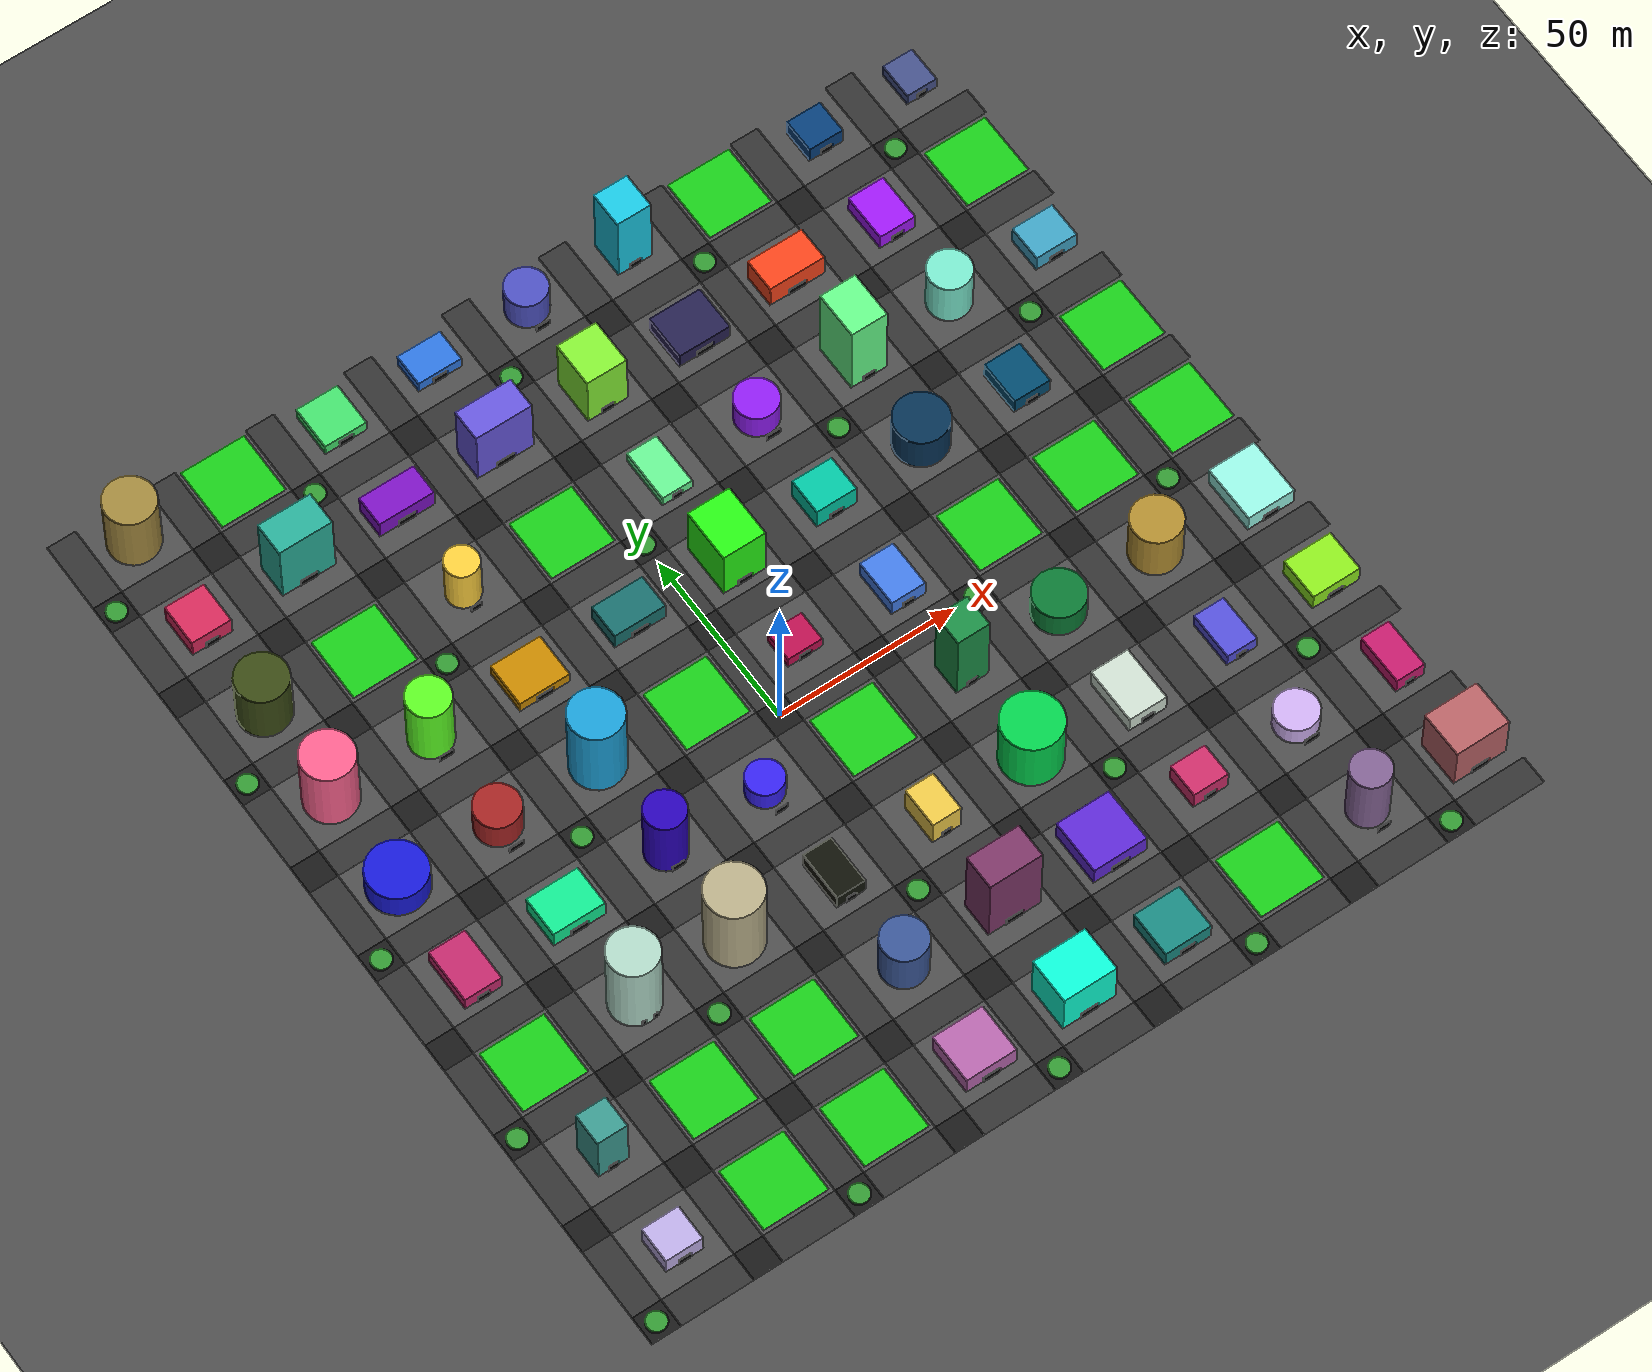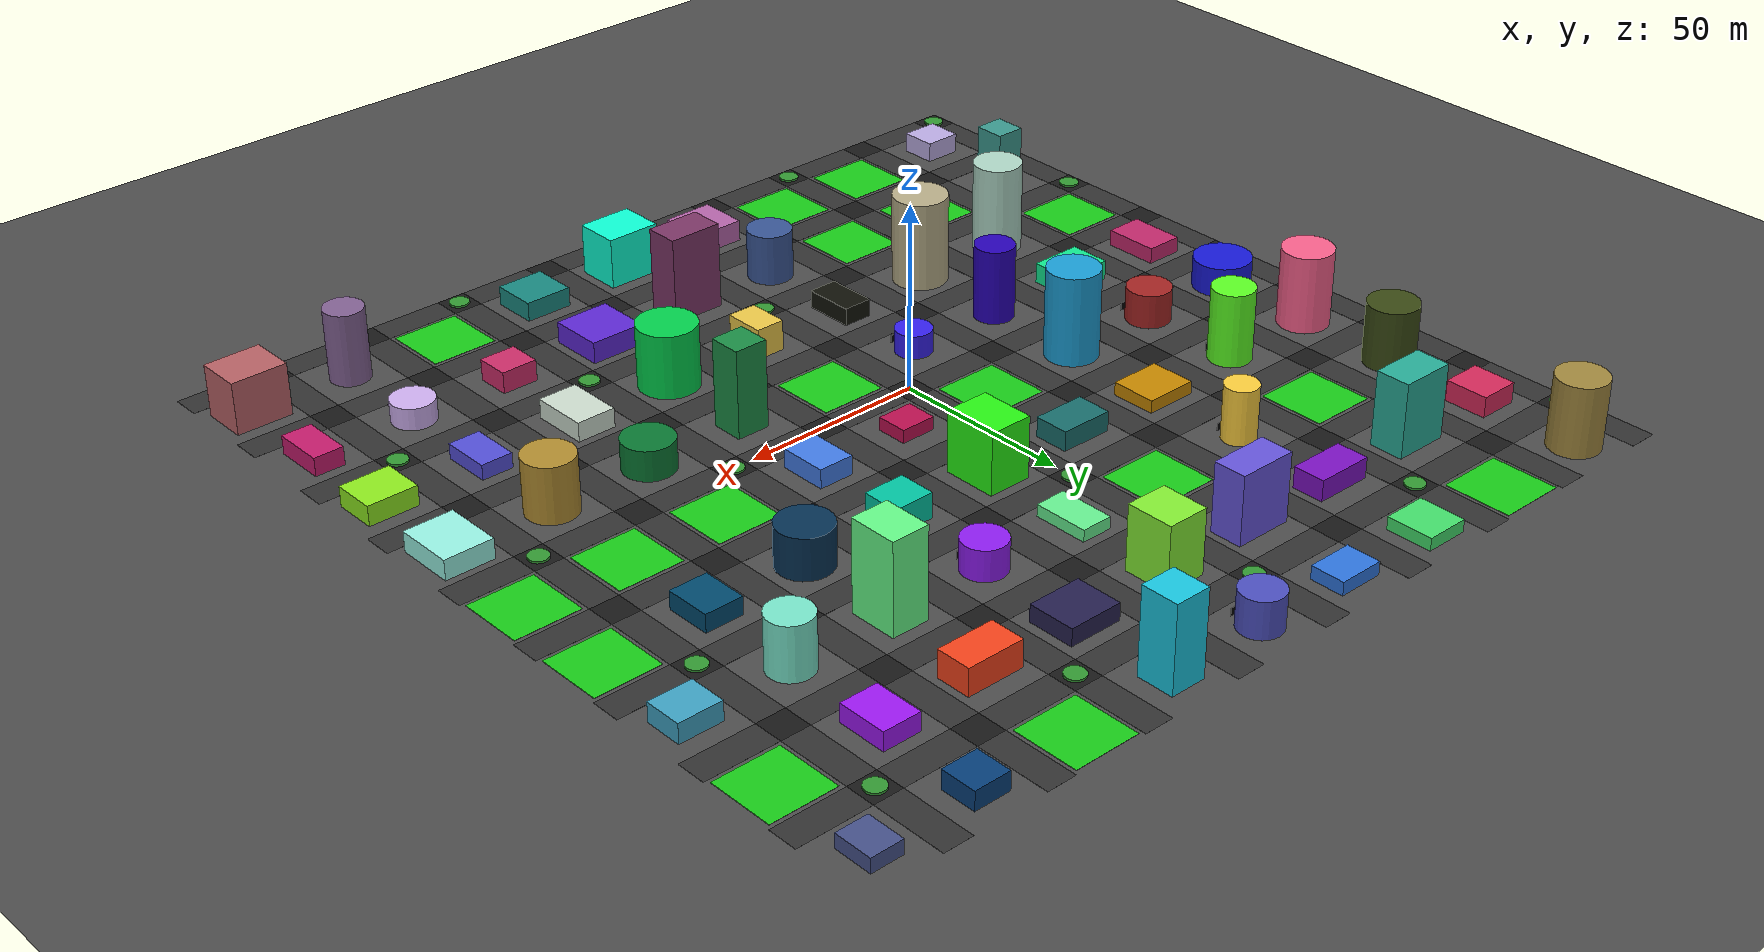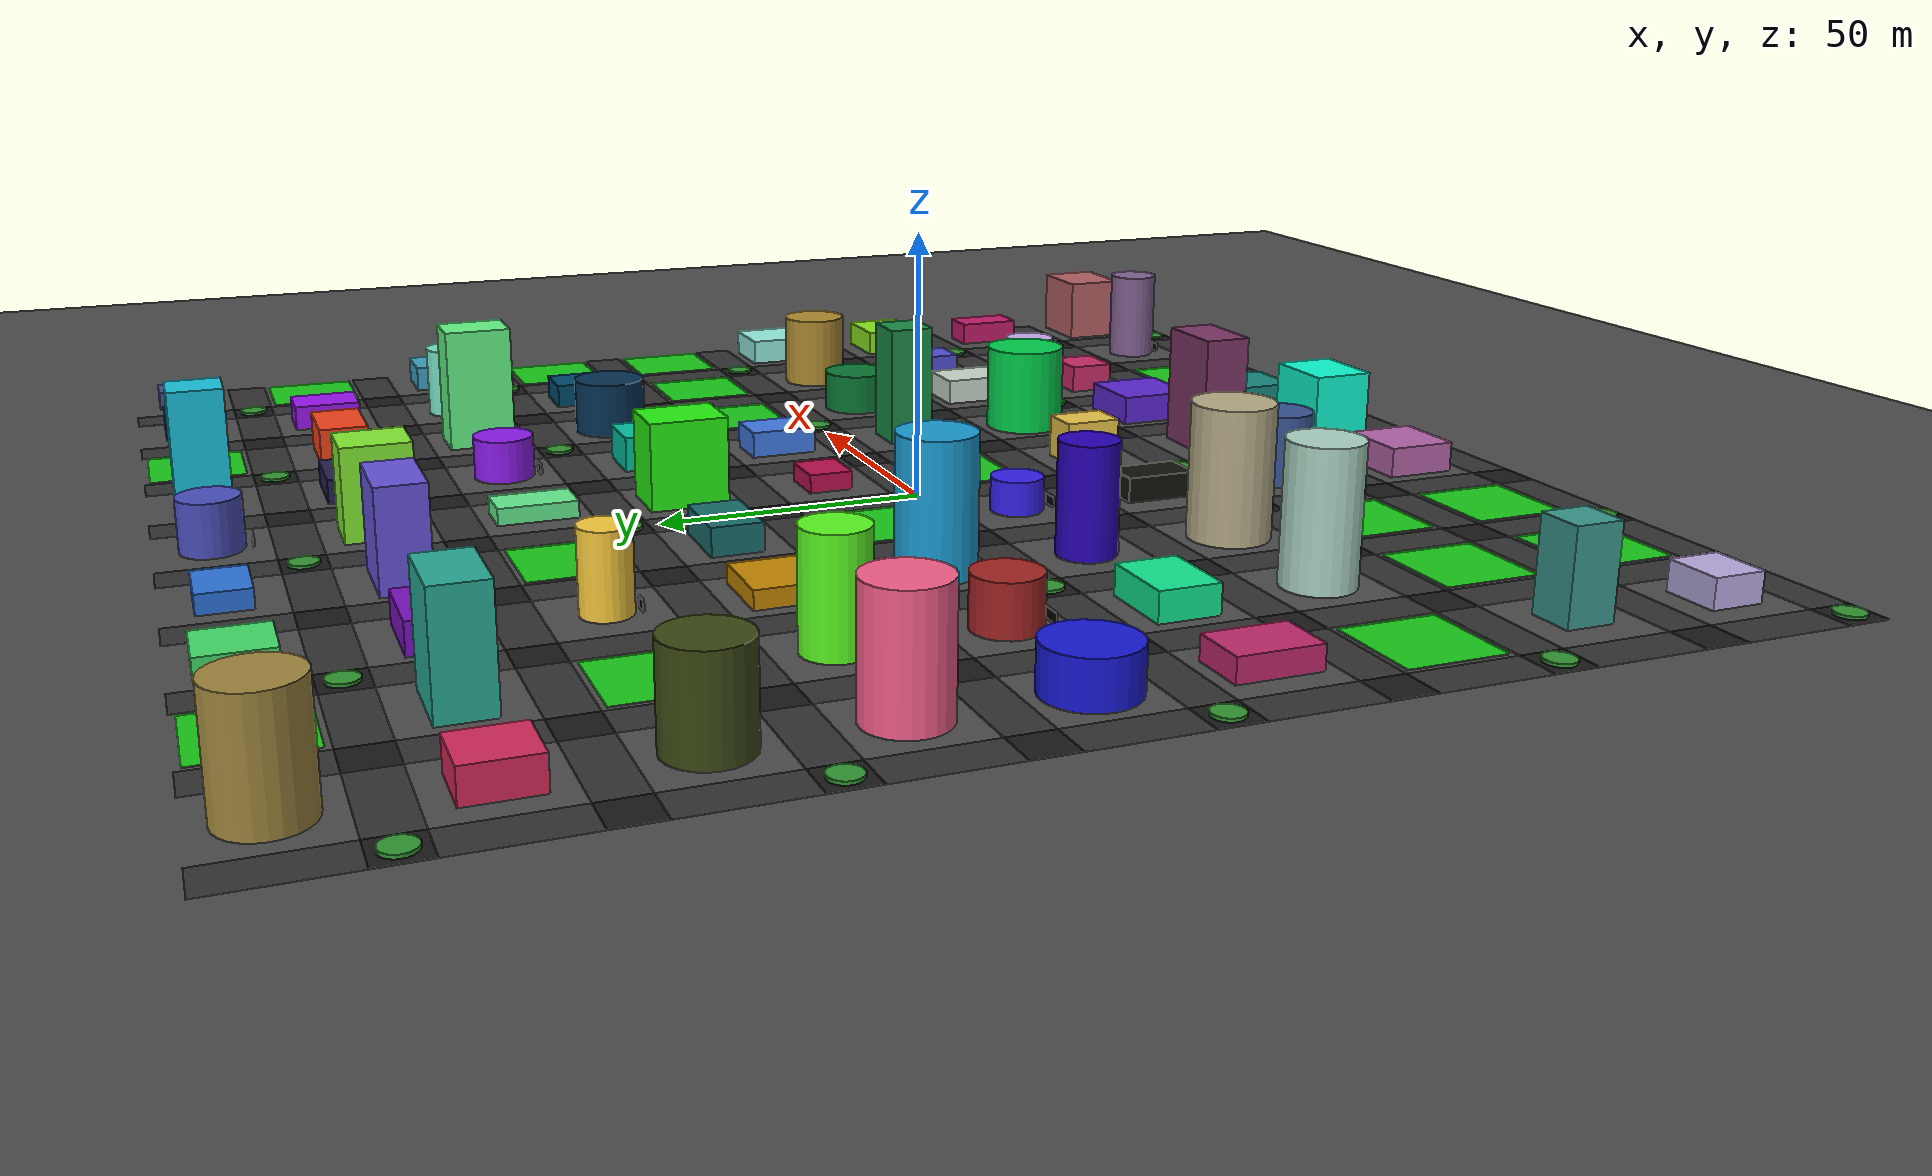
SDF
<?xml version="1.0" ?>
<sdf version="1.8">
  <world name="urban_city_rich">
    <physics name="1ms" type="ignored">
      <max_step_size>0.001</max_step_size>
      <real_time_factor>1.0</real_time_factor>
    </physics>
    <plugin filename="gz-sim-physics-system" name="gz::sim::systems::Physics"></plugin>
    <plugin filename="gz-sim-user-commands-system" name="gz::sim::systems::UserCommands"></plugin>
    <plugin filename="gz-sim-scene-broadcaster-system" name="gz::sim::systems::SceneBroadcaster"></plugin>
    <plugin filename="gz-sim-sensors-system" name="gz::sim::systems::Sensors">
        <render_engine>ogre2</render_engine>
    </plugin>
    <plugin filename="gz-sim-wind-effects-system" name="gz::sim::systems::WindEffects"></plugin>

    <light type="directional" name="sun">
      <cast_shadows>true</cast_shadows>
      <pose>0 0 10 0 0 0</pose>
      <diffuse>0.8 0.8 0.8 1</diffuse>
      <specular>0.2 0.2 0.2 1</specular>
      <direction>-0.5 0.1 -0.9</direction>
    </light>

    <model name="ground_plane">
      <static>true</static>
      <link name="link">
        <collision name="collision">
          <geometry><plane><normal>0 0 1</normal><size>200 200</size></plane></geometry>
          <surface>
            <friction>
              <ode>
                <mu>100</mu>
                <mu2>50</mu2>
              </ode>
            </friction>
          </surface>
        </collision>
        <visual name="visual">
          <geometry><plane><normal>0 0 1</normal><size>200 200</size></plane></geometry>
          <material><ambient>0.3 0.3 0.3 1</ambient><diffuse>0.3 0.3 0.3 1</diffuse></material>
        </visual>
      </link>
    </model>

    <model name="road_inter_-4_-4">
      <static>true</static>
      <pose>-112.0 -112.0 0.01 0 0 0</pose>
      <link name="link">
        <visual name="vis">
            <geometry><box><size>8.0 8.0 0.02</size></box></geometry>
            <material><ambient>0.1 0.1 0.1 1</ambient><diffuse>0.1 0.1 0.1 1</diffuse></material>
        </visual>
      </link>
    </model>

    <model name="roundabout_-4_-4">
      <static>true</static>
      <pose>-112.0 -112.0 0.3 0 0 0</pose>
      <link name="link">
        <collision name="col">
           <geometry><cylinder><radius>2.6666666666666665</radius><length>0.6</length></cylinder></geometry>
        </collision>
        <visual name="vis">
           <geometry><cylinder><radius>2.6666666666666665</radius><length>0.6</length></cylinder></geometry>
           <material><ambient>0.2 0.6 0.2 1</ambient><diffuse>0.2 0.6 0.2 1</diffuse></material>
        </visual>
      </link>
    </model>

    <model name="road_h_-4_-4">
      <static>true</static>
      <pose>-98.0 -112.0 0.01 0 0 0</pose>
      <link name="link">
        <visual name="vis">
            <geometry><box><size>20.0 8.0 0.02</size></box></geometry>
            <material><ambient>0.2 0.2 0.2 1</ambient><diffuse>0.2 0.2 0.2 1</diffuse></material>
        </visual>
      </link>
    </model>
    <model name="road_v_-4_-4">
      <static>true</static>
      <pose>-112.0 -98.0 0.01 0 0 0</pose>
      <link name="link">
        <visual name="vis">
            <geometry><box><size>8.0 20.0 0.02</size></box></geometry>
            <material><ambient>0.2 0.2 0.2 1</ambient><diffuse>0.2 0.2 0.2 1</diffuse></material>
        </visual>
      </link>
    </model>

    <model name="bldg_0">
      <static>true</static>
      <pose>-98.0 -98.0 2.7501075522266696 0 0 0</pose>
      <link name="link">
        <collision name="col">
           <geometry><box><size>10.200234546952954 9.785685905190583 5.500215104453339</size></box></geometry>
        </collision>
        <visual name="vis">
           <geometry><box><size>10.200234546952954 9.785685905190583 5.500215104453339</size></box></geometry>
           <material><ambient>0.7364712141640124 0.6766994874229113 0.8921795677048454 1</ambient><diffuse>0.7364712141640124 0.6766994874229113 0.8921795677048454 1</diffuse></material>
        </visual>
      </link>
    </model>

    <model name="door_0">
      <static>true</static>
      <pose>-98.0 -102.99284295259528 1.0 0 0 0</pose>
      <link name="link">
        <visual name="vis">
           <geometry><box><size>3.4000781823176514 0.2 2.0</size></box></geometry>
           <material><ambient>0 0 0 1</ambient><diffuse>0 0 0 1</diffuse></material>
        </visual>
      </link>
    </model>

    <model name="road_inter_-4_-3">
      <static>true</static>
      <pose>-112.0 -84.0 0.01 0 0 0</pose>
      <link name="link">
        <visual name="vis">
            <geometry><box><size>8.0 8.0 0.02</size></box></geometry>
            <material><ambient>0.1 0.1 0.1 1</ambient><diffuse>0.1 0.1 0.1 1</diffuse></material>
        </visual>
      </link>
    </model>

    <model name="road_h_-4_-3">
      <static>true</static>
      <pose>-98.0 -84.0 0.01 0 0 0</pose>
      <link name="link">
        <visual name="vis">
            <geometry><box><size>20.0 8.0 0.02</size></box></geometry>
            <material><ambient>0.2 0.2 0.2 1</ambient><diffuse>0.2 0.2 0.2 1</diffuse></material>
        </visual>
      </link>
    </model>
    <model name="road_v_-4_-3">
      <static>true</static>
      <pose>-112.0 -70.0 0.01 0 0 0</pose>
      <link name="link">
        <visual name="vis">
            <geometry><box><size>8.0 20.0 0.02</size></box></geometry>
            <material><ambient>0.2 0.2 0.2 1</ambient><diffuse>0.2 0.2 0.2 1</diffuse></material>
        </visual>
      </link>
    </model>

    <model name="bldg_1">
      <static>true</static>
      <pose>-98.0 -70.0 8.404925124490397 0 0 0</pose>
      <link name="link">
        <collision name="col">
           <geometry><box><size>8.254261435854268 8.74956191889274 16.809850248980794</size></box></geometry>
        </collision>
        <visual name="vis">
           <geometry><box><size>8.254261435854268 8.74956191889274 16.809850248980794</size></box></geometry>
           <material><ambient>0.2326608933907396 0.6020187290499803 0.561245062938613 1</ambient><diffuse>0.2326608933907396 0.6020187290499803 0.561245062938613 1</diffuse></material>
        </visual>
      </link>
    </model>

    <model name="door_1">
      <static>true</static>
      <pose>-98.0 -74.47478095944636 1.0 0 0 0</pose>
      <link name="link">
        <visual name="vis">
           <geometry><box><size>2.751420478618089 0.2 2.0</size></box></geometry>
           <material><ambient>0 0 0 1</ambient><diffuse>0 0 0 1</diffuse></material>
        </visual>
      </link>
    </model>

    <model name="road_inter_-4_-2">
      <static>true</static>
      <pose>-112.0 -56.0 0.01 0 0 0</pose>
      <link name="link">
        <visual name="vis">
            <geometry><box><size>8.0 8.0 0.02</size></box></geometry>
            <material><ambient>0.1 0.1 0.1 1</ambient><diffuse>0.1 0.1 0.1 1</diffuse></material>
        </visual>
      </link>
    </model>

    <model name="roundabout_-4_-2">
      <static>true</static>
      <pose>-112.0 -56.0 0.3 0 0 0</pose>
      <link name="link">
        <collision name="col">
           <geometry><cylinder><radius>2.6666666666666665</radius><length>0.6</length></cylinder></geometry>
        </collision>
        <visual name="vis">
           <geometry><cylinder><radius>2.6666666666666665</radius><length>0.6</length></cylinder></geometry>
           <material><ambient>0.2 0.6 0.2 1</ambient><diffuse>0.2 0.6 0.2 1</diffuse></material>
        </visual>
      </link>
    </model>

    <model name="road_h_-4_-2">
      <static>true</static>
      <pose>-98.0 -56.0 0.01 0 0 0</pose>
      <link name="link">
        <visual name="vis">
            <geometry><box><size>20.0 8.0 0.02</size></box></geometry>
            <material><ambient>0.2 0.2 0.2 1</ambient><diffuse>0.2 0.2 0.2 1</diffuse></material>
        </visual>
      </link>
    </model>
    <model name="road_v_-4_-2">
      <static>true</static>
      <pose>-112.0 -42.0 0.01 0 0 0</pose>
      <link name="link">
        <visual name="vis">
            <geometry><box><size>8.0 20.0 0.02</size></box></geometry>
            <material><ambient>0.2 0.2 0.2 1</ambient><diffuse>0.2 0.2 0.2 1</diffuse></material>
        </visual>
      </link>
    </model>

    <model name="park_-4_-2">
      <static>true</static>
      <pose>-98.0 -42.0 0.05 0 0 0</pose>
      <link name="link">
        <visual name="vis">
            <geometry><box><size>18.0 18.0 0.1</size></box></geometry>
            <material><ambient>0.1 0.8 0.1 1</ambient><diffuse>0.1 0.8 0.1 1</diffuse></material>
        </visual>
      </link>
    </model>

    <model name="road_inter_-4_-1">
      <static>true</static>
      <pose>-112.0 -28.0 0.01 0 0 0</pose>
      <link name="link">
        <visual name="vis">
            <geometry><box><size>8.0 8.0 0.02</size></box></geometry>
            <material><ambient>0.1 0.1 0.1 1</ambient><diffuse>0.1 0.1 0.1 1</diffuse></material>
        </visual>
      </link>
    </model>

    <model name="road_h_-4_-1">
      <static>true</static>
      <pose>-98.0 -28.0 0.01 0 0 0</pose>
      <link name="link">
        <visual name="vis">
            <geometry><box><size>20.0 8.0 0.02</size></box></geometry>
            <material><ambient>0.2 0.2 0.2 1</ambient><diffuse>0.2 0.2 0.2 1</diffuse></material>
        </visual>
      </link>
    </model>
    <model name="road_v_-4_-1">
      <static>true</static>
      <pose>-112.0 -14.0 0.01 0 0 0</pose>
      <link name="link">
        <visual name="vis">
            <geometry><box><size>8.0 20.0 0.02</size></box></geometry>
            <material><ambient>0.2 0.2 0.2 1</ambient><diffuse>0.2 0.2 0.2 1</diffuse></material>
        </visual>
      </link>
    </model>

    <model name="bldg_2">
      <static>true</static>
      <pose>-98.0 -14.0 2.1738135694257803 0 0 0</pose>
      <link name="link">
        <collision name="col">
           <geometry><box><size>10.225525665845302 14.954402566343472 4.347627138851561</size></box></geometry>
        </collision>
        <visual name="vis">
           <geometry><box><size>10.225525665845302 14.954402566343472 4.347627138851561</size></box></geometry>
           <material><ambient>0.7588073671297673 0.15965931637689013 0.42261439815350255 1</ambient><diffuse>0.7588073671297673 0.15965931637689013 0.42261439815350255 1</diffuse></material>
        </visual>
      </link>
    </model>

    <model name="door_2">
      <static>true</static>
      <pose>-98.0 -21.57720128317174 1.0 0 0 0</pose>
      <link name="link">
        <visual name="vis">
           <geometry><box><size>3.408508555281767 0.2 2.0</size></box></geometry>
           <material><ambient>0 0 0 1</ambient><diffuse>0 0 0 1</diffuse></material>
        </visual>
      </link>
    </model>

    <model name="road_inter_-4_0">
      <static>true</static>
      <pose>-112.0 0.0 0.01 0 0 0</pose>
      <link name="link">
        <visual name="vis">
            <geometry><box><size>8.0 8.0 0.02</size></box></geometry>
            <material><ambient>0.1 0.1 0.1 1</ambient><diffuse>0.1 0.1 0.1 1</diffuse></material>
        </visual>
      </link>
    </model>

    <model name="roundabout_-4_0">
      <static>true</static>
      <pose>-112.0 0.0 0.3 0 0 0</pose>
      <link name="link">
        <collision name="col">
           <geometry><cylinder><radius>2.6666666666666665</radius><length>0.6</length></cylinder></geometry>
        </collision>
        <visual name="vis">
           <geometry><cylinder><radius>2.6666666666666665</radius><length>0.6</length></cylinder></geometry>
           <material><ambient>0.2 0.6 0.2 1</ambient><diffuse>0.2 0.6 0.2 1</diffuse></material>
        </visual>
      </link>
    </model>

    <model name="road_h_-4_0">
      <static>true</static>
      <pose>-98.0 0.0 0.01 0 0 0</pose>
      <link name="link">
        <visual name="vis">
            <geometry><box><size>20.0 8.0 0.02</size></box></geometry>
            <material><ambient>0.2 0.2 0.2 1</ambient><diffuse>0.2 0.2 0.2 1</diffuse></material>
        </visual>
      </link>
    </model>
    <model name="road_v_-4_0">
      <static>true</static>
      <pose>-112.0 14.0 0.01 0 0 0</pose>
      <link name="link">
        <visual name="vis">
            <geometry><box><size>8.0 20.0 0.02</size></box></geometry>
            <material><ambient>0.2 0.2 0.2 1</ambient><diffuse>0.2 0.2 0.2 1</diffuse></material>
        </visual>
      </link>
    </model>

    <model name="bldg_3">
      <static>true</static>
      <pose>-98.0 14.0 4.054794998117815 0 0 0</pose>
      <link name="link">
        <collision name="col">
           <geometry><cylinder><radius>7.828852288827125</radius><length>8.10958999623563</length></cylinder></geometry>
        </collision>
        <visual name="vis">
           <geometry><cylinder><radius>7.828852288827125</radius><length>8.10958999623563</length></cylinder></geometry>
           <material><ambient>0.09274584338014791 0.09671637683346401 0.8474943663474598 1</ambient><diffuse>0.09274584338014791 0.09671637683346401 0.8474943663474598 1</diffuse></material>
        </visual>
      </link>
    </model>

    <model name="door_3">
      <static>true</static>
      <pose>-98.0 8.553621819549493 1.0 0 0 0</pose>
      <link name="link">
        <visual name="vis">
           <geometry><box><size>5.2192348592180835 0.2 2.0</size></box></geometry>
           <material><ambient>0 0 0 1</ambient><diffuse>0 0 0 1</diffuse></material>
        </visual>
      </link>
    </model>

    <model name="road_inter_-4_1">
      <static>true</static>
      <pose>-112.0 28.0 0.01 0 0 0</pose>
      <link name="link">
        <visual name="vis">
            <geometry><box><size>8.0 8.0 0.02</size></box></geometry>
            <material><ambient>0.1 0.1 0.1 1</ambient><diffuse>0.1 0.1 0.1 1</diffuse></material>
        </visual>
      </link>
    </model>

    <model name="road_h_-4_1">
      <static>true</static>
      <pose>-98.0 28.0 0.01 0 0 0</pose>
      <link name="link">
        <visual name="vis">
            <geometry><box><size>20.0 8.0 0.02</size></box></geometry>
            <material><ambient>0.2 0.2 0.2 1</ambient><diffuse>0.2 0.2 0.2 1</diffuse></material>
        </visual>
      </link>
    </model>
    <model name="road_v_-4_1">
      <static>true</static>
      <pose>-112.0 42.0 0.01 0 0 0</pose>
      <link name="link">
        <visual name="vis">
            <geometry><box><size>8.0 20.0 0.02</size></box></geometry>
            <material><ambient>0.2 0.2 0.2 1</ambient><diffuse>0.2 0.2 0.2 1</diffuse></material>
        </visual>
      </link>
    </model>

    <model name="bldg_4">
      <static>true</static>
      <pose>-98.0 42.0 10.571282732743802 0 0 0</pose>
      <link name="link">
        <collision name="col">
           <geometry><cylinder><radius>6.918927146775271</radius><length>21.142565465487603</length></cylinder></geometry>
        </collision>
        <visual name="vis">
           <geometry><cylinder><radius>6.918927146775271</radius><length>21.142565465487603</length></cylinder></geometry>
           <material><ambient>0.9731157639793706 0.3785343772083535 0.552040631273227 1</ambient><diffuse>0.9731157639793706 0.3785343772083535 0.552040631273227 1</diffuse></material>
        </visual>
      </link>
    </model>

    <model name="door_4">
      <static>true</static>
      <pose>-98.0 35.755087634181194 1.0 0 0 0</pose>
      <link name="link">
        <visual name="vis">
           <geometry><box><size>4.612618097850181 0.2 2.0</size></box></geometry>
           <material><ambient>0 0 0 1</ambient><diffuse>0 0 0 1</diffuse></material>
        </visual>
      </link>
    </model>

    <model name="road_inter_-4_2">
      <static>true</static>
      <pose>-112.0 56.0 0.01 0 0 0</pose>
      <link name="link">
        <visual name="vis">
            <geometry><box><size>8.0 8.0 0.02</size></box></geometry>
            <material><ambient>0.1 0.1 0.1 1</ambient><diffuse>0.1 0.1 0.1 1</diffuse></material>
        </visual>
      </link>
    </model>

    <model name="roundabout_-4_2">
      <static>true</static>
      <pose>-112.0 56.0 0.3 0 0 0</pose>
      <link name="link">
        <collision name="col">
           <geometry><cylinder><radius>2.6666666666666665</radius><length>0.6</length></cylinder></geometry>
        </collision>
        <visual name="vis">
           <geometry><cylinder><radius>2.6666666666666665</radius><length>0.6</length></cylinder></geometry>
           <material><ambient>0.2 0.6 0.2 1</ambient><diffuse>0.2 0.6 0.2 1</diffuse></material>
        </visual>
      </link>
    </model>

    <model name="road_h_-4_2">
      <static>true</static>
      <pose>-98.0 56.0 0.01 0 0 0</pose>
      <link name="link">
        <visual name="vis">
            <geometry><box><size>20.0 8.0 0.02</size></box></geometry>
            <material><ambient>0.2 0.2 0.2 1</ambient><diffuse>0.2 0.2 0.2 1</diffuse></material>
        </visual>
      </link>
    </model>
    <model name="road_v_-4_2">
      <static>true</static>
      <pose>-112.0 70.0 0.01 0 0 0</pose>
      <link name="link">
        <visual name="vis">
            <geometry><box><size>8.0 20.0 0.02</size></box></geometry>
            <material><ambient>0.2 0.2 0.2 1</ambient><diffuse>0.2 0.2 0.2 1</diffuse></material>
        </visual>
      </link>
    </model>

    <model name="bldg_5">
      <static>true</static>
      <pose>-98.0 70.0 8.273521452567621 0 0 0</pose>
      <link name="link">
        <collision name="col">
           <geometry><cylinder><radius>6.818287344859694</radius><length>16.547042905135243</length></cylinder></geometry>
        </collision>
        <visual name="vis">
           <geometry><cylinder><radius>6.818287344859694</radius><length>16.547042905135243</length></cylinder></geometry>
           <material><ambient>0.22789827565154686 0.28938796360210717 0.0797919769236275 1</ambient><diffuse>0.22789827565154686 0.28938796360210717 0.0797919769236275 1</diffuse></material>
        </visual>
      </link>
    </model>

    <model name="door_5">
      <static>true</static>
      <pose>-98.0 65.71670246537735 1.0 0 0 0</pose>
      <link name="link">
        <visual name="vis">
           <geometry><box><size>4.54552489657313 0.2 2.0</size></box></geometry>
           <material><ambient>0 0 0 1</ambient><diffuse>0 0 0 1</diffuse></material>
        </visual>
      </link>
    </model>

    <model name="road_inter_-4_3">
      <static>true</static>
      <pose>-112.0 84.0 0.01 0 0 0</pose>
      <link name="link">
        <visual name="vis">
            <geometry><box><size>8.0 8.0 0.02</size></box></geometry>
            <material><ambient>0.1 0.1 0.1 1</ambient><diffuse>0.1 0.1 0.1 1</diffuse></material>
        </visual>
      </link>
    </model>

    <model name="road_h_-4_3">
      <static>true</static>
      <pose>-98.0 84.0 0.01 0 0 0</pose>
      <link name="link">
        <visual name="vis">
            <geometry><box><size>20.0 8.0 0.02</size></box></geometry>
            <material><ambient>0.2 0.2 0.2 1</ambient><diffuse>0.2 0.2 0.2 1</diffuse></material>
        </visual>
      </link>
    </model>
    <model name="road_v_-4_3">
      <static>true</static>
      <pose>-112.0 98.0 0.01 0 0 0</pose>
      <link name="link">
        <visual name="vis">
            <geometry><box><size>8.0 20.0 0.02</size></box></geometry>
            <material><ambient>0.2 0.2 0.2 1</ambient><diffuse>0.2 0.2 0.2 1</diffuse></material>
        </visual>
      </link>
    </model>

    <model name="bldg_6">
      <static>true</static>
      <pose>-98.0 98.0 2.7997255001329044 0 0 0</pose>
      <link name="link">
        <collision name="col">
           <geometry><box><size>11.04100980031333 11.627282418947484 5.599451000265809</size></box></geometry>
        </collision>
        <visual name="vis">
           <geometry><box><size>11.04100980031333 11.627282418947484 5.599451000265809</size></box></geometry>
           <material><ambient>0.8341104266407503 0.1626540971560848 0.3552707002275215 1</ambient><diffuse>0.8341104266407503 0.1626540971560848 0.3552707002275215 1</diffuse></material>
        </visual>
      </link>
    </model>

    <model name="door_6">
      <static>true</static>
      <pose>-98.0 92.08635879052626 1.0 0 0 0</pose>
      <link name="link">
        <visual name="vis">
           <geometry><box><size>3.680336600104443 0.2 2.0</size></box></geometry>
           <material><ambient>0 0 0 1</ambient><diffuse>0 0 0 1</diffuse></material>
        </visual>
      </link>
    </model>

    <model name="road_inter_-4_4">
      <static>true</static>
      <pose>-112.0 112.0 0.01 0 0 0</pose>
      <link name="link">
        <visual name="vis">
            <geometry><box><size>8.0 8.0 0.02</size></box></geometry>
            <material><ambient>0.1 0.1 0.1 1</ambient><diffuse>0.1 0.1 0.1 1</diffuse></material>
        </visual>
      </link>
    </model>

    <model name="roundabout_-4_4">
      <static>true</static>
      <pose>-112.0 112.0 0.3 0 0 0</pose>
      <link name="link">
        <collision name="col">
           <geometry><cylinder><radius>2.6666666666666665</radius><length>0.6</length></cylinder></geometry>
        </collision>
        <visual name="vis">
           <geometry><cylinder><radius>2.6666666666666665</radius><length>0.6</length></cylinder></geometry>
           <material><ambient>0.2 0.6 0.2 1</ambient><diffuse>0.2 0.6 0.2 1</diffuse></material>
        </visual>
      </link>
    </model>

    <model name="road_h_-4_4">
      <static>true</static>
      <pose>-98.0 112.0 0.01 0 0 0</pose>
      <link name="link">
        <visual name="vis">
            <geometry><box><size>20.0 8.0 0.02</size></box></geometry>
            <material><ambient>0.2 0.2 0.2 1</ambient><diffuse>0.2 0.2 0.2 1</diffuse></material>
        </visual>
      </link>
    </model>
    <model name="road_v_-4_4">
      <static>true</static>
      <pose>-112.0 126.0 0.01 0 0 0</pose>
      <link name="link">
        <visual name="vis">
            <geometry><box><size>8.0 20.0 0.02</size></box></geometry>
            <material><ambient>0.2 0.2 0.2 1</ambient><diffuse>0.2 0.2 0.2 1</diffuse></material>
        </visual>
      </link>
    </model>

    <model name="bldg_7">
      <static>true</static>
      <pose>-98.0 126.0 9.518203134585512 0 0 0</pose>
      <link name="link">
        <collision name="col">
           <geometry><cylinder><radius>6.734190662146669</radius><length>19.036406269171025</length></cylinder></geometry>
        </collision>
        <visual name="vis">
           <geometry><cylinder><radius>6.734190662146669</radius><length>19.036406269171025</length></cylinder></geometry>
           <material><ambient>0.6349782881970603 0.534139877029708 0.24481092515142622 1</ambient><diffuse>0.6349782881970603 0.534139877029708 0.24481092515142622 1</diffuse></material>
        </visual>
      </link>
    </model>

    <model name="door_7">
      <static>true</static>
      <pose>-98.0 121.61438996168582 1.0 0 0 0</pose>
      <link name="link">
        <visual name="vis">
           <geometry><box><size>4.489460441431112 0.2 2.0</size></box></geometry>
           <material><ambient>0 0 0 1</ambient><diffuse>0 0 0 1</diffuse></material>
        </visual>
      </link>
    </model>

    <model name="road_inter_-3_-4">
      <static>true</static>
      <pose>-84.0 -112.0 0.01 0 0 0</pose>
      <link name="link">
        <visual name="vis">
            <geometry><box><size>8.0 8.0 0.02</size></box></geometry>
            <material><ambient>0.1 0.1 0.1 1</ambient><diffuse>0.1 0.1 0.1 1</diffuse></material>
        </visual>
      </link>
    </model>

    <model name="road_h_-3_-4">
      <static>true</static>
      <pose>-70.0 -112.0 0.01 0 0 0</pose>
      <link name="link">
        <visual name="vis">
            <geometry><box><size>20.0 8.0 0.02</size></box></geometry>
            <material><ambient>0.2 0.2 0.2 1</ambient><diffuse>0.2 0.2 0.2 1</diffuse></material>
        </visual>
      </link>
    </model>
    <model name="road_v_-3_-4">
      <static>true</static>
      <pose>-84.0 -98.0 0.01 0 0 0</pose>
      <link name="link">
        <visual name="vis">
            <geometry><box><size>8.0 20.0 0.02</size></box></geometry>
            <material><ambient>0.2 0.2 0.2 1</ambient><diffuse>0.2 0.2 0.2 1</diffuse></material>
        </visual>
      </link>
    </model>

    <model name="park_-3_-4">
      <static>true</static>
      <pose>-70.0 -98.0 0.05 0 0 0</pose>
      <link name="link">
        <visual name="vis">
            <geometry><box><size>18.0 18.0 0.1</size></box></geometry>
            <material><ambient>0.1 0.8 0.1 1</ambient><diffuse>0.1 0.8 0.1 1</diffuse></material>
        </visual>
      </link>
    </model>

    <model name="road_inter_-3_-3">
      <static>true</static>
      <pose>-84.0 -84.0 0.01 0 0 0</pose>
      <link name="link">
        <visual name="vis">
            <geometry><box><size>8.0 8.0 0.02</size></box></geometry>
            <material><ambient>0.1 0.1 0.1 1</ambient><diffuse>0.1 0.1 0.1 1</diffuse></material>
        </visual>
      </link>
    </model>

    <model name="road_h_-3_-3">
      <static>true</static>
      <pose>-70.0 -84.0 0.01 0 0 0</pose>
      <link name="link">
        <visual name="vis">
            <geometry><box><size>20.0 8.0 0.02</size></box></geometry>
            <material><ambient>0.2 0.2 0.2 1</ambient><diffuse>0.2 0.2 0.2 1</diffuse></material>
        </visual>
      </link>
    </model>
    <model name="road_v_-3_-3">
      <static>true</static>
      <pose>-84.0 -70.0 0.01 0 0 0</pose>
      <link name="link">
        <visual name="vis">
            <geometry><box><size>8.0 20.0 0.02</size></box></geometry>
            <material><ambient>0.2 0.2 0.2 1</ambient><diffuse>0.2 0.2 0.2 1</diffuse></material>
        </visual>
      </link>
    </model>

    <model name="park_-3_-3">
      <static>true</static>
      <pose>-70.0 -70.0 0.05 0 0 0</pose>
      <link name="link">
        <visual name="vis">
            <geometry><box><size>18.0 18.0 0.1</size></box></geometry>
            <material><ambient>0.1 0.8 0.1 1</ambient><diffuse>0.1 0.8 0.1 1</diffuse></material>
        </visual>
      </link>
    </model>

    <model name="road_inter_-3_-2">
      <static>true</static>
      <pose>-84.0 -56.0 0.01 0 0 0</pose>
      <link name="link">
        <visual name="vis">
            <geometry><box><size>8.0 8.0 0.02</size></box></geometry>
            <material><ambient>0.1 0.1 0.1 1</ambient><diffuse>0.1 0.1 0.1 1</diffuse></material>
        </visual>
      </link>
    </model>

    <model name="road_h_-3_-2">
      <static>true</static>
      <pose>-70.0 -56.0 0.01 0 0 0</pose>
      <link name="link">
        <visual name="vis">
            <geometry><box><size>20.0 8.0 0.02</size></box></geometry>
            <material><ambient>0.2 0.2 0.2 1</ambient><diffuse>0.2 0.2 0.2 1</diffuse></material>
        </visual>
      </link>
    </model>
    <model name="road_v_-3_-2">
      <static>true</static>
      <pose>-84.0 -42.0 0.01 0 0 0</pose>
      <link name="link">
        <visual name="vis">
            <geometry><box><size>8.0 20.0 0.02</size></box></geometry>
            <material><ambient>0.2 0.2 0.2 1</ambient><diffuse>0.2 0.2 0.2 1</diffuse></material>
        </visual>
      </link>
    </model>

    <model name="bldg_8">
      <static>true</static>
      <pose>-70.0 -42.0 12.395233506365953 0 0 0</pose>
      <link name="link">
        <collision name="col">
           <geometry><cylinder><radius>6.559999039416372</radius><length>24.790467012731906</length></cylinder></geometry>
        </collision>
        <visual name="vis">
           <geometry><cylinder><radius>6.559999039416372</radius><length>24.790467012731906</length></cylinder></geometry>
           <material><ambient>0.6846142509898746 0.8428519201898096 0.7759999115462448 1</ambient><diffuse>0.6846142509898746 0.8428519201898096 0.7759999115462448 1</diffuse></material>
        </visual>
      </link>
    </model>

    <model name="door_8">
      <static>true</static>
      <pose>-70.0 -48.32779897509859 1.0 0 0 0</pose>
      <link name="link">
        <visual name="vis">
           <geometry><box><size>4.373332692944248 0.2 2.0</size></box></geometry>
           <material><ambient>0 0 0 1</ambient><diffuse>0 0 0 1</diffuse></material>
        </visual>
      </link>
    </model>

    <model name="road_inter_-3_-1">
      <static>true</static>
      <pose>-84.0 -28.0 0.01 0 0 0</pose>
      <link name="link">
        <visual name="vis">
            <geometry><box><size>8.0 8.0 0.02</size></box></geometry>
            <material><ambient>0.1 0.1 0.1 1</ambient><diffuse>0.1 0.1 0.1 1</diffuse></material>
        </visual>
      </link>
    </model>

    <model name="road_h_-3_-1">
      <static>true</static>
      <pose>-70.0 -28.0 0.01 0 0 0</pose>
      <link name="link">
        <visual name="vis">
            <geometry><box><size>20.0 8.0 0.02</size></box></geometry>
            <material><ambient>0.2 0.2 0.2 1</ambient><diffuse>0.2 0.2 0.2 1</diffuse></material>
        </visual>
      </link>
    </model>
    <model name="road_v_-3_-1">
      <static>true</static>
      <pose>-84.0 -14.0 0.01 0 0 0</pose>
      <link name="link">
        <visual name="vis">
            <geometry><box><size>8.0 20.0 0.02</size></box></geometry>
            <material><ambient>0.2 0.2 0.2 1</ambient><diffuse>0.2 0.2 0.2 1</diffuse></material>
        </visual>
      </link>
    </model>

    <model name="bldg_9">
      <static>true</static>
      <pose>-70.0 -14.0 2.7327038910102126 0 0 0</pose>
      <link name="link">
        <collision name="col">
           <geometry><box><size>14.440366406169716 11.209318296178632 5.465407782020425</size></box></geometry>
        </collision>
        <visual name="vis">
           <geometry><box><size>14.440366406169716 11.209318296178632 5.465407782020425</size></box></geometry>
           <material><ambient>0.06618860521154724 0.913136124185545 0.5671800514785023 1</ambient><diffuse>0.06618860521154724 0.913136124185545 0.5671800514785023 1</diffuse></material>
        </visual>
      </link>
    </model>

    <model name="door_9">
      <static>true</static>
      <pose>-70.0 -19.704659148089316 1.0 0 0 0</pose>
      <link name="link">
        <visual name="vis">
           <geometry><box><size>4.813455468723238 0.2 2.0</size></box></geometry>
           <material><ambient>0 0 0 1</ambient><diffuse>0 0 0 1</diffuse></material>
        </visual>
      </link>
    </model>

    <model name="road_inter_-3_0">
      <static>true</static>
      <pose>-84.0 0.0 0.01 0 0 0</pose>
      <link name="link">
        <visual name="vis">
            <geometry><box><size>8.0 8.0 0.02</size></box></geometry>
            <material><ambient>0.1 0.1 0.1 1</ambient><diffuse>0.1 0.1 0.1 1</diffuse></material>
        </visual>
      </link>
    </model>

    <model name="road_h_-3_0">
      <static>true</static>
      <pose>-70.0 0.0 0.01 0 0 0</pose>
      <link name="link">
        <visual name="vis">
            <geometry><box><size>20.0 8.0 0.02</size></box></geometry>
            <material><ambient>0.2 0.2 0.2 1</ambient><diffuse>0.2 0.2 0.2 1</diffuse></material>
        </visual>
      </link>
    </model>
    <model name="road_v_-3_0">
      <static>true</static>
      <pose>-84.0 14.0 0.01 0 0 0</pose>
      <link name="link">
        <visual name="vis">
            <geometry><box><size>8.0 20.0 0.02</size></box></geometry>
            <material><ambient>0.2 0.2 0.2 1</ambient><diffuse>0.2 0.2 0.2 1</diffuse></material>
        </visual>
      </link>
    </model>

    <model name="bldg_10">
      <static>true</static>
      <pose>-70.0 14.0 4.626265440541406 0 0 0</pose>
      <link name="link">
        <collision name="col">
           <geometry><cylinder><radius>5.99692503796911</radius><length>9.252530881082812</length></cylinder></geometry>
        </collision>
        <visual name="vis">
           <geometry><cylinder><radius>5.99692503796911</radius><length>9.252530881082812</length></cylinder></geometry>
           <material><ambient>0.6428518702004242 0.14287159044206266 0.1396303195255063 1</ambient><diffuse>0.6428518702004242 0.14287159044206266 0.1396303195255063 1</diffuse></material>
        </visual>
      </link>
    </model>

    <model name="door_10">
      <static>true</static>
      <pose>-70.0 6.361267384453191 1.0 0 0 0</pose>
      <link name="link">
        <visual name="vis">
           <geometry><box><size>3.99795002531274 0.2 2.0</size></box></geometry>
           <material><ambient>0 0 0 1</ambient><diffuse>0 0 0 1</diffuse></material>
        </visual>
      </link>
    </model>

    <model name="road_inter_-3_1">
      <static>true</static>
      <pose>-84.0 28.0 0.01 0 0 0</pose>
      <link name="link">
        <visual name="vis">
            <geometry><box><size>8.0 8.0 0.02</size></box></geometry>
            <material><ambient>0.1 0.1 0.1 1</ambient><diffuse>0.1 0.1 0.1 1</diffuse></material>
        </visual>
      </link>
    </model>

    <model name="road_h_-3_1">
      <static>true</static>
      <pose>-70.0 28.0 0.01 0 0 0</pose>
      <link name="link">
        <visual name="vis">
            <geometry><box><size>20.0 8.0 0.02</size></box></geometry>
            <material><ambient>0.2 0.2 0.2 1</ambient><diffuse>0.2 0.2 0.2 1</diffuse></material>
        </visual>
      </link>
    </model>
    <model name="road_v_-3_1">
      <static>true</static>
      <pose>-84.0 42.0 0.01 0 0 0</pose>
      <link name="link">
        <visual name="vis">
            <geometry><box><size>8.0 20.0 0.02</size></box></geometry>
            <material><ambient>0.2 0.2 0.2 1</ambient><diffuse>0.2 0.2 0.2 1</diffuse></material>
        </visual>
      </link>
    </model>

    <model name="bldg_11">
      <static>true</static>
      <pose>-70.0 42.0 9.970138116522579 0 0 0</pose>
      <link name="link">
        <collision name="col">
           <geometry><cylinder><radius>5.713735309178318</radius><length>19.940276233045157</length></cylinder></geometry>
        </collision>
        <visual name="vis">
           <geometry><cylinder><radius>5.713735309178318</radius><length>19.940276233045157</length></cylinder></geometry>
           <material><ambient>0.36199644371361095 0.997325777989161 0.13833174489085587 1</ambient><diffuse>0.36199644371361095 0.997325777989161 0.13833174489085587 1</diffuse></material>
        </visual>
      </link>
    </model>

    <model name="door_11">
      <static>true</static>
      <pose>-70.0 35.565868300217375 1.0 0 0 0</pose>
      <link name="link">
        <visual name="vis">
           <geometry><box><size>3.8091568727855454 0.2 2.0</size></box></geometry>
           <material><ambient>0 0 0 1</ambient><diffuse>0 0 0 1</diffuse></material>
        </visual>
      </link>
    </model>

    <model name="road_inter_-3_2">
      <static>true</static>
      <pose>-84.0 56.0 0.01 0 0 0</pose>
      <link name="link">
        <visual name="vis">
            <geometry><box><size>8.0 8.0 0.02</size></box></geometry>
            <material><ambient>0.1 0.1 0.1 1</ambient><diffuse>0.1 0.1 0.1 1</diffuse></material>
        </visual>
      </link>
    </model>

    <model name="road_h_-3_2">
      <static>true</static>
      <pose>-70.0 56.0 0.01 0 0 0</pose>
      <link name="link">
        <visual name="vis">
            <geometry><box><size>20.0 8.0 0.02</size></box></geometry>
            <material><ambient>0.2 0.2 0.2 1</ambient><diffuse>0.2 0.2 0.2 1</diffuse></material>
        </visual>
      </link>
    </model>
    <model name="road_v_-3_2">
      <static>true</static>
      <pose>-84.0 70.0 0.01 0 0 0</pose>
      <link name="link">
        <visual name="vis">
            <geometry><box><size>8.0 20.0 0.02</size></box></geometry>
            <material><ambient>0.2 0.2 0.2 1</ambient><diffuse>0.2 0.2 0.2 1</diffuse></material>
        </visual>
      </link>
    </model>

    <model name="park_-3_2">
      <static>true</static>
      <pose>-70.0 70.0 0.05 0 0 0</pose>
      <link name="link">
        <visual name="vis">
            <geometry><box><size>18.0 18.0 0.1</size></box></geometry>
            <material><ambient>0.1 0.8 0.1 1</ambient><diffuse>0.1 0.8 0.1 1</diffuse></material>
        </visual>
      </link>
    </model>

    <model name="road_inter_-3_3">
      <static>true</static>
      <pose>-84.0 84.0 0.01 0 0 0</pose>
      <link name="link">
        <visual name="vis">
            <geometry><box><size>8.0 8.0 0.02</size></box></geometry>
            <material><ambient>0.1 0.1 0.1 1</ambient><diffuse>0.1 0.1 0.1 1</diffuse></material>
        </visual>
      </link>
    </model>

    <model name="road_h_-3_3">
      <static>true</static>
      <pose>-70.0 84.0 0.01 0 0 0</pose>
      <link name="link">
        <visual name="vis">
            <geometry><box><size>20.0 8.0 0.02</size></box></geometry>
            <material><ambient>0.2 0.2 0.2 1</ambient><diffuse>0.2 0.2 0.2 1</diffuse></material>
        </visual>
      </link>
    </model>
    <model name="road_v_-3_3">
      <static>true</static>
      <pose>-84.0 98.0 0.01 0 0 0</pose>
      <link name="link">
        <visual name="vis">
            <geometry><box><size>8.0 20.0 0.02</size></box></geometry>
            <material><ambient>0.2 0.2 0.2 1</ambient><diffuse>0.2 0.2 0.2 1</diffuse></material>
        </visual>
      </link>
    </model>

    <model name="bldg_12">
      <static>true</static>
      <pose>-70.0 98.0 10.057821575337378 0 0 0</pose>
      <link name="link">
        <collision name="col">
           <geometry><box><size>14.888823277333326 9.22273055478609 20.115643150674757</size></box></geometry>
        </collision>
        <visual name="vis">
           <geometry><box><size>14.888823277333326 9.22273055478609 20.115643150674757</size></box></geometry>
           <material><ambient>0.15998200172245025 0.6804812134963271 0.5964090307319738 1</ambient><diffuse>0.15998200172245025 0.6804812134963271 0.5964090307319738 1</diffuse></material>
        </visual>
      </link>
    </model>

    <model name="door_12">
      <static>true</static>
      <pose>-70.0 93.28863472260696 1.0 0 0 0</pose>
      <link name="link">
        <visual name="vis">
           <geometry><box><size>4.962941092444442 0.2 2.0</size></box></geometry>
           <material><ambient>0 0 0 1</ambient><diffuse>0 0 0 1</diffuse></material>
        </visual>
      </link>
    </model>

    <model name="road_inter_-3_4">
      <static>true</static>
      <pose>-84.0 112.0 0.01 0 0 0</pose>
      <link name="link">
        <visual name="vis">
            <geometry><box><size>8.0 8.0 0.02</size></box></geometry>
            <material><ambient>0.1 0.1 0.1 1</ambient><diffuse>0.1 0.1 0.1 1</diffuse></material>
        </visual>
      </link>
    </model>

    <model name="road_h_-3_4">
      <static>true</static>
      <pose>-70.0 112.0 0.01 0 0 0</pose>
      <link name="link">
        <visual name="vis">
            <geometry><box><size>20.0 8.0 0.02</size></box></geometry>
            <material><ambient>0.2 0.2 0.2 1</ambient><diffuse>0.2 0.2 0.2 1</diffuse></material>
        </visual>
      </link>
    </model>
    <model name="road_v_-3_4">
      <static>true</static>
      <pose>-84.0 126.0 0.01 0 0 0</pose>
      <link name="link">
        <visual name="vis">
            <geometry><box><size>8.0 20.0 0.02</size></box></geometry>
            <material><ambient>0.2 0.2 0.2 1</ambient><diffuse>0.2 0.2 0.2 1</diffuse></material>
        </visual>
      </link>
    </model>

    <model name="park_-3_4">
      <static>true</static>
      <pose>-70.0 126.0 0.05 0 0 0</pose>
      <link name="link">
        <visual name="vis">
            <geometry><box><size>18.0 18.0 0.1</size></box></geometry>
            <material><ambient>0.1 0.8 0.1 1</ambient><diffuse>0.1 0.8 0.1 1</diffuse></material>
        </visual>
      </link>
    </model>

    <model name="road_inter_-2_-4">
      <static>true</static>
      <pose>-56.0 -112.0 0.01 0 0 0</pose>
      <link name="link">
        <visual name="vis">
            <geometry><box><size>8.0 8.0 0.02</size></box></geometry>
            <material><ambient>0.1 0.1 0.1 1</ambient><diffuse>0.1 0.1 0.1 1</diffuse></material>
        </visual>
      </link>
    </model>

    <model name="roundabout_-2_-4">
      <static>true</static>
      <pose>-56.0 -112.0 0.3 0 0 0</pose>
      <link name="link">
        <collision name="col">
           <geometry><cylinder><radius>2.6666666666666665</radius><length>0.6</length></cylinder></geometry>
        </collision>
        <visual name="vis">
           <geometry><cylinder><radius>2.6666666666666665</radius><length>0.6</length></cylinder></geometry>
           <material><ambient>0.2 0.6 0.2 1</ambient><diffuse>0.2 0.6 0.2 1</diffuse></material>
        </visual>
      </link>
    </model>

    <model name="road_h_-2_-4">
      <static>true</static>
      <pose>-42.0 -112.0 0.01 0 0 0</pose>
      <link name="link">
        <visual name="vis">
            <geometry><box><size>20.0 8.0 0.02</size></box></geometry>
            <material><ambient>0.2 0.2 0.2 1</ambient><diffuse>0.2 0.2 0.2 1</diffuse></material>
        </visual>
      </link>
    </model>
    <model name="road_v_-2_-4">
      <static>true</static>
      <pose>-56.0 -98.0 0.01 0 0 0</pose>
      <link name="link">
        <visual name="vis">
            <geometry><box><size>8.0 20.0 0.02</size></box></geometry>
            <material><ambient>0.2 0.2 0.2 1</ambient><diffuse>0.2 0.2 0.2 1</diffuse></material>
        </visual>
      </link>
    </model>

    <model name="park_-2_-4">
      <static>true</static>
      <pose>-42.0 -98.0 0.05 0 0 0</pose>
      <link name="link">
        <visual name="vis">
            <geometry><box><size>18.0 18.0 0.1</size></box></geometry>
            <material><ambient>0.1 0.8 0.1 1</ambient><diffuse>0.1 0.8 0.1 1</diffuse></material>
        </visual>
      </link>
    </model>

    <model name="road_inter_-2_-3">
      <static>true</static>
      <pose>-56.0 -84.0 0.01 0 0 0</pose>
      <link name="link">
        <visual name="vis">
            <geometry><box><size>8.0 8.0 0.02</size></box></geometry>
            <material><ambient>0.1 0.1 0.1 1</ambient><diffuse>0.1 0.1 0.1 1</diffuse></material>
        </visual>
      </link>
    </model>

    <model name="road_h_-2_-3">
      <static>true</static>
      <pose>-42.0 -84.0 0.01 0 0 0</pose>
      <link name="link">
        <visual name="vis">
            <geometry><box><size>20.0 8.0 0.02</size></box></geometry>
            <material><ambient>0.2 0.2 0.2 1</ambient><diffuse>0.2 0.2 0.2 1</diffuse></material>
        </visual>
      </link>
    </model>
    <model name="road_v_-2_-3">
      <static>true</static>
      <pose>-56.0 -70.0 0.01 0 0 0</pose>
      <link name="link">
        <visual name="vis">
            <geometry><box><size>8.0 20.0 0.02</size></box></geometry>
            <material><ambient>0.2 0.2 0.2 1</ambient><diffuse>0.2 0.2 0.2 1</diffuse></material>
        </visual>
      </link>
    </model>

    <model name="park_-2_-3">
      <static>true</static>
      <pose>-42.0 -70.0 0.05 0 0 0</pose>
      <link name="link">
        <visual name="vis">
            <geometry><box><size>18.0 18.0 0.1</size></box></geometry>
            <material><ambient>0.1 0.8 0.1 1</ambient><diffuse>0.1 0.8 0.1 1</diffuse></material>
        </visual>
      </link>
    </model>

    <model name="road_inter_-2_-2">
      <static>true</static>
      <pose>-56.0 -56.0 0.01 0 0 0</pose>
      <link name="link">
        <visual name="vis">
            <geometry><box><size>8.0 8.0 0.02</size></box></geometry>
            <material><ambient>0.1 0.1 0.1 1</ambient><diffuse>0.1 0.1 0.1 1</diffuse></material>
        </visual>
      </link>
    </model>

    <model name="roundabout_-2_-2">
      <static>true</static>
      <pose>-56.0 -56.0 0.3 0 0 0</pose>
      <link name="link">
        <collision name="col">
           <geometry><cylinder><radius>2.6666666666666665</radius><length>0.6</length></cylinder></geometry>
        </collision>
        <visual name="vis">
           <geometry><cylinder><radius>2.6666666666666665</radius><length>0.6</length></cylinder></geometry>
           <material><ambient>0.2 0.6 0.2 1</ambient><diffuse>0.2 0.6 0.2 1</diffuse></material>
        </visual>
      </link>
    </model>

    <model name="road_h_-2_-2">
      <static>true</static>
      <pose>-42.0 -56.0 0.01 0 0 0</pose>
      <link name="link">
        <visual name="vis">
            <geometry><box><size>20.0 8.0 0.02</size></box></geometry>
            <material><ambient>0.2 0.2 0.2 1</ambient><diffuse>0.2 0.2 0.2 1</diffuse></material>
        </visual>
      </link>
    </model>
    <model name="road_v_-2_-2">
      <static>true</static>
      <pose>-56.0 -42.0 0.01 0 0 0</pose>
      <link name="link">
        <visual name="vis">
            <geometry><box><size>8.0 20.0 0.02</size></box></geometry>
            <material><ambient>0.2 0.2 0.2 1</ambient><diffuse>0.2 0.2 0.2 1</diffuse></material>
        </visual>
      </link>
    </model>

    <model name="bldg_13">
      <static>true</static>
      <pose>-42.0 -42.0 12.210783776136182 0 0 0</pose>
      <link name="link">
        <collision name="col">
           <geometry><cylinder><radius>7.443118808937992</radius><length>24.421567552272364</length></cylinder></geometry>
        </collision>
        <visual name="vis">
           <geometry><cylinder><radius>7.443118808937992</radius><length>24.421567552272364</length></cylinder></geometry>
           <material><ambient>0.7207218193601946 0.6817103690265748 0.5369703304087952 1</ambient><diffuse>0.7207218193601946 0.6817103690265748 0.5369703304087952 1</diffuse></material>
        </visual>
      </link>
    </model>

    <model name="door_13">
      <static>true</static>
      <pose>-42.0 -46.14592408777128 1.0 0 0 0</pose>
      <link name="link">
        <visual name="vis">
           <geometry><box><size>4.962079205958662 0.2 2.0</size></box></geometry>
           <material><ambient>0 0 0 1</ambient><diffuse>0 0 0 1</diffuse></material>
        </visual>
      </link>
    </model>

    <model name="road_inter_-2_-1">
      <static>true</static>
      <pose>-56.0 -28.0 0.01 0 0 0</pose>
      <link name="link">
        <visual name="vis">
            <geometry><box><size>8.0 8.0 0.02</size></box></geometry>
            <material><ambient>0.1 0.1 0.1 1</ambient><diffuse>0.1 0.1 0.1 1</diffuse></material>
        </visual>
      </link>
    </model>

    <model name="road_h_-2_-1">
      <static>true</static>
      <pose>-42.0 -28.0 0.01 0 0 0</pose>
      <link name="link">
        <visual name="vis">
            <geometry><box><size>20.0 8.0 0.02</size></box></geometry>
            <material><ambient>0.2 0.2 0.2 1</ambient><diffuse>0.2 0.2 0.2 1</diffuse></material>
        </visual>
      </link>
    </model>
    <model name="road_v_-2_-1">
      <static>true</static>
      <pose>-56.0 -14.0 0.01 0 0 0</pose>
      <link name="link">
        <visual name="vis">
            <geometry><box><size>8.0 20.0 0.02</size></box></geometry>
            <material><ambient>0.2 0.2 0.2 1</ambient><diffuse>0.2 0.2 0.2 1</diffuse></material>
        </visual>
      </link>
    </model>

    <model name="bldg_14">
      <static>true</static>
      <pose>-42.0 -14.0 10.185987326574459 0 0 0</pose>
      <link name="link">
        <collision name="col">
           <geometry><cylinder><radius>5.360701892124181</radius><length>20.371974653148918</length></cylinder></geometry>
        </collision>
        <visual name="vis">
           <geometry><cylinder><radius>5.360701892124181</radius><length>20.371974653148918</length></cylinder></geometry>
           <material><ambient>0.15815775434466972 0.0032453161017292897 0.7220920613099108 1</ambient><diffuse>0.15815775434466972 0.0032453161017292897 0.7220920613099108 1</diffuse></material>
        </visual>
      </link>
    </model>

    <model name="door_14">
      <static>true</static>
      <pose>-42.0 -19.274000514589705 1.0 0 0 0</pose>
      <link name="link">
        <visual name="vis">
           <geometry><box><size>3.5738012614161208 0.2 2.0</size></box></geometry>
           <material><ambient>0 0 0 1</ambient><diffuse>0 0 0 1</diffuse></material>
        </visual>
      </link>
    </model>

    <model name="road_inter_-2_0">
      <static>true</static>
      <pose>-56.0 0.0 0.01 0 0 0</pose>
      <link name="link">
        <visual name="vis">
            <geometry><box><size>8.0 8.0 0.02</size></box></geometry>
            <material><ambient>0.1 0.1 0.1 1</ambient><diffuse>0.1 0.1 0.1 1</diffuse></material>
        </visual>
      </link>
    </model>

    <model name="roundabout_-2_0">
      <static>true</static>
      <pose>-56.0 0.0 0.3 0 0 0</pose>
      <link name="link">
        <collision name="col">
           <geometry><cylinder><radius>2.6666666666666665</radius><length>0.6</length></cylinder></geometry>
        </collision>
        <visual name="vis">
           <geometry><cylinder><radius>2.6666666666666665</radius><length>0.6</length></cylinder></geometry>
           <material><ambient>0.2 0.6 0.2 1</ambient><diffuse>0.2 0.6 0.2 1</diffuse></material>
        </visual>
      </link>
    </model>

    <model name="road_h_-2_0">
      <static>true</static>
      <pose>-42.0 0.0 0.01 0 0 0</pose>
      <link name="link">
        <visual name="vis">
            <geometry><box><size>20.0 8.0 0.02</size></box></geometry>
            <material><ambient>0.2 0.2 0.2 1</ambient><diffuse>0.2 0.2 0.2 1</diffuse></material>
        </visual>
      </link>
    </model>
    <model name="road_v_-2_0">
      <static>true</static>
      <pose>-56.0 14.0 0.01 0 0 0</pose>
      <link name="link">
        <visual name="vis">
            <geometry><box><size>8.0 20.0 0.02</size></box></geometry>
            <material><ambient>0.2 0.2 0.2 1</ambient><diffuse>0.2 0.2 0.2 1</diffuse></material>
        </visual>
      </link>
    </model>

    <model name="bldg_15">
      <static>true</static>
      <pose>-42.0 14.0 12.218880988701143 0 0 0</pose>
      <link name="link">
        <collision name="col">
           <geometry><cylinder><radius>7.0478487962082585</radius><length>24.437761977402285</length></cylinder></geometry>
        </collision>
        <visual name="vis">
           <geometry><cylinder><radius>7.0478487962082585</radius><length>24.437761977402285</length></cylinder></geometry>
           <material><ambient>0.10641082279770497 0.6253001935664175 0.8416693481724671 1</ambient><diffuse>0.10641082279770497 0.6253001935664175 0.8416693481724671 1</diffuse></material>
        </visual>
      </link>
    </model>

    <model name="door_15">
      <static>true</static>
      <pose>-42.0 7.8692733015827 1.0 0 0 0</pose>
      <link name="link">
        <visual name="vis">
           <geometry><box><size>4.698565864138839 0.2 2.0</size></box></geometry>
           <material><ambient>0 0 0 1</ambient><diffuse>0 0 0 1</diffuse></material>
        </visual>
      </link>
    </model>

    <model name="road_inter_-2_1">
      <static>true</static>
      <pose>-56.0 28.0 0.01 0 0 0</pose>
      <link name="link">
        <visual name="vis">
            <geometry><box><size>8.0 8.0 0.02</size></box></geometry>
            <material><ambient>0.1 0.1 0.1 1</ambient><diffuse>0.1 0.1 0.1 1</diffuse></material>
        </visual>
      </link>
    </model>

    <model name="road_h_-2_1">
      <static>true</static>
      <pose>-42.0 28.0 0.01 0 0 0</pose>
      <link name="link">
        <visual name="vis">
            <geometry><box><size>20.0 8.0 0.02</size></box></geometry>
            <material><ambient>0.2 0.2 0.2 1</ambient><diffuse>0.2 0.2 0.2 1</diffuse></material>
        </visual>
      </link>
    </model>
    <model name="road_v_-2_1">
      <static>true</static>
      <pose>-56.0 42.0 0.01 0 0 0</pose>
      <link name="link">
        <visual name="vis">
            <geometry><box><size>8.0 20.0 0.02</size></box></geometry>
            <material><ambient>0.2 0.2 0.2 1</ambient><diffuse>0.2 0.2 0.2 1</diffuse></material>
        </visual>
      </link>
    </model>

    <model name="bldg_16">
      <static>true</static>
      <pose>-42.0 42.0 1.7292589028244523 0 0 0</pose>
      <link name="link">
        <collision name="col">
           <geometry><box><size>14.10008640060121 12.315032240957006 3.4585178056489045</size></box></geometry>
        </collision>
        <visual name="vis">
           <geometry><box><size>14.10008640060121 12.315032240957006 3.4585178056489045</size></box></geometry>
           <material><ambient>0.7786264786305582 0.5303536721951775 0.0005718961279435053 1</ambient><diffuse>0.7786264786305582 0.5303536721951775 0.0005718961279435053 1</diffuse></material>
        </visual>
      </link>
    </model>

    <model name="door_16">
      <static>true</static>
      <pose>-42.0 35.742483879521494 1.0 0 0 0</pose>
      <link name="link">
        <visual name="vis">
           <geometry><box><size>4.700028800200403 0.2 2.0</size></box></geometry>
           <material><ambient>0 0 0 1</ambient><diffuse>0 0 0 1</diffuse></material>
        </visual>
      </link>
    </model>

    <model name="road_inter_-2_2">
      <static>true</static>
      <pose>-56.0 56.0 0.01 0 0 0</pose>
      <link name="link">
        <visual name="vis">
            <geometry><box><size>8.0 8.0 0.02</size></box></geometry>
            <material><ambient>0.1 0.1 0.1 1</ambient><diffuse>0.1 0.1 0.1 1</diffuse></material>
        </visual>
      </link>
    </model>

    <model name="roundabout_-2_2">
      <static>true</static>
      <pose>-56.0 56.0 0.3 0 0 0</pose>
      <link name="link">
        <collision name="col">
           <geometry><cylinder><radius>2.6666666666666665</radius><length>0.6</length></cylinder></geometry>
        </collision>
        <visual name="vis">
           <geometry><cylinder><radius>2.6666666666666665</radius><length>0.6</length></cylinder></geometry>
           <material><ambient>0.2 0.6 0.2 1</ambient><diffuse>0.2 0.6 0.2 1</diffuse></material>
        </visual>
      </link>
    </model>

    <model name="road_h_-2_2">
      <static>true</static>
      <pose>-42.0 56.0 0.01 0 0 0</pose>
      <link name="link">
        <visual name="vis">
            <geometry><box><size>20.0 8.0 0.02</size></box></geometry>
            <material><ambient>0.2 0.2 0.2 1</ambient><diffuse>0.2 0.2 0.2 1</diffuse></material>
        </visual>
      </link>
    </model>
    <model name="road_v_-2_2">
      <static>true</static>
      <pose>-56.0 70.0 0.01 0 0 0</pose>
      <link name="link">
        <visual name="vis">
            <geometry><box><size>8.0 20.0 0.02</size></box></geometry>
            <material><ambient>0.2 0.2 0.2 1</ambient><diffuse>0.2 0.2 0.2 1</diffuse></material>
        </visual>
      </link>
    </model>

    <model name="bldg_17">
      <static>true</static>
      <pose>-42.0 70.0 7.386057080289479 0 0 0</pose>
      <link name="link">
        <collision name="col">
           <geometry><cylinder><radius>4.44747090128358</radius><length>14.772114160578958</length></cylinder></geometry>
        </collision>
        <visual name="vis">
           <geometry><cylinder><radius>4.44747090128358</radius><length>14.772114160578958</length></cylinder></geometry>
           <material><ambient>0.9853213789438122 0.8067748047971287 0.2394523103380588 1</ambient><diffuse>0.9853213789438122 0.8067748047971287 0.2394523103380588 1</diffuse></material>
        </visual>
      </link>
    </model>

    <model name="door_17">
      <static>true</static>
      <pose>-42.0 64.44807693127628 1.0 0 0 0</pose>
      <link name="link">
        <visual name="vis">
           <geometry><box><size>2.96498060085572 0.2 2.0</size></box></geometry>
           <material><ambient>0 0 0 1</ambient><diffuse>0 0 0 1</diffuse></material>
        </visual>
      </link>
    </model>

    <model name="road_inter_-2_3">
      <static>true</static>
      <pose>-56.0 84.0 0.01 0 0 0</pose>
      <link name="link">
        <visual name="vis">
            <geometry><box><size>8.0 8.0 0.02</size></box></geometry>
            <material><ambient>0.1 0.1 0.1 1</ambient><diffuse>0.1 0.1 0.1 1</diffuse></material>
        </visual>
      </link>
    </model>

    <model name="road_h_-2_3">
      <static>true</static>
      <pose>-42.0 84.0 0.01 0 0 0</pose>
      <link name="link">
        <visual name="vis">
            <geometry><box><size>20.0 8.0 0.02</size></box></geometry>
            <material><ambient>0.2 0.2 0.2 1</ambient><diffuse>0.2 0.2 0.2 1</diffuse></material>
        </visual>
      </link>
    </model>
    <model name="road_v_-2_3">
      <static>true</static>
      <pose>-56.0 98.0 0.01 0 0 0</pose>
      <link name="link">
        <visual name="vis">
            <geometry><box><size>8.0 20.0 0.02</size></box></geometry>
            <material><ambient>0.2 0.2 0.2 1</ambient><diffuse>0.2 0.2 0.2 1</diffuse></material>
        </visual>
      </link>
    </model>

    <model name="bldg_18">
      <static>true</static>
      <pose>-42.0 98.0 2.8170143988060605 0 0 0</pose>
      <link name="link">
        <collision name="col">
           <geometry><box><size>15.575595562383953 8.685227616543031 5.634028797612121</size></box></geometry>
        </collision>
        <visual name="vis">
           <geometry><box><size>15.575595562383953 8.685227616543031 5.634028797612121</size></box></geometry>
           <material><ambient>0.4859904633166138 0.06921251846838361 0.7606021652572316 1</ambient><diffuse>0.4859904633166138 0.06921251846838361 0.7606021652572316 1</diffuse></material>
        </visual>
      </link>
    </model>

    <model name="door_18">
      <static>true</static>
      <pose>-42.0 93.55738619172848 1.0 0 0 0</pose>
      <link name="link">
        <visual name="vis">
           <geometry><box><size>5.1918651874613175 0.2 2.0</size></box></geometry>
           <material><ambient>0 0 0 1</ambient><diffuse>0 0 0 1</diffuse></material>
        </visual>
      </link>
    </model>

    <model name="road_inter_-2_4">
      <static>true</static>
      <pose>-56.0 112.0 0.01 0 0 0</pose>
      <link name="link">
        <visual name="vis">
            <geometry><box><size>8.0 8.0 0.02</size></box></geometry>
            <material><ambient>0.1 0.1 0.1 1</ambient><diffuse>0.1 0.1 0.1 1</diffuse></material>
        </visual>
      </link>
    </model>

    <model name="roundabout_-2_4">
      <static>true</static>
      <pose>-56.0 112.0 0.3 0 0 0</pose>
      <link name="link">
        <collision name="col">
           <geometry><cylinder><radius>2.6666666666666665</radius><length>0.6</length></cylinder></geometry>
        </collision>
        <visual name="vis">
           <geometry><cylinder><radius>2.6666666666666665</radius><length>0.6</length></cylinder></geometry>
           <material><ambient>0.2 0.6 0.2 1</ambient><diffuse>0.2 0.6 0.2 1</diffuse></material>
        </visual>
      </link>
    </model>

    <model name="road_h_-2_4">
      <static>true</static>
      <pose>-42.0 112.0 0.01 0 0 0</pose>
      <link name="link">
        <visual name="vis">
            <geometry><box><size>20.0 8.0 0.02</size></box></geometry>
            <material><ambient>0.2 0.2 0.2 1</ambient><diffuse>0.2 0.2 0.2 1</diffuse></material>
        </visual>
      </link>
    </model>
    <model name="road_v_-2_4">
      <static>true</static>
      <pose>-56.0 126.0 0.01 0 0 0</pose>
      <link name="link">
        <visual name="vis">
            <geometry><box><size>8.0 20.0 0.02</size></box></geometry>
            <material><ambient>0.2 0.2 0.2 1</ambient><diffuse>0.2 0.2 0.2 1</diffuse></material>
        </visual>
      </link>
    </model>

    <model name="bldg_19">
      <static>true</static>
      <pose>-42.0 126.0 1.6925871967496442 0 0 0</pose>
      <link name="link">
        <collision name="col">
           <geometry><box><size>11.802259024789851 12.398428747959551 3.3851743934992884</size></box></geometry>
        </collision>
        <visual name="vis">
           <geometry><box><size>11.802259024789851 12.398428747959551 3.3851743934992884</size></box></geometry>
           <material><ambient>0.2650566289400591 0.8724330410852574 0.4231379402008869 1</ambient><diffuse>0.2650566289400591 0.8724330410852574 0.4231379402008869 1</diffuse></material>
        </visual>
      </link>
    </model>

    <model name="door_19">
      <static>true</static>
      <pose>-42.0 119.70078562602023 1.0 0 0 0</pose>
      <link name="link">
        <visual name="vis">
           <geometry><box><size>3.934086341596617 0.2 2.0</size></box></geometry>
           <material><ambient>0 0 0 1</ambient><diffuse>0 0 0 1</diffuse></material>
        </visual>
      </link>
    </model>

    <model name="road_inter_-1_-4">
      <static>true</static>
      <pose>-28.0 -112.0 0.01 0 0 0</pose>
      <link name="link">
        <visual name="vis">
            <geometry><box><size>8.0 8.0 0.02</size></box></geometry>
            <material><ambient>0.1 0.1 0.1 1</ambient><diffuse>0.1 0.1 0.1 1</diffuse></material>
        </visual>
      </link>
    </model>

    <model name="road_h_-1_-4">
      <static>true</static>
      <pose>-14.0 -112.0 0.01 0 0 0</pose>
      <link name="link">
        <visual name="vis">
            <geometry><box><size>20.0 8.0 0.02</size></box></geometry>
            <material><ambient>0.2 0.2 0.2 1</ambient><diffuse>0.2 0.2 0.2 1</diffuse></material>
        </visual>
      </link>
    </model>
    <model name="road_v_-1_-4">
      <static>true</static>
      <pose>-28.0 -98.0 0.01 0 0 0</pose>
      <link name="link">
        <visual name="vis">
            <geometry><box><size>8.0 20.0 0.02</size></box></geometry>
            <material><ambient>0.2 0.2 0.2 1</ambient><diffuse>0.2 0.2 0.2 1</diffuse></material>
        </visual>
      </link>
    </model>

    <model name="bldg_20">
      <static>true</static>
      <pose>-14.0 -98.0 2.893370239503265 0 0 0</pose>
      <link name="link">
        <collision name="col">
           <geometry><box><size>14.042121573086444 13.518941056796972 5.78674047900653</size></box></geometry>
        </collision>
        <visual name="vis">
           <geometry><box><size>14.042121573086444 13.518941056796972 5.78674047900653</size></box></geometry>
           <material><ambient>0.7129489728191218 0.39899229999742913 0.6716869596382831 1</ambient><diffuse>0.7129489728191218 0.39899229999742913 0.6716869596382831 1</diffuse></material>
        </visual>
      </link>
    </model>

    <model name="door_20">
      <static>true</static>
      <pose>-14.0 -104.85947052839848 1.0 0 0 0</pose>
      <link name="link">
        <visual name="vis">
           <geometry><box><size>4.680707191028815 0.2 2.0</size></box></geometry>
           <material><ambient>0 0 0 1</ambient><diffuse>0 0 0 1</diffuse></material>
        </visual>
      </link>
    </model>

    <model name="road_inter_-1_-3">
      <static>true</static>
      <pose>-28.0 -84.0 0.01 0 0 0</pose>
      <link name="link">
        <visual name="vis">
            <geometry><box><size>8.0 8.0 0.02</size></box></geometry>
            <material><ambient>0.1 0.1 0.1 1</ambient><diffuse>0.1 0.1 0.1 1</diffuse></material>
        </visual>
      </link>
    </model>

    <model name="road_h_-1_-3">
      <static>true</static>
      <pose>-14.0 -84.0 0.01 0 0 0</pose>
      <link name="link">
        <visual name="vis">
            <geometry><box><size>20.0 8.0 0.02</size></box></geometry>
            <material><ambient>0.2 0.2 0.2 1</ambient><diffuse>0.2 0.2 0.2 1</diffuse></material>
        </visual>
      </link>
    </model>
    <model name="road_v_-1_-3">
      <static>true</static>
      <pose>-28.0 -70.0 0.01 0 0 0</pose>
      <link name="link">
        <visual name="vis">
            <geometry><box><size>8.0 20.0 0.02</size></box></geometry>
            <material><ambient>0.2 0.2 0.2 1</ambient><diffuse>0.2 0.2 0.2 1</diffuse></material>
        </visual>
      </link>
    </model>

    <model name="bldg_21">
      <static>true</static>
      <pose>-14.0 -70.0 6.881000839145041 0 0 0</pose>
      <link name="link">
        <collision name="col">
           <geometry><cylinder><radius>6.0703033641423625</radius><length>13.762001678290082</length></cylinder></geometry>
        </collision>
        <visual name="vis">
           <geometry><cylinder><radius>6.0703033641423625</radius><length>13.762001678290082</length></cylinder></geometry>
           <material><ambient>0.22469733703155736 0.33808556214745533 0.5883087184572333 1</ambient><diffuse>0.22469733703155736 0.33808556214745533 0.5883087184572333 1</diffuse></material>
        </visual>
      </link>
    </model>

    <model name="door_21">
      <static>true</static>
      <pose>-14.0 -74.58401678347306 1.0 0 0 0</pose>
      <link name="link">
        <visual name="vis">
           <geometry><box><size>4.046868909428242 0.2 2.0</size></box></geometry>
           <material><ambient>0 0 0 1</ambient><diffuse>0 0 0 1</diffuse></material>
        </visual>
      </link>
    </model>

    <model name="road_inter_-1_-2">
      <static>true</static>
      <pose>-28.0 -56.0 0.01 0 0 0</pose>
      <link name="link">
        <visual name="vis">
            <geometry><box><size>8.0 8.0 0.02</size></box></geometry>
            <material><ambient>0.1 0.1 0.1 1</ambient><diffuse>0.1 0.1 0.1 1</diffuse></material>
        </visual>
      </link>
    </model>

    <model name="road_h_-1_-2">
      <static>true</static>
      <pose>-14.0 -56.0 0.01 0 0 0</pose>
      <link name="link">
        <visual name="vis">
            <geometry><box><size>20.0 8.0 0.02</size></box></geometry>
            <material><ambient>0.2 0.2 0.2 1</ambient><diffuse>0.2 0.2 0.2 1</diffuse></material>
        </visual>
      </link>
    </model>
    <model name="road_v_-1_-2">
      <static>true</static>
      <pose>-28.0 -42.0 0.01 0 0 0</pose>
      <link name="link">
        <visual name="vis">
            <geometry><box><size>8.0 20.0 0.02</size></box></geometry>
            <material><ambient>0.2 0.2 0.2 1</ambient><diffuse>0.2 0.2 0.2 1</diffuse></material>
        </visual>
      </link>
    </model>

    <model name="bldg_22">
      <static>true</static>
      <pose>-14.0 -42.0 2.3826601716155267 0 0 0</pose>
      <link name="link">
        <collision name="col">
           <geometry><box><size>8.057526711880747 13.662727572387633 4.765320343231053</size></box></geometry>
        </collision>
        <visual name="vis">
           <geometry><box><size>8.057526711880747 13.662727572387633 4.765320343231053</size></box></geometry>
           <material><ambient>0.0588737668763234 0.0674003281103075 0.031412958053018136 1</ambient><diffuse>0.0588737668763234 0.0674003281103075 0.031412958053018136 1</diffuse></material>
        </visual>
      </link>
    </model>

    <model name="door_22">
      <static>true</static>
      <pose>-14.0 -48.93136378619382 1.0 0 0 0</pose>
      <link name="link">
        <visual name="vis">
           <geometry><box><size>2.6858422372935826 0.2 2.0</size></box></geometry>
           <material><ambient>0 0 0 1</ambient><diffuse>0 0 0 1</diffuse></material>
        </visual>
      </link>
    </model>

    <model name="road_inter_-1_-1">
      <static>true</static>
      <pose>-28.0 -28.0 0.01 0 0 0</pose>
      <link name="link">
        <visual name="vis">
            <geometry><box><size>8.0 8.0 0.02</size></box></geometry>
            <material><ambient>0.1 0.1 0.1 1</ambient><diffuse>0.1 0.1 0.1 1</diffuse></material>
        </visual>
      </link>
    </model>

    <model name="road_h_-1_-1">
      <static>true</static>
      <pose>-14.0 -28.0 0.01 0 0 0</pose>
      <link name="link">
        <visual name="vis">
            <geometry><box><size>20.0 8.0 0.02</size></box></geometry>
            <material><ambient>0.2 0.2 0.2 1</ambient><diffuse>0.2 0.2 0.2 1</diffuse></material>
        </visual>
      </link>
    </model>
    <model name="road_v_-1_-1">
      <static>true</static>
      <pose>-28.0 -14.0 0.01 0 0 0</pose>
      <link name="link">
        <visual name="vis">
            <geometry><box><size>8.0 20.0 0.02</size></box></geometry>
            <material><ambient>0.2 0.2 0.2 1</ambient><diffuse>0.2 0.2 0.2 1</diffuse></material>
        </visual>
      </link>
    </model>

    <model name="bldg_23">
      <static>true</static>
      <pose>-14.0 -14.0 3.208573498886534 0 0 0</pose>
      <link name="link">
        <collision name="col">
           <geometry><cylinder><radius>4.952018537475981</radius><length>6.417146997773068</length></cylinder></geometry>
        </collision>
        <visual name="vis">
           <geometry><cylinder><radius>4.952018537475981</radius><length>6.417146997773068</length></cylinder></geometry>
           <material><ambient>0.2142368073704386 0.132311848725025 0.935514240580671 1</ambient><diffuse>0.2142368073704386 0.132311848725025 0.935514240580671 1</diffuse></material>
        </visual>
      </link>
    </model>

    <model name="door_23">
      <static>true</static>
      <pose>-14.0 -20.775911113185124 1.0 0 0 0</pose>
      <link name="link">
        <visual name="vis">
           <geometry><box><size>3.301345691650654 0.2 2.0</size></box></geometry>
           <material><ambient>0 0 0 1</ambient><diffuse>0 0 0 1</diffuse></material>
        </visual>
      </link>
    </model>

    <model name="road_inter_-1_0">
      <static>true</static>
      <pose>-28.0 0.0 0.01 0 0 0</pose>
      <link name="link">
        <visual name="vis">
            <geometry><box><size>8.0 8.0 0.02</size></box></geometry>
            <material><ambient>0.1 0.1 0.1 1</ambient><diffuse>0.1 0.1 0.1 1</diffuse></material>
        </visual>
      </link>
    </model>

    <model name="road_h_-1_0">
      <static>true</static>
      <pose>-14.0 0.0 0.01 0 0 0</pose>
      <link name="link">
        <visual name="vis">
            <geometry><box><size>20.0 8.0 0.02</size></box></geometry>
            <material><ambient>0.2 0.2 0.2 1</ambient><diffuse>0.2 0.2 0.2 1</diffuse></material>
        </visual>
      </link>
    </model>
    <model name="road_v_-1_0">
      <static>true</static>
      <pose>-28.0 14.0 0.01 0 0 0</pose>
      <link name="link">
        <visual name="vis">
            <geometry><box><size>8.0 20.0 0.02</size></box></geometry>
            <material><ambient>0.2 0.2 0.2 1</ambient><diffuse>0.2 0.2 0.2 1</diffuse></material>
        </visual>
      </link>
    </model>

    <model name="park_-1_0">
      <static>true</static>
      <pose>-14.0 14.0 0.05 0 0 0</pose>
      <link name="link">
        <visual name="vis">
            <geometry><box><size>18.0 18.0 0.1</size></box></geometry>
            <material><ambient>0.1 0.8 0.1 1</ambient><diffuse>0.1 0.8 0.1 1</diffuse></material>
        </visual>
      </link>
    </model>

    <model name="road_inter_-1_1">
      <static>true</static>
      <pose>-28.0 28.0 0.01 0 0 0</pose>
      <link name="link">
        <visual name="vis">
            <geometry><box><size>8.0 8.0 0.02</size></box></geometry>
            <material><ambient>0.1 0.1 0.1 1</ambient><diffuse>0.1 0.1 0.1 1</diffuse></material>
        </visual>
      </link>
    </model>

    <model name="road_h_-1_1">
      <static>true</static>
      <pose>-14.0 28.0 0.01 0 0 0</pose>
      <link name="link">
        <visual name="vis">
            <geometry><box><size>20.0 8.0 0.02</size></box></geometry>
            <material><ambient>0.2 0.2 0.2 1</ambient><diffuse>0.2 0.2 0.2 1</diffuse></material>
        </visual>
      </link>
    </model>
    <model name="road_v_-1_1">
      <static>true</static>
      <pose>-28.0 42.0 0.01 0 0 0</pose>
      <link name="link">
        <visual name="vis">
            <geometry><box><size>8.0 20.0 0.02</size></box></geometry>
            <material><ambient>0.2 0.2 0.2 1</ambient><diffuse>0.2 0.2 0.2 1</diffuse></material>
        </visual>
      </link>
    </model>

    <model name="bldg_24">
      <static>true</static>
      <pose>-14.0 42.0 2.6769291364361303 0 0 0</pose>
      <link name="link">
        <collision name="col">
           <geometry><box><size>14.459975982133148 9.52327931489502 5.353858272872261</size></box></geometry>
        </collision>
        <visual name="vis">
           <geometry><box><size>14.459975982133148 9.52327931489502 5.353858272872261</size></box></geometry>
           <material><ambient>0.09693081422882333 0.4310511824063775 0.4235786230199208 1</ambient><diffuse>0.09693081422882333 0.4310511824063775 0.4235786230199208 1</diffuse></material>
        </visual>
      </link>
    </model>

    <model name="door_24">
      <static>true</static>
      <pose>-14.0 37.13836034255249 1.0 0 0 0</pose>
      <link name="link">
        <visual name="vis">
           <geometry><box><size>4.819991994044383 0.2 2.0</size></box></geometry>
           <material><ambient>0 0 0 1</ambient><diffuse>0 0 0 1</diffuse></material>
        </visual>
      </link>
    </model>

    <model name="road_inter_-1_2">
      <static>true</static>
      <pose>-28.0 56.0 0.01 0 0 0</pose>
      <link name="link">
        <visual name="vis">
            <geometry><box><size>8.0 8.0 0.02</size></box></geometry>
            <material><ambient>0.1 0.1 0.1 1</ambient><diffuse>0.1 0.1 0.1 1</diffuse></material>
        </visual>
      </link>
    </model>

    <model name="road_h_-1_2">
      <static>true</static>
      <pose>-14.0 56.0 0.01 0 0 0</pose>
      <link name="link">
        <visual name="vis">
            <geometry><box><size>20.0 8.0 0.02</size></box></geometry>
            <material><ambient>0.2 0.2 0.2 1</ambient><diffuse>0.2 0.2 0.2 1</diffuse></material>
        </visual>
      </link>
    </model>
    <model name="road_v_-1_2">
      <static>true</static>
      <pose>-28.0 70.0 0.01 0 0 0</pose>
      <link name="link">
        <visual name="vis">
            <geometry><box><size>8.0 20.0 0.02</size></box></geometry>
            <material><ambient>0.2 0.2 0.2 1</ambient><diffuse>0.2 0.2 0.2 1</diffuse></material>
        </visual>
      </link>
    </model>

    <model name="park_-1_2">
      <static>true</static>
      <pose>-14.0 70.0 0.05 0 0 0</pose>
      <link name="link">
        <visual name="vis">
            <geometry><box><size>18.0 18.0 0.1</size></box></geometry>
            <material><ambient>0.1 0.8 0.1 1</ambient><diffuse>0.1 0.8 0.1 1</diffuse></material>
        </visual>
      </link>
    </model>

    <model name="road_inter_-1_3">
      <static>true</static>
      <pose>-28.0 84.0 0.01 0 0 0</pose>
      <link name="link">
        <visual name="vis">
            <geometry><box><size>8.0 8.0 0.02</size></box></geometry>
            <material><ambient>0.1 0.1 0.1 1</ambient><diffuse>0.1 0.1 0.1 1</diffuse></material>
        </visual>
      </link>
    </model>

    <model name="road_h_-1_3">
      <static>true</static>
      <pose>-14.0 84.0 0.01 0 0 0</pose>
      <link name="link">
        <visual name="vis">
            <geometry><box><size>20.0 8.0 0.02</size></box></geometry>
            <material><ambient>0.2 0.2 0.2 1</ambient><diffuse>0.2 0.2 0.2 1</diffuse></material>
        </visual>
      </link>
    </model>
    <model name="road_v_-1_3">
      <static>true</static>
      <pose>-28.0 98.0 0.01 0 0 0</pose>
      <link name="link">
        <visual name="vis">
            <geometry><box><size>8.0 20.0 0.02</size></box></geometry>
            <material><ambient>0.2 0.2 0.2 1</ambient><diffuse>0.2 0.2 0.2 1</diffuse></material>
        </visual>
      </link>
    </model>

    <model name="bldg_25">
      <static>true</static>
      <pose>-14.0 98.0 9.233645472933016 0 0 0</pose>
      <link name="link">
        <collision name="col">
           <geometry><box><size>15.873321690927728 8.787342969215672 18.467290945866033</size></box></geometry>
        </collision>
        <visual name="vis">
           <geometry><box><size>15.873321690927728 8.787342969215672 18.467290945866033</size></box></geometry>
           <material><ambient>0.4026212821022688 0.33930260539496315 0.8616725363527911 1</ambient><diffuse>0.4026212821022688 0.33930260539496315 0.8616725363527911 1</diffuse></material>
        </visual>
      </link>
    </model>

    <model name="door_25">
      <static>true</static>
      <pose>-14.0 93.50632851539217 1.0 0 0 0</pose>
      <link name="link">
        <visual name="vis">
           <geometry><box><size>5.291107230309243 0.2 2.0</size></box></geometry>
           <material><ambient>0 0 0 1</ambient><diffuse>0 0 0 1</diffuse></material>
        </visual>
      </link>
    </model>

    <model name="road_inter_-1_4">
      <static>true</static>
      <pose>-28.0 112.0 0.01 0 0 0</pose>
      <link name="link">
        <visual name="vis">
            <geometry><box><size>8.0 8.0 0.02</size></box></geometry>
            <material><ambient>0.1 0.1 0.1 1</ambient><diffuse>0.1 0.1 0.1 1</diffuse></material>
        </visual>
      </link>
    </model>

    <model name="road_h_-1_4">
      <static>true</static>
      <pose>-14.0 112.0 0.01 0 0 0</pose>
      <link name="link">
        <visual name="vis">
            <geometry><box><size>20.0 8.0 0.02</size></box></geometry>
            <material><ambient>0.2 0.2 0.2 1</ambient><diffuse>0.2 0.2 0.2 1</diffuse></material>
        </visual>
      </link>
    </model>
    <model name="road_v_-1_4">
      <static>true</static>
      <pose>-28.0 126.0 0.01 0 0 0</pose>
      <link name="link">
        <visual name="vis">
            <geometry><box><size>8.0 20.0 0.02</size></box></geometry>
            <material><ambient>0.2 0.2 0.2 1</ambient><diffuse>0.2 0.2 0.2 1</diffuse></material>
        </visual>
      </link>
    </model>

    <model name="bldg_26">
      <static>true</static>
      <pose>-14.0 126.0 1.787385108212481 0 0 0</pose>
      <link name="link">
        <collision name="col">
           <geometry><box><size>12.290286031282754 9.121458376758195 3.574770216424962</size></box></geometry>
        </collision>
        <visual name="vis">
           <geometry><box><size>12.290286031282754 9.121458376758195 3.574770216424962</size></box></geometry>
           <material><ambient>0.18348803578723327 0.4626280684009674 0.8744859540705799 1</ambient><diffuse>0.18348803578723327 0.4626280684009674 0.8744859540705799 1</diffuse></material>
        </visual>
      </link>
    </model>

    <model name="door_26">
      <static>true</static>
      <pose>-14.0 121.3392708116209 1.0 0 0 0</pose>
      <link name="link">
        <visual name="vis">
           <geometry><box><size>4.096762010427585 0.2 2.0</size></box></geometry>
           <material><ambient>0 0 0 1</ambient><diffuse>0 0 0 1</diffuse></material>
        </visual>
      </link>
    </model>

    <model name="road_inter_0_-4">
      <static>true</static>
      <pose>0.0 -112.0 0.01 0 0 0</pose>
      <link name="link">
        <visual name="vis">
            <geometry><box><size>8.0 8.0 0.02</size></box></geometry>
            <material><ambient>0.1 0.1 0.1 1</ambient><diffuse>0.1 0.1 0.1 1</diffuse></material>
        </visual>
      </link>
    </model>

    <model name="roundabout_0_-4">
      <static>true</static>
      <pose>0.0 -112.0 0.3 0 0 0</pose>
      <link name="link">
        <collision name="col">
           <geometry><cylinder><radius>2.6666666666666665</radius><length>0.6</length></cylinder></geometry>
        </collision>
        <visual name="vis">
           <geometry><cylinder><radius>2.6666666666666665</radius><length>0.6</length></cylinder></geometry>
           <material><ambient>0.2 0.6 0.2 1</ambient><diffuse>0.2 0.6 0.2 1</diffuse></material>
        </visual>
      </link>
    </model>

    <model name="road_h_0_-4">
      <static>true</static>
      <pose>14.0 -112.0 0.01 0 0 0</pose>
      <link name="link">
        <visual name="vis">
            <geometry><box><size>20.0 8.0 0.02</size></box></geometry>
            <material><ambient>0.2 0.2 0.2 1</ambient><diffuse>0.2 0.2 0.2 1</diffuse></material>
        </visual>
      </link>
    </model>
    <model name="road_v_0_-4">
      <static>true</static>
      <pose>0.0 -98.0 0.01 0 0 0</pose>
      <link name="link">
        <visual name="vis">
            <geometry><box><size>8.0 20.0 0.02</size></box></geometry>
            <material><ambient>0.2 0.2 0.2 1</ambient><diffuse>0.2 0.2 0.2 1</diffuse></material>
        </visual>
      </link>
    </model>

    <model name="bldg_27">
      <static>true</static>
      <pose>14.0 -98.0 6.93130745053457 0 0 0</pose>
      <link name="link">
        <collision name="col">
           <geometry><box><size>14.890792838094644 12.402602499598785 13.86261490106914</size></box></geometry>
        </collision>
        <visual name="vis">
           <geometry><box><size>14.890792838094644 12.402602499598785 13.86261490106914</size></box></geometry>
           <material><ambient>0.05058832952488124 0.9992824684127266 0.8360275850799519 1</ambient><diffuse>0.05058832952488124 0.9992824684127266 0.8360275850799519 1</diffuse></material>
        </visual>
      </link>
    </model>

    <model name="door_27">
      <static>true</static>
      <pose>14.0 -104.3013012497994 1.0 0 0 0</pose>
      <link name="link">
        <visual name="vis">
           <geometry><box><size>4.963597612698215 0.2 2.0</size></box></geometry>
           <material><ambient>0 0 0 1</ambient><diffuse>0 0 0 1</diffuse></material>
        </visual>
      </link>
    </model>

    <model name="road_inter_0_-3">
      <static>true</static>
      <pose>0.0 -84.0 0.01 0 0 0</pose>
      <link name="link">
        <visual name="vis">
            <geometry><box><size>8.0 8.0 0.02</size></box></geometry>
            <material><ambient>0.1 0.1 0.1 1</ambient><diffuse>0.1 0.1 0.1 1</diffuse></material>
        </visual>
      </link>
    </model>

    <model name="road_h_0_-3">
      <static>true</static>
      <pose>14.0 -84.0 0.01 0 0 0</pose>
      <link name="link">
        <visual name="vis">
            <geometry><box><size>20.0 8.0 0.02</size></box></geometry>
            <material><ambient>0.2 0.2 0.2 1</ambient><diffuse>0.2 0.2 0.2 1</diffuse></material>
        </visual>
      </link>
    </model>
    <model name="road_v_0_-3">
      <static>true</static>
      <pose>0.0 -70.0 0.01 0 0 0</pose>
      <link name="link">
        <visual name="vis">
            <geometry><box><size>8.0 20.0 0.02</size></box></geometry>
            <material><ambient>0.2 0.2 0.2 1</ambient><diffuse>0.2 0.2 0.2 1</diffuse></material>
        </visual>
      </link>
    </model>

    <model name="bldg_28">
      <static>true</static>
      <pose>14.0 -70.0 11.763669830081277 0 0 0</pose>
      <link name="link">
        <collision name="col">
           <geometry><box><size>14.789565875314445 9.330488884831311 23.527339660162554</size></box></geometry>
        </collision>
        <visual name="vis">
           <geometry><box><size>14.789565875314445 9.330488884831311 23.527339660162554</size></box></geometry>
           <material><ambient>0.48564112545071847 0.21374729919918167 0.4010402925494526 1</ambient><diffuse>0.48564112545071847 0.21374729919918167 0.4010402925494526 1</diffuse></material>
        </visual>
      </link>
    </model>

    <model name="door_28">
      <static>true</static>
      <pose>14.0 -74.76524444241565 1.0 0 0 0</pose>
      <link name="link">
        <visual name="vis">
           <geometry><box><size>4.9298552917714815 0.2 2.0</size></box></geometry>
           <material><ambient>0 0 0 1</ambient><diffuse>0 0 0 1</diffuse></material>
        </visual>
      </link>
    </model>

    <model name="road_inter_0_-2">
      <static>true</static>
      <pose>0.0 -56.0 0.01 0 0 0</pose>
      <link name="link">
        <visual name="vis">
            <geometry><box><size>8.0 8.0 0.02</size></box></geometry>
            <material><ambient>0.1 0.1 0.1 1</ambient><diffuse>0.1 0.1 0.1 1</diffuse></material>
        </visual>
      </link>
    </model>

    <model name="roundabout_0_-2">
      <static>true</static>
      <pose>0.0 -56.0 0.3 0 0 0</pose>
      <link name="link">
        <collision name="col">
           <geometry><cylinder><radius>2.6666666666666665</radius><length>0.6</length></cylinder></geometry>
        </collision>
        <visual name="vis">
           <geometry><cylinder><radius>2.6666666666666665</radius><length>0.6</length></cylinder></geometry>
           <material><ambient>0.2 0.6 0.2 1</ambient><diffuse>0.2 0.6 0.2 1</diffuse></material>
        </visual>
      </link>
    </model>

    <model name="road_h_0_-2">
      <static>true</static>
      <pose>14.0 -56.0 0.01 0 0 0</pose>
      <link name="link">
        <visual name="vis">
            <geometry><box><size>20.0 8.0 0.02</size></box></geometry>
            <material><ambient>0.2 0.2 0.2 1</ambient><diffuse>0.2 0.2 0.2 1</diffuse></material>
        </visual>
      </link>
    </model>
    <model name="road_v_0_-2">
      <static>true</static>
      <pose>0.0 -42.0 0.01 0 0 0</pose>
      <link name="link">
        <visual name="vis">
            <geometry><box><size>8.0 20.0 0.02</size></box></geometry>
            <material><ambient>0.2 0.2 0.2 1</ambient><diffuse>0.2 0.2 0.2 1</diffuse></material>
        </visual>
      </link>
    </model>

    <model name="bldg_29">
      <static>true</static>
      <pose>14.0 -42.0 4.146371214015269 0 0 0</pose>
      <link name="link">
        <collision name="col">
           <geometry><box><size>8.01724302681141 11.123374060702506 8.292742428030538</size></box></geometry>
        </collision>
        <visual name="vis">
           <geometry><box><size>8.01724302681141 11.123374060702506 8.292742428030538</size></box></geometry>
           <material><ambient>0.9265180735593334 0.7851293567941215 0.2852492289469203 1</ambient><diffuse>0.9265180735593334 0.7851293567941215 0.2852492289469203 1</diffuse></material>
        </visual>
      </link>
    </model>

    <model name="door_29">
      <static>true</static>
      <pose>14.0 -47.66168703035125 1.0 0 0 0</pose>
      <link name="link">
        <visual name="vis">
           <geometry><box><size>2.67241434227047 0.2 2.0</size></box></geometry>
           <material><ambient>0 0 0 1</ambient><diffuse>0 0 0 1</diffuse></material>
        </visual>
      </link>
    </model>

    <model name="road_inter_0_-1">
      <static>true</static>
      <pose>0.0 -28.0 0.01 0 0 0</pose>
      <link name="link">
        <visual name="vis">
            <geometry><box><size>8.0 8.0 0.02</size></box></geometry>
            <material><ambient>0.1 0.1 0.1 1</ambient><diffuse>0.1 0.1 0.1 1</diffuse></material>
        </visual>
      </link>
    </model>

    <model name="road_h_0_-1">
      <static>true</static>
      <pose>14.0 -28.0 0.01 0 0 0</pose>
      <link name="link">
        <visual name="vis">
            <geometry><box><size>20.0 8.0 0.02</size></box></geometry>
            <material><ambient>0.2 0.2 0.2 1</ambient><diffuse>0.2 0.2 0.2 1</diffuse></material>
        </visual>
      </link>
    </model>
    <model name="road_v_0_-1">
      <static>true</static>
      <pose>0.0 -14.0 0.01 0 0 0</pose>
      <link name="link">
        <visual name="vis">
            <geometry><box><size>8.0 20.0 0.02</size></box></geometry>
            <material><ambient>0.2 0.2 0.2 1</ambient><diffuse>0.2 0.2 0.2 1</diffuse></material>
        </visual>
      </link>
    </model>

    <model name="park_0_-1">
      <static>true</static>
      <pose>14.0 -14.0 0.05 0 0 0</pose>
      <link name="link">
        <visual name="vis">
            <geometry><box><size>18.0 18.0 0.1</size></box></geometry>
            <material><ambient>0.1 0.8 0.1 1</ambient><diffuse>0.1 0.8 0.1 1</diffuse></material>
        </visual>
      </link>
    </model>

    <model name="road_inter_0_0">
      <static>true</static>
      <pose>0.0 0.0 0.01 0 0 0</pose>
      <link name="link">
        <visual name="vis">
            <geometry><box><size>8.0 8.0 0.02</size></box></geometry>
            <material><ambient>0.1 0.1 0.1 1</ambient><diffuse>0.1 0.1 0.1 1</diffuse></material>
        </visual>
      </link>
    </model>

    <model name="road_h_0_0">
      <static>true</static>
      <pose>14.0 0.0 0.01 0 0 0</pose>
      <link name="link">
        <visual name="vis">
            <geometry><box><size>20.0 8.0 0.02</size></box></geometry>
            <material><ambient>0.2 0.2 0.2 1</ambient><diffuse>0.2 0.2 0.2 1</diffuse></material>
        </visual>
      </link>
    </model>
    <model name="road_v_0_0">
      <static>true</static>
      <pose>0.0 14.0 0.01 0 0 0</pose>
      <link name="link">
        <visual name="vis">
            <geometry><box><size>8.0 20.0 0.02</size></box></geometry>
            <material><ambient>0.2 0.2 0.2 1</ambient><diffuse>0.2 0.2 0.2 1</diffuse></material>
        </visual>
      </link>
    </model>

    <model name="bldg_30">
      <static>true</static>
      <pose>14.0 14.0 1.7848468009014558 0 0 0</pose>
      <link name="link">
        <collision name="col">
           <geometry><box><size>9.741607187313399 8.467866336058396 3.5696936018029115</size></box></geometry>
        </collision>
        <visual name="vis">
           <geometry><box><size>9.741607187313399 8.467866336058396 3.5696936018029115</size></box></geometry>
           <material><ambient>0.7357371787890434 0.060957571476515815 0.31360480976972926 1</ambient><diffuse>0.7357371787890434 0.060957571476515815 0.31360480976972926 1</diffuse></material>
        </visual>
      </link>
    </model>

    <model name="door_30">
      <static>true</static>
      <pose>14.0 9.666066831970802 1.0 0 0 0</pose>
      <link name="link">
        <visual name="vis">
           <geometry><box><size>3.247202395771133 0.2 2.0</size></box></geometry>
           <material><ambient>0 0 0 1</ambient><diffuse>0 0 0 1</diffuse></material>
        </visual>
      </link>
    </model>

    <model name="road_inter_0_1">
      <static>true</static>
      <pose>0.0 28.0 0.01 0 0 0</pose>
      <link name="link">
        <visual name="vis">
            <geometry><box><size>8.0 8.0 0.02</size></box></geometry>
            <material><ambient>0.1 0.1 0.1 1</ambient><diffuse>0.1 0.1 0.1 1</diffuse></material>
        </visual>
      </link>
    </model>

    <model name="road_h_0_1">
      <static>true</static>
      <pose>14.0 28.0 0.01 0 0 0</pose>
      <link name="link">
        <visual name="vis">
            <geometry><box><size>20.0 8.0 0.02</size></box></geometry>
            <material><ambient>0.2 0.2 0.2 1</ambient><diffuse>0.2 0.2 0.2 1</diffuse></material>
        </visual>
      </link>
    </model>
    <model name="road_v_0_1">
      <static>true</static>
      <pose>0.0 42.0 0.01 0 0 0</pose>
      <link name="link">
        <visual name="vis">
            <geometry><box><size>8.0 20.0 0.02</size></box></geometry>
            <material><ambient>0.2 0.2 0.2 1</ambient><diffuse>0.2 0.2 0.2 1</diffuse></material>
        </visual>
      </link>
    </model>

    <model name="bldg_31">
      <static>true</static>
      <pose>14.0 42.0 8.341775944589713 0 0 0</pose>
      <link name="link">
        <collision name="col">
           <geometry><box><size>12.022803063356108 14.821759136386284 16.683551889179427</size></box></geometry>
        </collision>
        <visual name="vis">
           <geometry><box><size>12.022803063356108 14.821759136386284 16.683551889179427</size></box></geometry>
           <material><ambient>0.15743272793948326 0.9607789032744504 0.08011146524058688 1</ambient><diffuse>0.15743272793948326 0.9607789032744504 0.08011146524058688 1</diffuse></material>
        </visual>
      </link>
    </model>

    <model name="door_31">
      <static>true</static>
      <pose>14.0 34.48912043180686 1.0 0 0 0</pose>
      <link name="link">
        <visual name="vis">
           <geometry><box><size>4.0076010211187025 0.2 2.0</size></box></geometry>
           <material><ambient>0 0 0 1</ambient><diffuse>0 0 0 1</diffuse></material>
        </visual>
      </link>
    </model>

    <model name="road_inter_0_2">
      <static>true</static>
      <pose>0.0 56.0 0.01 0 0 0</pose>
      <link name="link">
        <visual name="vis">
            <geometry><box><size>8.0 8.0 0.02</size></box></geometry>
            <material><ambient>0.1 0.1 0.1 1</ambient><diffuse>0.1 0.1 0.1 1</diffuse></material>
        </visual>
      </link>
    </model>

    <model name="roundabout_0_2">
      <static>true</static>
      <pose>0.0 56.0 0.3 0 0 0</pose>
      <link name="link">
        <collision name="col">
           <geometry><cylinder><radius>2.6666666666666665</radius><length>0.6</length></cylinder></geometry>
        </collision>
        <visual name="vis">
           <geometry><cylinder><radius>2.6666666666666665</radius><length>0.6</length></cylinder></geometry>
           <material><ambient>0.2 0.6 0.2 1</ambient><diffuse>0.2 0.6 0.2 1</diffuse></material>
        </visual>
      </link>
    </model>

    <model name="road_h_0_2">
      <static>true</static>
      <pose>14.0 56.0 0.01 0 0 0</pose>
      <link name="link">
        <visual name="vis">
            <geometry><box><size>20.0 8.0 0.02</size></box></geometry>
            <material><ambient>0.2 0.2 0.2 1</ambient><diffuse>0.2 0.2 0.2 1</diffuse></material>
        </visual>
      </link>
    </model>
    <model name="road_v_0_2">
      <static>true</static>
      <pose>0.0 70.0 0.01 0 0 0</pose>
      <link name="link">
        <visual name="vis">
            <geometry><box><size>8.0 20.0 0.02</size></box></geometry>
            <material><ambient>0.2 0.2 0.2 1</ambient><diffuse>0.2 0.2 0.2 1</diffuse></material>
        </visual>
      </link>
    </model>

    <model name="bldg_32">
      <static>true</static>
      <pose>14.0 70.0 1.6027819990556886 0 0 0</pose>
      <link name="link">
        <collision name="col">
           <geometry><box><size>8.543686907006059 14.894553615761035 3.2055639981113773</size></box></geometry>
        </collision>
        <visual name="vis">
           <geometry><box><size>8.543686907006059 14.894553615761035 3.2055639981113773</size></box></geometry>
           <material><ambient>0.40377555131827747 0.9415961272290894 0.5696754101381849 1</ambient><diffuse>0.40377555131827747 0.9415961272290894 0.5696754101381849 1</diffuse></material>
        </visual>
      </link>
    </model>

    <model name="door_32">
      <static>true</static>
      <pose>14.0 62.45272319211948 1.0 0 0 0</pose>
      <link name="link">
        <visual name="vis">
           <geometry><box><size>2.8478956356686864 0.2 2.0</size></box></geometry>
           <material><ambient>0 0 0 1</ambient><diffuse>0 0 0 1</diffuse></material>
        </visual>
      </link>
    </model>

    <model name="road_inter_0_3">
      <static>true</static>
      <pose>0.0 84.0 0.01 0 0 0</pose>
      <link name="link">
        <visual name="vis">
            <geometry><box><size>8.0 8.0 0.02</size></box></geometry>
            <material><ambient>0.1 0.1 0.1 1</ambient><diffuse>0.1 0.1 0.1 1</diffuse></material>
        </visual>
      </link>
    </model>

    <model name="road_h_0_3">
      <static>true</static>
      <pose>14.0 84.0 0.01 0 0 0</pose>
      <link name="link">
        <visual name="vis">
            <geometry><box><size>20.0 8.0 0.02</size></box></geometry>
            <material><ambient>0.2 0.2 0.2 1</ambient><diffuse>0.2 0.2 0.2 1</diffuse></material>
        </visual>
      </link>
    </model>
    <model name="road_v_0_3">
      <static>true</static>
      <pose>0.0 98.0 0.01 0 0 0</pose>
      <link name="link">
        <visual name="vis">
            <geometry><box><size>8.0 20.0 0.02</size></box></geometry>
            <material><ambient>0.2 0.2 0.2 1</ambient><diffuse>0.2 0.2 0.2 1</diffuse></material>
        </visual>
      </link>
    </model>

    <model name="bldg_33">
      <static>true</static>
      <pose>14.0 98.0 8.69381510332103 0 0 0</pose>
      <link name="link">
        <collision name="col">
           <geometry><box><size>11.35379932268698 12.669378314329798 17.38763020664206</size></box></geometry>
        </collision>
        <visual name="vis">
           <geometry><box><size>11.35379932268698 12.669378314329798 17.38763020664206</size></box></geometry>
           <material><ambient>0.5227827155319589 0.9347062577364272 0.20425919942353643 1</ambient><diffuse>0.5227827155319589 0.9347062577364272 0.20425919942353643 1</diffuse></material>
        </visual>
      </link>
    </model>

    <model name="door_33">
      <static>true</static>
      <pose>14.0 91.5653108428351 1.0 0 0 0</pose>
      <link name="link">
        <visual name="vis">
           <geometry><box><size>3.7845997742289934 0.2 2.0</size></box></geometry>
           <material><ambient>0 0 0 1</ambient><diffuse>0 0 0 1</diffuse></material>
        </visual>
      </link>
    </model>

    <model name="road_inter_0_4">
      <static>true</static>
      <pose>0.0 112.0 0.01 0 0 0</pose>
      <link name="link">
        <visual name="vis">
            <geometry><box><size>8.0 8.0 0.02</size></box></geometry>
            <material><ambient>0.1 0.1 0.1 1</ambient><diffuse>0.1 0.1 0.1 1</diffuse></material>
        </visual>
      </link>
    </model>

    <model name="roundabout_0_4">
      <static>true</static>
      <pose>0.0 112.0 0.3 0 0 0</pose>
      <link name="link">
        <collision name="col">
           <geometry><cylinder><radius>2.6666666666666665</radius><length>0.6</length></cylinder></geometry>
        </collision>
        <visual name="vis">
           <geometry><cylinder><radius>2.6666666666666665</radius><length>0.6</length></cylinder></geometry>
           <material><ambient>0.2 0.6 0.2 1</ambient><diffuse>0.2 0.6 0.2 1</diffuse></material>
        </visual>
      </link>
    </model>

    <model name="road_h_0_4">
      <static>true</static>
      <pose>14.0 112.0 0.01 0 0 0</pose>
      <link name="link">
        <visual name="vis">
            <geometry><box><size>20.0 8.0 0.02</size></box></geometry>
            <material><ambient>0.2 0.2 0.2 1</ambient><diffuse>0.2 0.2 0.2 1</diffuse></material>
        </visual>
      </link>
    </model>
    <model name="road_v_0_4">
      <static>true</static>
      <pose>0.0 126.0 0.01 0 0 0</pose>
      <link name="link">
        <visual name="vis">
            <geometry><box><size>8.0 20.0 0.02</size></box></geometry>
            <material><ambient>0.2 0.2 0.2 1</ambient><diffuse>0.2 0.2 0.2 1</diffuse></material>
        </visual>
      </link>
    </model>

    <model name="bldg_34">
      <static>true</static>
      <pose>14.0 126.0 4.88685952615846 0 0 0</pose>
      <link name="link">
        <collision name="col">
           <geometry><cylinder><radius>5.583143387165018</radius><length>9.77371905231692</length></cylinder></geometry>
        </collision>
        <visual name="vis">
           <geometry><cylinder><radius>5.583143387165018</radius><length>9.77371905231692</length></cylinder></geometry>
           <material><ambient>0.2999970797987622 0.31617719627185403 0.7518644924144021 1</ambient><diffuse>0.2999970797987622 0.31617719627185403 0.7518644924144021 1</diffuse></material>
        </visual>
      </link>
    </model>

    <model name="door_34">
      <static>true</static>
      <pose>14.0 119.21323910816012 1.0 0 0 0</pose>
      <link name="link">
        <visual name="vis">
           <geometry><box><size>3.7220955914433453 0.2 2.0</size></box></geometry>
           <material><ambient>0 0 0 1</ambient><diffuse>0 0 0 1</diffuse></material>
        </visual>
      </link>
    </model>

    <model name="road_inter_1_-4">
      <static>true</static>
      <pose>28.0 -112.0 0.01 0 0 0</pose>
      <link name="link">
        <visual name="vis">
            <geometry><box><size>8.0 8.0 0.02</size></box></geometry>
            <material><ambient>0.1 0.1 0.1 1</ambient><diffuse>0.1 0.1 0.1 1</diffuse></material>
        </visual>
      </link>
    </model>

    <model name="road_h_1_-4">
      <static>true</static>
      <pose>42.0 -112.0 0.01 0 0 0</pose>
      <link name="link">
        <visual name="vis">
            <geometry><box><size>20.0 8.0 0.02</size></box></geometry>
            <material><ambient>0.2 0.2 0.2 1</ambient><diffuse>0.2 0.2 0.2 1</diffuse></material>
        </visual>
      </link>
    </model>
    <model name="road_v_1_-4">
      <static>true</static>
      <pose>28.0 -98.0 0.01 0 0 0</pose>
      <link name="link">
        <visual name="vis">
            <geometry><box><size>8.0 20.0 0.02</size></box></geometry>
            <material><ambient>0.2 0.2 0.2 1</ambient><diffuse>0.2 0.2 0.2 1</diffuse></material>
        </visual>
      </link>
    </model>

    <model name="bldg_35">
      <static>true</static>
      <pose>42.0 -98.0 2.593154568842464 0 0 0</pose>
      <link name="link">
        <collision name="col">
           <geometry><box><size>12.969274043944743 12.503949165111568 5.186309137684928</size></box></geometry>
        </collision>
        <visual name="vis">
           <geometry><box><size>12.969274043944743 12.503949165111568 5.186309137684928</size></box></geometry>
           <material><ambient>0.09998124892458848 0.5376344041016273 0.5058846940487653 1</ambient><diffuse>0.09998124892458848 0.5376344041016273 0.5058846940487653 1</diffuse></material>
        </visual>
      </link>
    </model>

    <model name="door_35">
      <static>true</static>
      <pose>42.0 -104.35197458255578 1.0 0 0 0</pose>
      <link name="link">
        <visual name="vis">
           <geometry><box><size>4.323091347981581 0.2 2.0</size></box></geometry>
           <material><ambient>0 0 0 1</ambient><diffuse>0 0 0 1</diffuse></material>
        </visual>
      </link>
    </model>

    <model name="road_inter_1_-3">
      <static>true</static>
      <pose>28.0 -84.0 0.01 0 0 0</pose>
      <link name="link">
        <visual name="vis">
            <geometry><box><size>8.0 8.0 0.02</size></box></geometry>
            <material><ambient>0.1 0.1 0.1 1</ambient><diffuse>0.1 0.1 0.1 1</diffuse></material>
        </visual>
      </link>
    </model>

    <model name="road_h_1_-3">
      <static>true</static>
      <pose>42.0 -84.0 0.01 0 0 0</pose>
      <link name="link">
        <visual name="vis">
            <geometry><box><size>20.0 8.0 0.02</size></box></geometry>
            <material><ambient>0.2 0.2 0.2 1</ambient><diffuse>0.2 0.2 0.2 1</diffuse></material>
        </visual>
      </link>
    </model>
    <model name="road_v_1_-3">
      <static>true</static>
      <pose>28.0 -70.0 0.01 0 0 0</pose>
      <link name="link">
        <visual name="vis">
            <geometry><box><size>8.0 20.0 0.02</size></box></geometry>
            <material><ambient>0.2 0.2 0.2 1</ambient><diffuse>0.2 0.2 0.2 1</diffuse></material>
        </visual>
      </link>
    </model>

    <model name="bldg_36">
      <static>true</static>
      <pose>42.0 -70.0 2.8998890669905637 0 0 0</pose>
      <link name="link">
        <collision name="col">
           <geometry><box><size>15.046913389491516 15.034161939876341 5.799778133981127</size></box></geometry>
        </collision>
        <visual name="vis">
           <geometry><box><size>15.046913389491516 15.034161939876341 5.799778133981127</size></box></geometry>
           <material><ambient>0.36952708873888396 0.15774683235723197 0.833744954639807 1</ambient><diffuse>0.36952708873888396 0.15774683235723197 0.833744954639807 1</diffuse></material>
        </visual>
      </link>
    </model>

    <model name="door_36">
      <static>true</static>
      <pose>42.0 -77.61708096993817 1.0 0 0 0</pose>
      <link name="link">
        <visual name="vis">
           <geometry><box><size>5.015637796497172 0.2 2.0</size></box></geometry>
           <material><ambient>0 0 0 1</ambient><diffuse>0 0 0 1</diffuse></material>
        </visual>
      </link>
    </model>

    <model name="road_inter_1_-2">
      <static>true</static>
      <pose>28.0 -56.0 0.01 0 0 0</pose>
      <link name="link">
        <visual name="vis">
            <geometry><box><size>8.0 8.0 0.02</size></box></geometry>
            <material><ambient>0.1 0.1 0.1 1</ambient><diffuse>0.1 0.1 0.1 1</diffuse></material>
        </visual>
      </link>
    </model>

    <model name="road_h_1_-2">
      <static>true</static>
      <pose>42.0 -56.0 0.01 0 0 0</pose>
      <link name="link">
        <visual name="vis">
            <geometry><box><size>20.0 8.0 0.02</size></box></geometry>
            <material><ambient>0.2 0.2 0.2 1</ambient><diffuse>0.2 0.2 0.2 1</diffuse></material>
        </visual>
      </link>
    </model>
    <model name="road_v_1_-2">
      <static>true</static>
      <pose>28.0 -42.0 0.01 0 0 0</pose>
      <link name="link">
        <visual name="vis">
            <geometry><box><size>8.0 20.0 0.02</size></box></geometry>
            <material><ambient>0.2 0.2 0.2 1</ambient><diffuse>0.2 0.2 0.2 1</diffuse></material>
        </visual>
      </link>
    </model>

    <model name="bldg_37">
      <static>true</static>
      <pose>42.0 -42.0 8.616777657259501 0 0 0</pose>
      <link name="link">
        <collision name="col">
           <geometry><cylinder><radius>7.948932254526017</radius><length>17.233555314519002</length></cylinder></geometry>
        </collision>
        <visual name="vis">
           <geometry><cylinder><radius>7.948932254526017</radius><length>17.233555314519002</length></cylinder></geometry>
           <material><ambient>0.007823107152157949 0.8171041351154616 0.2993787521999779 1</ambient><diffuse>0.007823107152157949 0.8171041351154616 0.2993787521999779 1</diffuse></material>
        </visual>
      </link>
    </model>

    <model name="door_37">
      <static>true</static>
      <pose>42.0 -48.71590527084293 1.0 0 0 0</pose>
      <link name="link">
        <visual name="vis">
           <geometry><box><size>5.2992881696840115 0.2 2.0</size></box></geometry>
           <material><ambient>0 0 0 1</ambient><diffuse>0 0 0 1</diffuse></material>
        </visual>
      </link>
    </model>

    <model name="road_inter_1_-1">
      <static>true</static>
      <pose>28.0 -28.0 0.01 0 0 0</pose>
      <link name="link">
        <visual name="vis">
            <geometry><box><size>8.0 8.0 0.02</size></box></geometry>
            <material><ambient>0.1 0.1 0.1 1</ambient><diffuse>0.1 0.1 0.1 1</diffuse></material>
        </visual>
      </link>
    </model>

    <model name="road_h_1_-1">
      <static>true</static>
      <pose>42.0 -28.0 0.01 0 0 0</pose>
      <link name="link">
        <visual name="vis">
            <geometry><box><size>20.0 8.0 0.02</size></box></geometry>
            <material><ambient>0.2 0.2 0.2 1</ambient><diffuse>0.2 0.2 0.2 1</diffuse></material>
        </visual>
      </link>
    </model>
    <model name="road_v_1_-1">
      <static>true</static>
      <pose>28.0 -14.0 0.01 0 0 0</pose>
      <link name="link">
        <visual name="vis">
            <geometry><box><size>8.0 20.0 0.02</size></box></geometry>
            <material><ambient>0.2 0.2 0.2 1</ambient><diffuse>0.2 0.2 0.2 1</diffuse></material>
        </visual>
      </link>
    </model>

    <model name="bldg_38">
      <static>true</static>
      <pose>42.0 -14.0 11.889300039271038 0 0 0</pose>
      <link name="link">
        <collision name="col">
           <geometry><box><size>9.074328915146943 8.923429363352817 23.778600078542077</size></box></geometry>
        </collision>
        <visual name="vis">
           <geometry><box><size>9.074328915146943 8.923429363352817 23.778600078542077</size></box></geometry>
           <material><ambient>0.10703597770941764 0.5532236408848159 0.2723482123148163 1</ambient><diffuse>0.10703597770941764 0.5532236408848159 0.2723482123148163 1</diffuse></material>
        </visual>
      </link>
    </model>

    <model name="door_38">
      <static>true</static>
      <pose>42.0 -18.56171468167641 1.0 0 0 0</pose>
      <link name="link">
        <visual name="vis">
           <geometry><box><size>3.024776305048981 0.2 2.0</size></box></geometry>
           <material><ambient>0 0 0 1</ambient><diffuse>0 0 0 1</diffuse></material>
        </visual>
      </link>
    </model>

    <model name="road_inter_1_0">
      <static>true</static>
      <pose>28.0 0.0 0.01 0 0 0</pose>
      <link name="link">
        <visual name="vis">
            <geometry><box><size>8.0 8.0 0.02</size></box></geometry>
            <material><ambient>0.1 0.1 0.1 1</ambient><diffuse>0.1 0.1 0.1 1</diffuse></material>
        </visual>
      </link>
    </model>

    <model name="road_h_1_0">
      <static>true</static>
      <pose>42.0 0.0 0.01 0 0 0</pose>
      <link name="link">
        <visual name="vis">
            <geometry><box><size>20.0 8.0 0.02</size></box></geometry>
            <material><ambient>0.2 0.2 0.2 1</ambient><diffuse>0.2 0.2 0.2 1</diffuse></material>
        </visual>
      </link>
    </model>
    <model name="road_v_1_0">
      <static>true</static>
      <pose>28.0 14.0 0.01 0 0 0</pose>
      <link name="link">
        <visual name="vis">
            <geometry><box><size>8.0 20.0 0.02</size></box></geometry>
            <material><ambient>0.2 0.2 0.2 1</ambient><diffuse>0.2 0.2 0.2 1</diffuse></material>
        </visual>
      </link>
    </model>

    <model name="bldg_39">
      <static>true</static>
      <pose>42.0 14.0 2.576418280708197 0 0 0</pose>
      <link name="link">
        <collision name="col">
           <geometry><box><size>9.628778498619624 13.073903671080638 5.152836561416394</size></box></geometry>
        </collision>
        <visual name="vis">
           <geometry><box><size>9.628778498619624 13.073903671080638 5.152836561416394</size></box></geometry>
           <material><ambient>0.2639839016304094 0.48853185214937656 0.9053364910793232 1</ambient><diffuse>0.2639839016304094 0.48853185214937656 0.9053364910793232 1</diffuse></material>
        </visual>
      </link>
    </model>

    <model name="door_39">
      <static>true</static>
      <pose>42.0 7.3630481644596815 1.0 0 0 0</pose>
      <link name="link">
        <visual name="vis">
           <geometry><box><size>3.209592832873208 0.2 2.0</size></box></geometry>
           <material><ambient>0 0 0 1</ambient><diffuse>0 0 0 1</diffuse></material>
        </visual>
      </link>
    </model>

    <model name="road_inter_1_1">
      <static>true</static>
      <pose>28.0 28.0 0.01 0 0 0</pose>
      <link name="link">
        <visual name="vis">
            <geometry><box><size>8.0 8.0 0.02</size></box></geometry>
            <material><ambient>0.1 0.1 0.1 1</ambient><diffuse>0.1 0.1 0.1 1</diffuse></material>
        </visual>
      </link>
    </model>

    <model name="road_h_1_1">
      <static>true</static>
      <pose>42.0 28.0 0.01 0 0 0</pose>
      <link name="link">
        <visual name="vis">
            <geometry><box><size>20.0 8.0 0.02</size></box></geometry>
            <material><ambient>0.2 0.2 0.2 1</ambient><diffuse>0.2 0.2 0.2 1</diffuse></material>
        </visual>
      </link>
    </model>
    <model name="road_v_1_1">
      <static>true</static>
      <pose>28.0 42.0 0.01 0 0 0</pose>
      <link name="link">
        <visual name="vis">
            <geometry><box><size>8.0 20.0 0.02</size></box></geometry>
            <material><ambient>0.2 0.2 0.2 1</ambient><diffuse>0.2 0.2 0.2 1</diffuse></material>
        </visual>
      </link>
    </model>

    <model name="bldg_40">
      <static>true</static>
      <pose>42.0 42.0 3.4229846771273342 0 0 0</pose>
      <link name="link">
        <collision name="col">
           <geometry><box><size>11.38860618050981 10.213441791778013 6.8459693542546685</size></box></geometry>
        </collision>
        <visual name="vis">
           <geometry><box><size>11.38860618050981 10.213441791778013 6.8459693542546685</size></box></geometry>
           <material><ambient>0.0035456890877823 0.7711192230196271 0.6371133773013796 1</ambient><diffuse>0.0035456890877823 0.7711192230196271 0.6371133773013796 1</diffuse></material>
        </visual>
      </link>
    </model>

    <model name="door_40">
      <static>true</static>
      <pose>42.0 36.793279104110994 1.0 0 0 0</pose>
      <link name="link">
        <visual name="vis">
           <geometry><box><size>3.796202060169937 0.2 2.0</size></box></geometry>
           <material><ambient>0 0 0 1</ambient><diffuse>0 0 0 1</diffuse></material>
        </visual>
      </link>
    </model>

    <model name="road_inter_1_2">
      <static>true</static>
      <pose>28.0 56.0 0.01 0 0 0</pose>
      <link name="link">
        <visual name="vis">
            <geometry><box><size>8.0 8.0 0.02</size></box></geometry>
            <material><ambient>0.1 0.1 0.1 1</ambient><diffuse>0.1 0.1 0.1 1</diffuse></material>
        </visual>
      </link>
    </model>

    <model name="road_h_1_2">
      <static>true</static>
      <pose>42.0 56.0 0.01 0 0 0</pose>
      <link name="link">
        <visual name="vis">
            <geometry><box><size>20.0 8.0 0.02</size></box></geometry>
            <material><ambient>0.2 0.2 0.2 1</ambient><diffuse>0.2 0.2 0.2 1</diffuse></material>
        </visual>
      </link>
    </model>
    <model name="road_v_1_2">
      <static>true</static>
      <pose>28.0 70.0 0.01 0 0 0</pose>
      <link name="link">
        <visual name="vis">
            <geometry><box><size>8.0 20.0 0.02</size></box></geometry>
            <material><ambient>0.2 0.2 0.2 1</ambient><diffuse>0.2 0.2 0.2 1</diffuse></material>
        </visual>
      </link>
    </model>

    <model name="bldg_41">
      <static>true</static>
      <pose>42.0 70.0 4.1158197627388615 0 0 0</pose>
      <link name="link">
        <collision name="col">
           <geometry><cylinder><radius>5.767342047443402</radius><length>8.231639525477723</length></cylinder></geometry>
        </collision>
        <visual name="vis">
           <geometry><cylinder><radius>5.767342047443402</radius><length>8.231639525477723</length></cylinder></geometry>
           <material><ambient>0.5609068647747464 0.111873880589335 0.9450509390466391 1</ambient><diffuse>0.5609068647747464 0.111873880589335 0.9450509390466391 1</diffuse></material>
        </visual>
      </link>
    </model>

    <model name="door_41">
      <static>true</static>
      <pose>42.0 63.077330212960035 1.0 0 0 0</pose>
      <link name="link">
        <visual name="vis">
           <geometry><box><size>3.8448946982956014 0.2 2.0</size></box></geometry>
           <material><ambient>0 0 0 1</ambient><diffuse>0 0 0 1</diffuse></material>
        </visual>
      </link>
    </model>

    <model name="road_inter_1_3">
      <static>true</static>
      <pose>28.0 84.0 0.01 0 0 0</pose>
      <link name="link">
        <visual name="vis">
            <geometry><box><size>8.0 8.0 0.02</size></box></geometry>
            <material><ambient>0.1 0.1 0.1 1</ambient><diffuse>0.1 0.1 0.1 1</diffuse></material>
        </visual>
      </link>
    </model>

    <model name="road_h_1_3">
      <static>true</static>
      <pose>42.0 84.0 0.01 0 0 0</pose>
      <link name="link">
        <visual name="vis">
            <geometry><box><size>20.0 8.0 0.02</size></box></geometry>
            <material><ambient>0.2 0.2 0.2 1</ambient><diffuse>0.2 0.2 0.2 1</diffuse></material>
        </visual>
      </link>
    </model>
    <model name="road_v_1_3">
      <static>true</static>
      <pose>28.0 98.0 0.01 0 0 0</pose>
      <link name="link">
        <visual name="vis">
            <geometry><box><size>8.0 20.0 0.02</size></box></geometry>
            <material><ambient>0.2 0.2 0.2 1</ambient><diffuse>0.2 0.2 0.2 1</diffuse></material>
        </visual>
      </link>
    </model>

    <model name="bldg_42">
      <static>true</static>
      <pose>42.0 98.0 2.3183854338082837 0 0 0</pose>
      <link name="link">
        <collision name="col">
           <geometry><box><size>14.676760159088133 12.660076531918353 4.636770867616567</size></box></geometry>
        </collision>
        <visual name="vis">
           <geometry><box><size>14.676760159088133 12.660076531918353 4.636770867616567</size></box></geometry>
           <material><ambient>0.14809378556748265 0.12744551928213876 0.3082583499301337 1</ambient><diffuse>0.14809378556748265 0.12744551928213876 0.3082583499301337 1</diffuse></material>
        </visual>
      </link>
    </model>

    <model name="door_42">
      <static>true</static>
      <pose>42.0 91.56996173404083 1.0 0 0 0</pose>
      <link name="link">
        <visual name="vis">
           <geometry><box><size>4.892253386362711 0.2 2.0</size></box></geometry>
           <material><ambient>0 0 0 1</ambient><diffuse>0 0 0 1</diffuse></material>
        </visual>
      </link>
    </model>

    <model name="road_inter_1_4">
      <static>true</static>
      <pose>28.0 112.0 0.01 0 0 0</pose>
      <link name="link">
        <visual name="vis">
            <geometry><box><size>8.0 8.0 0.02</size></box></geometry>
            <material><ambient>0.1 0.1 0.1 1</ambient><diffuse>0.1 0.1 0.1 1</diffuse></material>
        </visual>
      </link>
    </model>

    <model name="road_h_1_4">
      <static>true</static>
      <pose>42.0 112.0 0.01 0 0 0</pose>
      <link name="link">
        <visual name="vis">
            <geometry><box><size>20.0 8.0 0.02</size></box></geometry>
            <material><ambient>0.2 0.2 0.2 1</ambient><diffuse>0.2 0.2 0.2 1</diffuse></material>
        </visual>
      </link>
    </model>
    <model name="road_v_1_4">
      <static>true</static>
      <pose>28.0 126.0 0.01 0 0 0</pose>
      <link name="link">
        <visual name="vis">
            <geometry><box><size>8.0 20.0 0.02</size></box></geometry>
            <material><ambient>0.2 0.2 0.2 1</ambient><diffuse>0.2 0.2 0.2 1</diffuse></material>
        </visual>
      </link>
    </model>

    <model name="bldg_43">
      <static>true</static>
      <pose>42.0 126.0 11.489246365264746 0 0 0</pose>
      <link name="link">
        <collision name="col">
           <geometry><box><size>9.680612306718032 9.996237913783396 22.978492730529492</size></box></geometry>
        </collision>
        <visual name="vis">
           <geometry><box><size>9.680612306718032 9.996237913783396 22.978492730529492</size></box></geometry>
           <material><ambient>0.10279362167178563 0.7801162418714427 0.8841347014510089 1</ambient><diffuse>0.10279362167178563 0.7801162418714427 0.8841347014510089 1</diffuse></material>
        </visual>
      </link>
    </model>

    <model name="door_43">
      <static>true</static>
      <pose>42.0 120.9018810431083 1.0 0 0 0</pose>
      <link name="link">
        <visual name="vis">
           <geometry><box><size>3.2268707689060108 0.2 2.0</size></box></geometry>
           <material><ambient>0 0 0 1</ambient><diffuse>0 0 0 1</diffuse></material>
        </visual>
      </link>
    </model>

    <model name="road_inter_2_-4">
      <static>true</static>
      <pose>56.0 -112.0 0.01 0 0 0</pose>
      <link name="link">
        <visual name="vis">
            <geometry><box><size>8.0 8.0 0.02</size></box></geometry>
            <material><ambient>0.1 0.1 0.1 1</ambient><diffuse>0.1 0.1 0.1 1</diffuse></material>
        </visual>
      </link>
    </model>

    <model name="roundabout_2_-4">
      <static>true</static>
      <pose>56.0 -112.0 0.3 0 0 0</pose>
      <link name="link">
        <collision name="col">
           <geometry><cylinder><radius>2.6666666666666665</radius><length>0.6</length></cylinder></geometry>
        </collision>
        <visual name="vis">
           <geometry><cylinder><radius>2.6666666666666665</radius><length>0.6</length></cylinder></geometry>
           <material><ambient>0.2 0.6 0.2 1</ambient><diffuse>0.2 0.6 0.2 1</diffuse></material>
        </visual>
      </link>
    </model>

    <model name="road_h_2_-4">
      <static>true</static>
      <pose>70.0 -112.0 0.01 0 0 0</pose>
      <link name="link">
        <visual name="vis">
            <geometry><box><size>20.0 8.0 0.02</size></box></geometry>
            <material><ambient>0.2 0.2 0.2 1</ambient><diffuse>0.2 0.2 0.2 1</diffuse></material>
        </visual>
      </link>
    </model>
    <model name="road_v_2_-4">
      <static>true</static>
      <pose>56.0 -98.0 0.01 0 0 0</pose>
      <link name="link">
        <visual name="vis">
            <geometry><box><size>8.0 20.0 0.02</size></box></geometry>
            <material><ambient>0.2 0.2 0.2 1</ambient><diffuse>0.2 0.2 0.2 1</diffuse></material>
        </visual>
      </link>
    </model>

    <model name="park_2_-4">
      <static>true</static>
      <pose>70.0 -98.0 0.05 0 0 0</pose>
      <link name="link">
        <visual name="vis">
            <geometry><box><size>18.0 18.0 0.1</size></box></geometry>
            <material><ambient>0.1 0.8 0.1 1</ambient><diffuse>0.1 0.8 0.1 1</diffuse></material>
        </visual>
      </link>
    </model>

    <model name="road_inter_2_-3">
      <static>true</static>
      <pose>56.0 -84.0 0.01 0 0 0</pose>
      <link name="link">
        <visual name="vis">
            <geometry><box><size>8.0 8.0 0.02</size></box></geometry>
            <material><ambient>0.1 0.1 0.1 1</ambient><diffuse>0.1 0.1 0.1 1</diffuse></material>
        </visual>
      </link>
    </model>

    <model name="road_h_2_-3">
      <static>true</static>
      <pose>70.0 -84.0 0.01 0 0 0</pose>
      <link name="link">
        <visual name="vis">
            <geometry><box><size>20.0 8.0 0.02</size></box></geometry>
            <material><ambient>0.2 0.2 0.2 1</ambient><diffuse>0.2 0.2 0.2 1</diffuse></material>
        </visual>
      </link>
    </model>
    <model name="road_v_2_-3">
      <static>true</static>
      <pose>56.0 -70.0 0.01 0 0 0</pose>
      <link name="link">
        <visual name="vis">
            <geometry><box><size>8.0 20.0 0.02</size></box></geometry>
            <material><ambient>0.2 0.2 0.2 1</ambient><diffuse>0.2 0.2 0.2 1</diffuse></material>
        </visual>
      </link>
    </model>

    <model name="bldg_44">
      <static>true</static>
      <pose>70.0 -70.0 2.888645733854335 0 0 0</pose>
      <link name="link">
        <collision name="col">
           <geometry><box><size>9.89389865783487 9.300014136803508 5.77729146770867</size></box></geometry>
        </collision>
        <visual name="vis">
           <geometry><box><size>9.89389865783487 9.300014136803508 5.77729146770867</size></box></geometry>
           <material><ambient>0.7998870299068966 0.17705237032038124 0.4122944103537973 1</ambient><diffuse>0.7998870299068966 0.17705237032038124 0.4122944103537973 1</diffuse></material>
        </visual>
      </link>
    </model>

    <model name="door_44">
      <static>true</static>
      <pose>70.0 -74.75000706840174 1.0 0 0 0</pose>
      <link name="link">
        <visual name="vis">
           <geometry><box><size>3.29796621927829 0.2 2.0</size></box></geometry>
           <material><ambient>0 0 0 1</ambient><diffuse>0 0 0 1</diffuse></material>
        </visual>
      </link>
    </model>

    <model name="road_inter_2_-2">
      <static>true</static>
      <pose>56.0 -56.0 0.01 0 0 0</pose>
      <link name="link">
        <visual name="vis">
            <geometry><box><size>8.0 8.0 0.02</size></box></geometry>
            <material><ambient>0.1 0.1 0.1 1</ambient><diffuse>0.1 0.1 0.1 1</diffuse></material>
        </visual>
      </link>
    </model>

    <model name="roundabout_2_-2">
      <static>true</static>
      <pose>56.0 -56.0 0.3 0 0 0</pose>
      <link name="link">
        <collision name="col">
           <geometry><cylinder><radius>2.6666666666666665</radius><length>0.6</length></cylinder></geometry>
        </collision>
        <visual name="vis">
           <geometry><cylinder><radius>2.6666666666666665</radius><length>0.6</length></cylinder></geometry>
           <material><ambient>0.2 0.6 0.2 1</ambient><diffuse>0.2 0.6 0.2 1</diffuse></material>
        </visual>
      </link>
    </model>

    <model name="road_h_2_-2">
      <static>true</static>
      <pose>70.0 -56.0 0.01 0 0 0</pose>
      <link name="link">
        <visual name="vis">
            <geometry><box><size>20.0 8.0 0.02</size></box></geometry>
            <material><ambient>0.2 0.2 0.2 1</ambient><diffuse>0.2 0.2 0.2 1</diffuse></material>
        </visual>
      </link>
    </model>
    <model name="road_v_2_-2">
      <static>true</static>
      <pose>56.0 -42.0 0.01 0 0 0</pose>
      <link name="link">
        <visual name="vis">
            <geometry><box><size>8.0 20.0 0.02</size></box></geometry>
            <material><ambient>0.2 0.2 0.2 1</ambient><diffuse>0.2 0.2 0.2 1</diffuse></material>
        </visual>
      </link>
    </model>

    <model name="bldg_45">
      <static>true</static>
      <pose>70.0 -42.0 2.604846707632623 0 0 0</pose>
      <link name="link">
        <collision name="col">
           <geometry><box><size>10.65748374357143 15.446527088386604 5.209693415265246</size></box></geometry>
        </collision>
        <visual name="vis">
           <geometry><box><size>10.65748374357143 15.446527088386604 5.209693415265246</size></box></geometry>
           <material><ambient>0.8022351389371389 0.8640640283752794 0.810749316574389 1</ambient><diffuse>0.8022351389371389 0.8640640283752794 0.810749316574389 1</diffuse></material>
        </visual>
      </link>
    </model>

    <model name="door_45">
      <static>true</static>
      <pose>70.0 -49.8232635441933 1.0 0 0 0</pose>
      <link name="link">
        <visual name="vis">
           <geometry><box><size>3.5524945811904765 0.2 2.0</size></box></geometry>
           <material><ambient>0 0 0 1</ambient><diffuse>0 0 0 1</diffuse></material>
        </visual>
      </link>
    </model>

    <model name="road_inter_2_-1">
      <static>true</static>
      <pose>56.0 -28.0 0.01 0 0 0</pose>
      <link name="link">
        <visual name="vis">
            <geometry><box><size>8.0 8.0 0.02</size></box></geometry>
            <material><ambient>0.1 0.1 0.1 1</ambient><diffuse>0.1 0.1 0.1 1</diffuse></material>
        </visual>
      </link>
    </model>

    <model name="road_h_2_-1">
      <static>true</static>
      <pose>70.0 -28.0 0.01 0 0 0</pose>
      <link name="link">
        <visual name="vis">
            <geometry><box><size>20.0 8.0 0.02</size></box></geometry>
            <material><ambient>0.2 0.2 0.2 1</ambient><diffuse>0.2 0.2 0.2 1</diffuse></material>
        </visual>
      </link>
    </model>
    <model name="road_v_2_-1">
      <static>true</static>
      <pose>56.0 -14.0 0.01 0 0 0</pose>
      <link name="link">
        <visual name="vis">
            <geometry><box><size>8.0 20.0 0.02</size></box></geometry>
            <material><ambient>0.2 0.2 0.2 1</ambient><diffuse>0.2 0.2 0.2 1</diffuse></material>
        </visual>
      </link>
    </model>

    <model name="bldg_46">
      <static>true</static>
      <pose>70.0 -14.0 4.0919784298073125 0 0 0</pose>
      <link name="link">
        <collision name="col">
           <geometry><cylinder><radius>6.80511275255965</radius><length>8.183956859614625</length></cylinder></geometry>
        </collision>
        <visual name="vis">
           <geometry><cylinder><radius>6.80511275255965</radius><length>8.183956859614625</length></cylinder></geometry>
           <material><ambient>0.03872460766578645 0.47069002108599034 0.19957283002575188 1</ambient><diffuse>0.03872460766578645 0.47069002108599034 0.19957283002575188 1</diffuse></material>
        </visual>
      </link>
    </model>

    <model name="door_46">
      <static>true</static>
      <pose>70.0 -19.630166890387738 1.0 0 0 0</pose>
      <link name="link">
        <visual name="vis">
           <geometry><box><size>4.536741835039767 0.2 2.0</size></box></geometry>
           <material><ambient>0 0 0 1</ambient><diffuse>0 0 0 1</diffuse></material>
        </visual>
      </link>
    </model>

    <model name="road_inter_2_0">
      <static>true</static>
      <pose>56.0 0.0 0.01 0 0 0</pose>
      <link name="link">
        <visual name="vis">
            <geometry><box><size>8.0 8.0 0.02</size></box></geometry>
            <material><ambient>0.1 0.1 0.1 1</ambient><diffuse>0.1 0.1 0.1 1</diffuse></material>
        </visual>
      </link>
    </model>

    <model name="roundabout_2_0">
      <static>true</static>
      <pose>56.0 0.0 0.3 0 0 0</pose>
      <link name="link">
        <collision name="col">
           <geometry><cylinder><radius>2.6666666666666665</radius><length>0.6</length></cylinder></geometry>
        </collision>
        <visual name="vis">
           <geometry><cylinder><radius>2.6666666666666665</radius><length>0.6</length></cylinder></geometry>
           <material><ambient>0.2 0.6 0.2 1</ambient><diffuse>0.2 0.6 0.2 1</diffuse></material>
        </visual>
      </link>
    </model>

    <model name="road_h_2_0">
      <static>true</static>
      <pose>70.0 0.0 0.01 0 0 0</pose>
      <link name="link">
        <visual name="vis">
            <geometry><box><size>20.0 8.0 0.02</size></box></geometry>
            <material><ambient>0.2 0.2 0.2 1</ambient><diffuse>0.2 0.2 0.2 1</diffuse></material>
        </visual>
      </link>
    </model>
    <model name="road_v_2_0">
      <static>true</static>
      <pose>56.0 14.0 0.01 0 0 0</pose>
      <link name="link">
        <visual name="vis">
            <geometry><box><size>8.0 20.0 0.02</size></box></geometry>
            <material><ambient>0.2 0.2 0.2 1</ambient><diffuse>0.2 0.2 0.2 1</diffuse></material>
        </visual>
      </link>
    </model>

    <model name="park_2_0">
      <static>true</static>
      <pose>70.0 14.0 0.05 0 0 0</pose>
      <link name="link">
        <visual name="vis">
            <geometry><box><size>18.0 18.0 0.1</size></box></geometry>
            <material><ambient>0.1 0.8 0.1 1</ambient><diffuse>0.1 0.8 0.1 1</diffuse></material>
        </visual>
      </link>
    </model>

    <model name="road_inter_2_1">
      <static>true</static>
      <pose>56.0 28.0 0.01 0 0 0</pose>
      <link name="link">
        <visual name="vis">
            <geometry><box><size>8.0 8.0 0.02</size></box></geometry>
            <material><ambient>0.1 0.1 0.1 1</ambient><diffuse>0.1 0.1 0.1 1</diffuse></material>
        </visual>
      </link>
    </model>

    <model name="road_h_2_1">
      <static>true</static>
      <pose>70.0 28.0 0.01 0 0 0</pose>
      <link name="link">
        <visual name="vis">
            <geometry><box><size>20.0 8.0 0.02</size></box></geometry>
            <material><ambient>0.2 0.2 0.2 1</ambient><diffuse>0.2 0.2 0.2 1</diffuse></material>
        </visual>
      </link>
    </model>
    <model name="road_v_2_1">
      <static>true</static>
      <pose>56.0 42.0 0.01 0 0 0</pose>
      <link name="link">
        <visual name="vis">
            <geometry><box><size>8.0 20.0 0.02</size></box></geometry>
            <material><ambient>0.2 0.2 0.2 1</ambient><diffuse>0.2 0.2 0.2 1</diffuse></material>
        </visual>
      </link>
    </model>

    <model name="bldg_47">
      <static>true</static>
      <pose>70.0 42.0 5.551908673386006 0 0 0</pose>
      <link name="link">
        <collision name="col">
           <geometry><cylinder><radius>7.181381996611448</radius><length>11.103817346772011</length></cylinder></geometry>
        </collision>
        <visual name="vis">
           <geometry><cylinder><radius>7.181381996611448</radius><length>11.103817346772011</length></cylinder></geometry>
           <material><ambient>0.02366443470145152 0.19312978832770866 0.3282619511977065 1</ambient><diffuse>0.02366443470145152 0.19312978832770866 0.3282619511977065 1</diffuse></material>
        </visual>
      </link>
    </model>

    <model name="door_47">
      <static>true</static>
      <pose>70.0 36.98961805036892 1.0 0 0 0</pose>
      <link name="link">
        <visual name="vis">
           <geometry><box><size>4.787587997740965 0.2 2.0</size></box></geometry>
           <material><ambient>0 0 0 1</ambient><diffuse>0 0 0 1</diffuse></material>
        </visual>
      </link>
    </model>

    <model name="road_inter_2_2">
      <static>true</static>
      <pose>56.0 56.0 0.01 0 0 0</pose>
      <link name="link">
        <visual name="vis">
            <geometry><box><size>8.0 8.0 0.02</size></box></geometry>
            <material><ambient>0.1 0.1 0.1 1</ambient><diffuse>0.1 0.1 0.1 1</diffuse></material>
        </visual>
      </link>
    </model>

    <model name="roundabout_2_2">
      <static>true</static>
      <pose>56.0 56.0 0.3 0 0 0</pose>
      <link name="link">
        <collision name="col">
           <geometry><cylinder><radius>2.6666666666666665</radius><length>0.6</length></cylinder></geometry>
        </collision>
        <visual name="vis">
           <geometry><cylinder><radius>2.6666666666666665</radius><length>0.6</length></cylinder></geometry>
           <material><ambient>0.2 0.6 0.2 1</ambient><diffuse>0.2 0.6 0.2 1</diffuse></material>
        </visual>
      </link>
    </model>

    <model name="road_h_2_2">
      <static>true</static>
      <pose>70.0 56.0 0.01 0 0 0</pose>
      <link name="link">
        <visual name="vis">
            <geometry><box><size>20.0 8.0 0.02</size></box></geometry>
            <material><ambient>0.2 0.2 0.2 1</ambient><diffuse>0.2 0.2 0.2 1</diffuse></material>
        </visual>
      </link>
    </model>
    <model name="road_v_2_2">
      <static>true</static>
      <pose>56.0 70.0 0.01 0 0 0</pose>
      <link name="link">
        <visual name="vis">
            <geometry><box><size>8.0 20.0 0.02</size></box></geometry>
            <material><ambient>0.2 0.2 0.2 1</ambient><diffuse>0.2 0.2 0.2 1</diffuse></material>
        </visual>
      </link>
    </model>

    <model name="bldg_48">
      <static>true</static>
      <pose>70.0 70.0 12.168891040483611 0 0 0</pose>
      <link name="link">
        <collision name="col">
           <geometry><box><size>10.23299994177497 13.131853908861022 24.337782080967223</size></box></geometry>
        </collision>
        <visual name="vis">
           <geometry><box><size>10.23299994177497 13.131853908861022 24.337782080967223</size></box></geometry>
           <material><ambient>0.39967838436006087 0.9811496871982601 0.5362157324787219 1</ambient><diffuse>0.39967838436006087 0.9811496871982601 0.5362157324787219 1</diffuse></material>
        </visual>
      </link>
    </model>

    <model name="door_48">
      <static>true</static>
      <pose>70.0 63.33407304556949 1.0 0 0 0</pose>
      <link name="link">
        <visual name="vis">
           <geometry><box><size>3.4109999805916567 0.2 2.0</size></box></geometry>
           <material><ambient>0 0 0 1</ambient><diffuse>0 0 0 1</diffuse></material>
        </visual>
      </link>
    </model>

    <model name="road_inter_2_3">
      <static>true</static>
      <pose>56.0 84.0 0.01 0 0 0</pose>
      <link name="link">
        <visual name="vis">
            <geometry><box><size>8.0 8.0 0.02</size></box></geometry>
            <material><ambient>0.1 0.1 0.1 1</ambient><diffuse>0.1 0.1 0.1 1</diffuse></material>
        </visual>
      </link>
    </model>

    <model name="road_h_2_3">
      <static>true</static>
      <pose>70.0 84.0 0.01 0 0 0</pose>
      <link name="link">
        <visual name="vis">
            <geometry><box><size>20.0 8.0 0.02</size></box></geometry>
            <material><ambient>0.2 0.2 0.2 1</ambient><diffuse>0.2 0.2 0.2 1</diffuse></material>
        </visual>
      </link>
    </model>
    <model name="road_v_2_3">
      <static>true</static>
      <pose>56.0 98.0 0.01 0 0 0</pose>
      <link name="link">
        <visual name="vis">
            <geometry><box><size>8.0 20.0 0.02</size></box></geometry>
            <material><ambient>0.2 0.2 0.2 1</ambient><diffuse>0.2 0.2 0.2 1</diffuse></material>
        </visual>
      </link>
    </model>

    <model name="bldg_49">
      <static>true</static>
      <pose>70.0 98.0 3.653417518514276 0 0 0</pose>
      <link name="link">
        <collision name="col">
           <geometry><box><size>15.763204888177825 9.428542529379708 7.306835037028552</size></box></geometry>
        </collision>
        <visual name="vis">
           <geometry><box><size>15.763204888177825 9.428542529379708 7.306835037028552</size></box></geometry>
           <material><ambient>0.9625343157615555 0.2654663625229686 0.1084025472147111 1</ambient><diffuse>0.9625343157615555 0.2654663625229686 0.1084025472147111 1</diffuse></material>
        </visual>
      </link>
    </model>

    <model name="door_49">
      <static>true</static>
      <pose>70.0 93.18572873531015 1.0 0 0 0</pose>
      <link name="link">
        <visual name="vis">
           <geometry><box><size>5.254401629392608 0.2 2.0</size></box></geometry>
           <material><ambient>0 0 0 1</ambient><diffuse>0 0 0 1</diffuse></material>
        </visual>
      </link>
    </model>

    <model name="road_inter_2_4">
      <static>true</static>
      <pose>56.0 112.0 0.01 0 0 0</pose>
      <link name="link">
        <visual name="vis">
            <geometry><box><size>8.0 8.0 0.02</size></box></geometry>
            <material><ambient>0.1 0.1 0.1 1</ambient><diffuse>0.1 0.1 0.1 1</diffuse></material>
        </visual>
      </link>
    </model>

    <model name="roundabout_2_4">
      <static>true</static>
      <pose>56.0 112.0 0.3 0 0 0</pose>
      <link name="link">
        <collision name="col">
           <geometry><cylinder><radius>2.6666666666666665</radius><length>0.6</length></cylinder></geometry>
        </collision>
        <visual name="vis">
           <geometry><cylinder><radius>2.6666666666666665</radius><length>0.6</length></cylinder></geometry>
           <material><ambient>0.2 0.6 0.2 1</ambient><diffuse>0.2 0.6 0.2 1</diffuse></material>
        </visual>
      </link>
    </model>

    <model name="road_h_2_4">
      <static>true</static>
      <pose>70.0 112.0 0.01 0 0 0</pose>
      <link name="link">
        <visual name="vis">
            <geometry><box><size>20.0 8.0 0.02</size></box></geometry>
            <material><ambient>0.2 0.2 0.2 1</ambient><diffuse>0.2 0.2 0.2 1</diffuse></material>
        </visual>
      </link>
    </model>
    <model name="road_v_2_4">
      <static>true</static>
      <pose>56.0 126.0 0.01 0 0 0</pose>
      <link name="link">
        <visual name="vis">
            <geometry><box><size>8.0 20.0 0.02</size></box></geometry>
            <material><ambient>0.2 0.2 0.2 1</ambient><diffuse>0.2 0.2 0.2 1</diffuse></material>
        </visual>
      </link>
    </model>

    <model name="park_2_4">
      <static>true</static>
      <pose>70.0 126.0 0.05 0 0 0</pose>
      <link name="link">
        <visual name="vis">
            <geometry><box><size>18.0 18.0 0.1</size></box></geometry>
            <material><ambient>0.1 0.8 0.1 1</ambient><diffuse>0.1 0.8 0.1 1</diffuse></material>
        </visual>
      </link>
    </model>

    <model name="road_inter_3_-4">
      <static>true</static>
      <pose>84.0 -112.0 0.01 0 0 0</pose>
      <link name="link">
        <visual name="vis">
            <geometry><box><size>8.0 8.0 0.02</size></box></geometry>
            <material><ambient>0.1 0.1 0.1 1</ambient><diffuse>0.1 0.1 0.1 1</diffuse></material>
        </visual>
      </link>
    </model>

    <model name="road_h_3_-4">
      <static>true</static>
      <pose>98.0 -112.0 0.01 0 0 0</pose>
      <link name="link">
        <visual name="vis">
            <geometry><box><size>20.0 8.0 0.02</size></box></geometry>
            <material><ambient>0.2 0.2 0.2 1</ambient><diffuse>0.2 0.2 0.2 1</diffuse></material>
        </visual>
      </link>
    </model>
    <model name="road_v_3_-4">
      <static>true</static>
      <pose>84.0 -98.0 0.01 0 0 0</pose>
      <link name="link">
        <visual name="vis">
            <geometry><box><size>8.0 20.0 0.02</size></box></geometry>
            <material><ambient>0.2 0.2 0.2 1</ambient><diffuse>0.2 0.2 0.2 1</diffuse></material>
        </visual>
      </link>
    </model>

    <model name="bldg_50">
      <static>true</static>
      <pose>98.0 -98.0 9.785450606527043 0 0 0</pose>
      <link name="link">
        <collision name="col">
           <geometry><cylinder><radius>5.2547092567799645</radius><length>19.570901213054086</length></cylinder></geometry>
        </collision>
        <visual name="vis">
           <geometry><cylinder><radius>5.2547092567799645</radius><length>19.570901213054086</length></cylinder></geometry>
           <material><ambient>0.5114230596694781 0.38519543334472717 0.5765880434965995 1</ambient><diffuse>0.5114230596694781 0.38519543334472717 0.5765880434965995 1</diffuse></material>
        </visual>
      </link>
    </model>

    <model name="door_50">
      <static>true</static>
      <pose>98.0 -104.52483541322457 1.0 0 0 0</pose>
      <link name="link">
        <visual name="vis">
           <geometry><box><size>3.5031395045199765 0.2 2.0</size></box></geometry>
           <material><ambient>0 0 0 1</ambient><diffuse>0 0 0 1</diffuse></material>
        </visual>
      </link>
    </model>

    <model name="road_inter_3_-3">
      <static>true</static>
      <pose>84.0 -84.0 0.01 0 0 0</pose>
      <link name="link">
        <visual name="vis">
            <geometry><box><size>8.0 8.0 0.02</size></box></geometry>
            <material><ambient>0.1 0.1 0.1 1</ambient><diffuse>0.1 0.1 0.1 1</diffuse></material>
        </visual>
      </link>
    </model>

    <model name="road_h_3_-3">
      <static>true</static>
      <pose>98.0 -84.0 0.01 0 0 0</pose>
      <link name="link">
        <visual name="vis">
            <geometry><box><size>20.0 8.0 0.02</size></box></geometry>
            <material><ambient>0.2 0.2 0.2 1</ambient><diffuse>0.2 0.2 0.2 1</diffuse></material>
        </visual>
      </link>
    </model>
    <model name="road_v_3_-3">
      <static>true</static>
      <pose>84.0 -70.0 0.01 0 0 0</pose>
      <link name="link">
        <visual name="vis">
            <geometry><box><size>8.0 20.0 0.02</size></box></geometry>
            <material><ambient>0.2 0.2 0.2 1</ambient><diffuse>0.2 0.2 0.2 1</diffuse></material>
        </visual>
      </link>
    </model>

    <model name="bldg_51">
      <static>true</static>
      <pose>98.0 -70.0 2.943865337132311 0 0 0</pose>
      <link name="link">
        <collision name="col">
           <geometry><cylinder><radius>5.74423006181989</radius><length>5.887730674264622</length></cylinder></geometry>
        </collision>
        <visual name="vis">
           <geometry><cylinder><radius>5.74423006181989</radius><length>5.887730674264622</length></cylinder></geometry>
           <material><ambient>0.8065108697001039 0.6868571469145267 0.9402631203975533 1</ambient><diffuse>0.8065108697001039 0.6868571469145267 0.9402631203975533 1</diffuse></material>
        </visual>
      </link>
    </model>

    <model name="door_51">
      <static>true</static>
      <pose>98.0 -76.17968139426634 1.0 0 0 0</pose>
      <link name="link">
        <visual name="vis">
           <geometry><box><size>3.8294867078799264 0.2 2.0</size></box></geometry>
           <material><ambient>0 0 0 1</ambient><diffuse>0 0 0 1</diffuse></material>
        </visual>
      </link>
    </model>

    <model name="road_inter_3_-2">
      <static>true</static>
      <pose>84.0 -56.0 0.01 0 0 0</pose>
      <link name="link">
        <visual name="vis">
            <geometry><box><size>8.0 8.0 0.02</size></box></geometry>
            <material><ambient>0.1 0.1 0.1 1</ambient><diffuse>0.1 0.1 0.1 1</diffuse></material>
        </visual>
      </link>
    </model>

    <model name="road_h_3_-2">
      <static>true</static>
      <pose>98.0 -56.0 0.01 0 0 0</pose>
      <link name="link">
        <visual name="vis">
            <geometry><box><size>20.0 8.0 0.02</size></box></geometry>
            <material><ambient>0.2 0.2 0.2 1</ambient><diffuse>0.2 0.2 0.2 1</diffuse></material>
        </visual>
      </link>
    </model>
    <model name="road_v_3_-2">
      <static>true</static>
      <pose>84.0 -42.0 0.01 0 0 0</pose>
      <link name="link">
        <visual name="vis">
            <geometry><box><size>8.0 20.0 0.02</size></box></geometry>
            <material><ambient>0.2 0.2 0.2 1</ambient><diffuse>0.2 0.2 0.2 1</diffuse></material>
        </visual>
      </link>
    </model>

    <model name="bldg_52">
      <static>true</static>
      <pose>98.0 -42.0 2.046332207671896 0 0 0</pose>
      <link name="link">
        <collision name="col">
           <geometry><box><size>8.559790489010481 13.313901479290179 4.092664415343792</size></box></geometry>
        </collision>
        <visual name="vis">
           <geometry><box><size>8.559790489010481 13.313901479290179 4.092664415343792</size></box></geometry>
           <material><ambient>0.3302000360425964 0.31391564505835967 0.8480152795063355 1</ambient><diffuse>0.3302000360425964 0.31391564505835967 0.8480152795063355 1</diffuse></material>
        </visual>
      </link>
    </model>

    <model name="door_52">
      <static>true</static>
      <pose>98.0 -48.75695073964509 1.0 0 0 0</pose>
      <link name="link">
        <visual name="vis">
           <geometry><box><size>2.8532634963368273 0.2 2.0</size></box></geometry>
           <material><ambient>0 0 0 1</ambient><diffuse>0 0 0 1</diffuse></material>
        </visual>
      </link>
    </model>

    <model name="road_inter_3_-1">
      <static>true</static>
      <pose>84.0 -28.0 0.01 0 0 0</pose>
      <link name="link">
        <visual name="vis">
            <geometry><box><size>8.0 8.0 0.02</size></box></geometry>
            <material><ambient>0.1 0.1 0.1 1</ambient><diffuse>0.1 0.1 0.1 1</diffuse></material>
        </visual>
      </link>
    </model>

    <model name="road_h_3_-1">
      <static>true</static>
      <pose>98.0 -28.0 0.01 0 0 0</pose>
      <link name="link">
        <visual name="vis">
            <geometry><box><size>20.0 8.0 0.02</size></box></geometry>
            <material><ambient>0.2 0.2 0.2 1</ambient><diffuse>0.2 0.2 0.2 1</diffuse></material>
        </visual>
      </link>
    </model>
    <model name="road_v_3_-1">
      <static>true</static>
      <pose>84.0 -14.0 0.01 0 0 0</pose>
      <link name="link">
        <visual name="vis">
            <geometry><box><size>8.0 20.0 0.02</size></box></geometry>
            <material><ambient>0.2 0.2 0.2 1</ambient><diffuse>0.2 0.2 0.2 1</diffuse></material>
        </visual>
      </link>
    </model>

    <model name="bldg_53">
      <static>true</static>
      <pose>98.0 -14.0 7.571225040352692 0 0 0</pose>
      <link name="link">
        <collision name="col">
           <geometry><cylinder><radius>6.667571616422919</radius><length>15.142450080705384</length></cylinder></geometry>
        </collision>
        <visual name="vis">
           <geometry><cylinder><radius>6.667571616422919</radius><length>15.142450080705384</length></cylinder></geometry>
           <material><ambient>0.697208414194399 0.5544124776667937 0.19184009299014748 1</ambient><diffuse>0.697208414194399 0.5544124776667937 0.19184009299014748 1</diffuse></material>
        </visual>
      </link>
    </model>

    <model name="door_53">
      <static>true</static>
      <pose>98.0 -19.4047316194296 1.0 0 0 0</pose>
      <link name="link">
        <visual name="vis">
           <geometry><box><size>4.445047744281946 0.2 2.0</size></box></geometry>
           <material><ambient>0 0 0 1</ambient><diffuse>0 0 0 1</diffuse></material>
        </visual>
      </link>
    </model>

    <model name="road_inter_3_0">
      <static>true</static>
      <pose>84.0 0.0 0.01 0 0 0</pose>
      <link name="link">
        <visual name="vis">
            <geometry><box><size>8.0 8.0 0.02</size></box></geometry>
            <material><ambient>0.1 0.1 0.1 1</ambient><diffuse>0.1 0.1 0.1 1</diffuse></material>
        </visual>
      </link>
    </model>

    <model name="road_h_3_0">
      <static>true</static>
      <pose>98.0 0.0 0.01 0 0 0</pose>
      <link name="link">
        <visual name="vis">
            <geometry><box><size>20.0 8.0 0.02</size></box></geometry>
            <material><ambient>0.2 0.2 0.2 1</ambient><diffuse>0.2 0.2 0.2 1</diffuse></material>
        </visual>
      </link>
    </model>
    <model name="road_v_3_0">
      <static>true</static>
      <pose>84.0 14.0 0.01 0 0 0</pose>
      <link name="link">
        <visual name="vis">
            <geometry><box><size>8.0 20.0 0.02</size></box></geometry>
            <material><ambient>0.2 0.2 0.2 1</ambient><diffuse>0.2 0.2 0.2 1</diffuse></material>
        </visual>
      </link>
    </model>

    <model name="park_3_0">
      <static>true</static>
      <pose>98.0 14.0 0.05 0 0 0</pose>
      <link name="link">
        <visual name="vis">
            <geometry><box><size>18.0 18.0 0.1</size></box></geometry>
            <material><ambient>0.1 0.8 0.1 1</ambient><diffuse>0.1 0.8 0.1 1</diffuse></material>
        </visual>
      </link>
    </model>

    <model name="road_inter_3_1">
      <static>true</static>
      <pose>84.0 28.0 0.01 0 0 0</pose>
      <link name="link">
        <visual name="vis">
            <geometry><box><size>8.0 8.0 0.02</size></box></geometry>
            <material><ambient>0.1 0.1 0.1 1</ambient><diffuse>0.1 0.1 0.1 1</diffuse></material>
        </visual>
      </link>
    </model>

    <model name="road_h_3_1">
      <static>true</static>
      <pose>98.0 28.0 0.01 0 0 0</pose>
      <link name="link">
        <visual name="vis">
            <geometry><box><size>20.0 8.0 0.02</size></box></geometry>
            <material><ambient>0.2 0.2 0.2 1</ambient><diffuse>0.2 0.2 0.2 1</diffuse></material>
        </visual>
      </link>
    </model>
    <model name="road_v_3_1">
      <static>true</static>
      <pose>84.0 42.0 0.01 0 0 0</pose>
      <link name="link">
        <visual name="vis">
            <geometry><box><size>8.0 20.0 0.02</size></box></geometry>
            <material><ambient>0.2 0.2 0.2 1</ambient><diffuse>0.2 0.2 0.2 1</diffuse></material>
        </visual>
      </link>
    </model>

    <model name="bldg_54">
      <static>true</static>
      <pose>98.0 42.0 2.4232723739270705 0 0 0</pose>
      <link name="link">
        <collision name="col">
           <geometry><box><size>10.407598996524523 12.383497705085585 4.846544747854141</size></box></geometry>
        </collision>
        <visual name="vis">
           <geometry><box><size>10.407598996524523 12.383497705085585 4.846544747854141</size></box></geometry>
           <material><ambient>0.0004059396972875273 0.2869137168689272 0.4298881499898346 1</ambient><diffuse>0.0004059396972875273 0.2869137168689272 0.4298881499898346 1</diffuse></material>
        </visual>
      </link>
    </model>

    <model name="door_54">
      <static>true</static>
      <pose>98.0 35.708251147457204 1.0 0 0 0</pose>
      <link name="link">
        <visual name="vis">
           <geometry><box><size>3.4691996655081745 0.2 2.0</size></box></geometry>
           <material><ambient>0 0 0 1</ambient><diffuse>0 0 0 1</diffuse></material>
        </visual>
      </link>
    </model>

    <model name="road_inter_3_2">
      <static>true</static>
      <pose>84.0 56.0 0.01 0 0 0</pose>
      <link name="link">
        <visual name="vis">
            <geometry><box><size>8.0 8.0 0.02</size></box></geometry>
            <material><ambient>0.1 0.1 0.1 1</ambient><diffuse>0.1 0.1 0.1 1</diffuse></material>
        </visual>
      </link>
    </model>

    <model name="road_h_3_2">
      <static>true</static>
      <pose>98.0 56.0 0.01 0 0 0</pose>
      <link name="link">
        <visual name="vis">
            <geometry><box><size>20.0 8.0 0.02</size></box></geometry>
            <material><ambient>0.2 0.2 0.2 1</ambient><diffuse>0.2 0.2 0.2 1</diffuse></material>
        </visual>
      </link>
    </model>
    <model name="road_v_3_2">
      <static>true</static>
      <pose>84.0 70.0 0.01 0 0 0</pose>
      <link name="link">
        <visual name="vis">
            <geometry><box><size>8.0 20.0 0.02</size></box></geometry>
            <material><ambient>0.2 0.2 0.2 1</ambient><diffuse>0.2 0.2 0.2 1</diffuse></material>
        </visual>
      </link>
    </model>

    <model name="bldg_55">
      <static>true</static>
      <pose>98.0 70.0 7.149881902470142 0 0 0</pose>
      <link name="link">
        <collision name="col">
           <geometry><cylinder><radius>5.76863919721923</radius><length>14.299763804940284</length></cylinder></geometry>
        </collision>
        <visual name="vis">
           <geometry><cylinder><radius>5.76863919721923</radius><length>14.299763804940284</length></cylinder></geometry>
           <material><ambient>0.47318618590932626 0.9011808258282542 0.7960247601267803 1</ambient><diffuse>0.47318618590932626 0.9011808258282542 0.7960247601267803 1</diffuse></material>
        </visual>
      </link>
    </model>

    <model name="door_55">
      <static>true</static>
      <pose>98.0 65.0451943960436 1.0 0 0 0</pose>
      <link name="link">
        <visual name="vis">
           <geometry><box><size>3.84575946481282 0.2 2.0</size></box></geometry>
           <material><ambient>0 0 0 1</ambient><diffuse>0 0 0 1</diffuse></material>
        </visual>
      </link>
    </model>

    <model name="road_inter_3_3">
      <static>true</static>
      <pose>84.0 84.0 0.01 0 0 0</pose>
      <link name="link">
        <visual name="vis">
            <geometry><box><size>8.0 8.0 0.02</size></box></geometry>
            <material><ambient>0.1 0.1 0.1 1</ambient><diffuse>0.1 0.1 0.1 1</diffuse></material>
        </visual>
      </link>
    </model>

    <model name="road_h_3_3">
      <static>true</static>
      <pose>98.0 84.0 0.01 0 0 0</pose>
      <link name="link">
        <visual name="vis">
            <geometry><box><size>20.0 8.0 0.02</size></box></geometry>
            <material><ambient>0.2 0.2 0.2 1</ambient><diffuse>0.2 0.2 0.2 1</diffuse></material>
        </visual>
      </link>
    </model>
    <model name="road_v_3_3">
      <static>true</static>
      <pose>84.0 98.0 0.01 0 0 0</pose>
      <link name="link">
        <visual name="vis">
            <geometry><box><size>8.0 20.0 0.02</size></box></geometry>
            <material><ambient>0.2 0.2 0.2 1</ambient><diffuse>0.2 0.2 0.2 1</diffuse></material>
        </visual>
      </link>
    </model>

    <model name="bldg_56">
      <static>true</static>
      <pose>98.0 98.0 2.488276117497633 0 0 0</pose>
      <link name="link">
        <collision name="col">
           <geometry><box><size>10.27029123994422 13.310830690439989 4.976552234995266</size></box></geometry>
        </collision>
        <visual name="vis">
           <geometry><box><size>10.27029123994422 13.310830690439989 4.976552234995266</size></box></geometry>
           <material><ambient>0.6192608053623755 0.09338720007556267 0.9519996624524752 1</ambient><diffuse>0.6192608053623755 0.09338720007556267 0.9519996624524752 1</diffuse></material>
        </visual>
      </link>
    </model>

    <model name="door_56">
      <static>true</static>
      <pose>98.0 91.24458465478001 1.0 0 0 0</pose>
      <link name="link">
        <visual name="vis">
           <geometry><box><size>3.42343041331474 0.2 2.0</size></box></geometry>
           <material><ambient>0 0 0 1</ambient><diffuse>0 0 0 1</diffuse></material>
        </visual>
      </link>
    </model>

    <model name="road_inter_3_4">
      <static>true</static>
      <pose>84.0 112.0 0.01 0 0 0</pose>
      <link name="link">
        <visual name="vis">
            <geometry><box><size>8.0 8.0 0.02</size></box></geometry>
            <material><ambient>0.1 0.1 0.1 1</ambient><diffuse>0.1 0.1 0.1 1</diffuse></material>
        </visual>
      </link>
    </model>

    <model name="road_h_3_4">
      <static>true</static>
      <pose>98.0 112.0 0.01 0 0 0</pose>
      <link name="link">
        <visual name="vis">
            <geometry><box><size>20.0 8.0 0.02</size></box></geometry>
            <material><ambient>0.2 0.2 0.2 1</ambient><diffuse>0.2 0.2 0.2 1</diffuse></material>
        </visual>
      </link>
    </model>
    <model name="road_v_3_4">
      <static>true</static>
      <pose>84.0 126.0 0.01 0 0 0</pose>
      <link name="link">
        <visual name="vis">
            <geometry><box><size>8.0 20.0 0.02</size></box></geometry>
            <material><ambient>0.2 0.2 0.2 1</ambient><diffuse>0.2 0.2 0.2 1</diffuse></material>
        </visual>
      </link>
    </model>

    <model name="bldg_57">
      <static>true</static>
      <pose>98.0 126.0 2.509193505835751 0 0 0</pose>
      <link name="link">
        <collision name="col">
           <geometry><box><size>9.797125327978307 9.593039461812612 5.018387011671502</size></box></geometry>
        </collision>
        <visual name="vis">
           <geometry><box><size>9.797125327978307 9.593039461812612 5.018387011671502</size></box></geometry>
           <material><ambient>0.024425387726826342 0.24484254407835015 0.47513634421880513 1</ambient><diffuse>0.024425387726826342 0.24484254407835015 0.47513634421880513 1</diffuse></material>
        </visual>
      </link>
    </model>

    <model name="door_57">
      <static>true</static>
      <pose>98.0 121.1034802690937 1.0 0 0 0</pose>
      <link name="link">
        <visual name="vis">
           <geometry><box><size>3.265708442659436 0.2 2.0</size></box></geometry>
           <material><ambient>0 0 0 1</ambient><diffuse>0 0 0 1</diffuse></material>
        </visual>
      </link>
    </model>

    <model name="road_inter_4_-4">
      <static>true</static>
      <pose>112.0 -112.0 0.01 0 0 0</pose>
      <link name="link">
        <visual name="vis">
            <geometry><box><size>8.0 8.0 0.02</size></box></geometry>
            <material><ambient>0.1 0.1 0.1 1</ambient><diffuse>0.1 0.1 0.1 1</diffuse></material>
        </visual>
      </link>
    </model>

    <model name="roundabout_4_-4">
      <static>true</static>
      <pose>112.0 -112.0 0.3 0 0 0</pose>
      <link name="link">
        <collision name="col">
           <geometry><cylinder><radius>2.6666666666666665</radius><length>0.6</length></cylinder></geometry>
        </collision>
        <visual name="vis">
           <geometry><cylinder><radius>2.6666666666666665</radius><length>0.6</length></cylinder></geometry>
           <material><ambient>0.2 0.6 0.2 1</ambient><diffuse>0.2 0.6 0.2 1</diffuse></material>
        </visual>
      </link>
    </model>

    <model name="road_h_4_-4">
      <static>true</static>
      <pose>126.0 -112.0 0.01 0 0 0</pose>
      <link name="link">
        <visual name="vis">
            <geometry><box><size>20.0 8.0 0.02</size></box></geometry>
            <material><ambient>0.2 0.2 0.2 1</ambient><diffuse>0.2 0.2 0.2 1</diffuse></material>
        </visual>
      </link>
    </model>
    <model name="road_v_4_-4">
      <static>true</static>
      <pose>112.0 -98.0 0.01 0 0 0</pose>
      <link name="link">
        <visual name="vis">
            <geometry><box><size>8.0 20.0 0.02</size></box></geometry>
            <material><ambient>0.2 0.2 0.2 1</ambient><diffuse>0.2 0.2 0.2 1</diffuse></material>
        </visual>
      </link>
    </model>

    <model name="bldg_58">
      <static>true</static>
      <pose>126.0 -98.0 7.054161683800891 0 0 0</pose>
      <link name="link">
        <collision name="col">
           <geometry><box><size>15.089095272407853 12.605367195274546 14.108323367601782</size></box></geometry>
        </collision>
        <visual name="vis">
           <geometry><box><size>15.089095272407853 12.605367195274546 14.108323367601782</size></box></geometry>
           <material><ambient>0.7183459154989886 0.3839784673927513 0.3996528628765377 1</ambient><diffuse>0.7183459154989886 0.3839784673927513 0.3996528628765377 1</diffuse></material>
        </visual>
      </link>
    </model>

    <model name="door_58">
      <static>true</static>
      <pose>126.0 -104.40268359763726 1.0 0 0 0</pose>
      <link name="link">
        <visual name="vis">
           <geometry><box><size>5.029698424135951 0.2 2.0</size></box></geometry>
           <material><ambient>0 0 0 1</ambient><diffuse>0 0 0 1</diffuse></material>
        </visual>
      </link>
    </model>

    <model name="road_inter_4_-3">
      <static>true</static>
      <pose>112.0 -84.0 0.01 0 0 0</pose>
      <link name="link">
        <visual name="vis">
            <geometry><box><size>8.0 8.0 0.02</size></box></geometry>
            <material><ambient>0.1 0.1 0.1 1</ambient><diffuse>0.1 0.1 0.1 1</diffuse></material>
        </visual>
      </link>
    </model>

    <model name="road_h_4_-3">
      <static>true</static>
      <pose>126.0 -84.0 0.01 0 0 0</pose>
      <link name="link">
        <visual name="vis">
            <geometry><box><size>20.0 8.0 0.02</size></box></geometry>
            <material><ambient>0.2 0.2 0.2 1</ambient><diffuse>0.2 0.2 0.2 1</diffuse></material>
        </visual>
      </link>
    </model>
    <model name="road_v_4_-3">
      <static>true</static>
      <pose>112.0 -70.0 0.01 0 0 0</pose>
      <link name="link">
        <visual name="vis">
            <geometry><box><size>8.0 20.0 0.02</size></box></geometry>
            <material><ambient>0.2 0.2 0.2 1</ambient><diffuse>0.2 0.2 0.2 1</diffuse></material>
        </visual>
      </link>
    </model>

    <model name="bldg_59">
      <static>true</static>
      <pose>126.0 -70.0 2.484087016667676 0 0 0</pose>
      <link name="link">
        <collision name="col">
           <geometry><box><size>8.044358545104254 14.007715812947783 4.968174033335352</size></box></geometry>
        </collision>
        <visual name="vis">
           <geometry><box><size>8.044358545104254 14.007715812947783 4.968174033335352</size></box></geometry>
           <material><ambient>0.7700461885740251 0.10658729656353894 0.4251461939427341 1</ambient><diffuse>0.7700461885740251 0.10658729656353894 0.4251461939427341 1</diffuse></material>
        </visual>
      </link>
    </model>

    <model name="door_59">
      <static>true</static>
      <pose>126.0 -77.10385790647389 1.0 0 0 0</pose>
      <link name="link">
        <visual name="vis">
           <geometry><box><size>2.681452848368085 0.2 2.0</size></box></geometry>
           <material><ambient>0 0 0 1</ambient><diffuse>0 0 0 1</diffuse></material>
        </visual>
      </link>
    </model>

    <model name="road_inter_4_-2">
      <static>true</static>
      <pose>112.0 -56.0 0.01 0 0 0</pose>
      <link name="link">
        <visual name="vis">
            <geometry><box><size>8.0 8.0 0.02</size></box></geometry>
            <material><ambient>0.1 0.1 0.1 1</ambient><diffuse>0.1 0.1 0.1 1</diffuse></material>
        </visual>
      </link>
    </model>

    <model name="roundabout_4_-2">
      <static>true</static>
      <pose>112.0 -56.0 0.3 0 0 0</pose>
      <link name="link">
        <collision name="col">
           <geometry><cylinder><radius>2.6666666666666665</radius><length>0.6</length></cylinder></geometry>
        </collision>
        <visual name="vis">
           <geometry><cylinder><radius>2.6666666666666665</radius><length>0.6</length></cylinder></geometry>
           <material><ambient>0.2 0.6 0.2 1</ambient><diffuse>0.2 0.6 0.2 1</diffuse></material>
        </visual>
      </link>
    </model>

    <model name="road_h_4_-2">
      <static>true</static>
      <pose>126.0 -56.0 0.01 0 0 0</pose>
      <link name="link">
        <visual name="vis">
            <geometry><box><size>20.0 8.0 0.02</size></box></geometry>
            <material><ambient>0.2 0.2 0.2 1</ambient><diffuse>0.2 0.2 0.2 1</diffuse></material>
        </visual>
      </link>
    </model>
    <model name="road_v_4_-2">
      <static>true</static>
      <pose>112.0 -42.0 0.01 0 0 0</pose>
      <link name="link">
        <visual name="vis">
            <geometry><box><size>8.0 20.0 0.02</size></box></geometry>
            <material><ambient>0.2 0.2 0.2 1</ambient><diffuse>0.2 0.2 0.2 1</diffuse></material>
        </visual>
      </link>
    </model>

    <model name="bldg_60">
      <static>true</static>
      <pose>126.0 -42.0 2.7061647842597143 0 0 0</pose>
      <link name="link">
        <collision name="col">
           <geometry><box><size>13.567294211265907 11.716399076594017 5.412329568519429</size></box></geometry>
        </collision>
        <visual name="vis">
           <geometry><box><size>13.567294211265907 11.716399076594017 5.412329568519429</size></box></geometry>
           <material><ambient>0.5574057940333953 0.9174700144554402 0.12135859918938441 1</ambient><diffuse>0.5574057940333953 0.9174700144554402 0.12135859918938441 1</diffuse></material>
        </visual>
      </link>
    </model>

    <model name="door_60">
      <static>true</static>
      <pose>126.0 -47.95819953829701 1.0 0 0 0</pose>
      <link name="link">
        <visual name="vis">
           <geometry><box><size>4.522431403755302 0.2 2.0</size></box></geometry>
           <material><ambient>0 0 0 1</ambient><diffuse>0 0 0 1</diffuse></material>
        </visual>
      </link>
    </model>

    <model name="road_inter_4_-1">
      <static>true</static>
      <pose>112.0 -28.0 0.01 0 0 0</pose>
      <link name="link">
        <visual name="vis">
            <geometry><box><size>8.0 8.0 0.02</size></box></geometry>
            <material><ambient>0.1 0.1 0.1 1</ambient><diffuse>0.1 0.1 0.1 1</diffuse></material>
        </visual>
      </link>
    </model>

    <model name="road_h_4_-1">
      <static>true</static>
      <pose>126.0 -28.0 0.01 0 0 0</pose>
      <link name="link">
        <visual name="vis">
            <geometry><box><size>20.0 8.0 0.02</size></box></geometry>
            <material><ambient>0.2 0.2 0.2 1</ambient><diffuse>0.2 0.2 0.2 1</diffuse></material>
        </visual>
      </link>
    </model>
    <model name="road_v_4_-1">
      <static>true</static>
      <pose>112.0 -14.0 0.01 0 0 0</pose>
      <link name="link">
        <visual name="vis">
            <geometry><box><size>8.0 20.0 0.02</size></box></geometry>
            <material><ambient>0.2 0.2 0.2 1</ambient><diffuse>0.2 0.2 0.2 1</diffuse></material>
        </visual>
      </link>
    </model>

    <model name="bldg_61">
      <static>true</static>
      <pose>126.0 -14.0 2.702124902583397 0 0 0</pose>
      <link name="link">
        <collision name="col">
           <geometry><box><size>13.340621860690824 15.903139624531583 5.404249805166794</size></box></geometry>
        </collision>
        <visual name="vis">
           <geometry><box><size>13.340621860690824 15.903139624531583 5.404249805166794</size></box></geometry>
           <material><ambient>0.5954523184694197 0.9500396084431559 0.891425925810437 1</ambient><diffuse>0.5954523184694197 0.9500396084431559 0.891425925810437 1</diffuse></material>
        </visual>
      </link>
    </model>

    <model name="door_61">
      <static>true</static>
      <pose>126.0 -22.051569812265793 1.0 0 0 0</pose>
      <link name="link">
        <visual name="vis">
           <geometry><box><size>4.446873953563608 0.2 2.0</size></box></geometry>
           <material><ambient>0 0 0 1</ambient><diffuse>0 0 0 1</diffuse></material>
        </visual>
      </link>
    </model>

    <model name="road_inter_4_0">
      <static>true</static>
      <pose>112.0 0.0 0.01 0 0 0</pose>
      <link name="link">
        <visual name="vis">
            <geometry><box><size>8.0 8.0 0.02</size></box></geometry>
            <material><ambient>0.1 0.1 0.1 1</ambient><diffuse>0.1 0.1 0.1 1</diffuse></material>
        </visual>
      </link>
    </model>

    <model name="roundabout_4_0">
      <static>true</static>
      <pose>112.0 0.0 0.3 0 0 0</pose>
      <link name="link">
        <collision name="col">
           <geometry><cylinder><radius>2.6666666666666665</radius><length>0.6</length></cylinder></geometry>
        </collision>
        <visual name="vis">
           <geometry><cylinder><radius>2.6666666666666665</radius><length>0.6</length></cylinder></geometry>
           <material><ambient>0.2 0.6 0.2 1</ambient><diffuse>0.2 0.6 0.2 1</diffuse></material>
        </visual>
      </link>
    </model>

    <model name="road_h_4_0">
      <static>true</static>
      <pose>126.0 0.0 0.01 0 0 0</pose>
      <link name="link">
        <visual name="vis">
            <geometry><box><size>20.0 8.0 0.02</size></box></geometry>
            <material><ambient>0.2 0.2 0.2 1</ambient><diffuse>0.2 0.2 0.2 1</diffuse></material>
        </visual>
      </link>
    </model>
    <model name="road_v_4_0">
      <static>true</static>
      <pose>112.0 14.0 0.01 0 0 0</pose>
      <link name="link">
        <visual name="vis">
            <geometry><box><size>8.0 20.0 0.02</size></box></geometry>
            <material><ambient>0.2 0.2 0.2 1</ambient><diffuse>0.2 0.2 0.2 1</diffuse></material>
        </visual>
      </link>
    </model>

    <model name="park_4_0">
      <static>true</static>
      <pose>126.0 14.0 0.05 0 0 0</pose>
      <link name="link">
        <visual name="vis">
            <geometry><box><size>18.0 18.0 0.1</size></box></geometry>
            <material><ambient>0.1 0.8 0.1 1</ambient><diffuse>0.1 0.8 0.1 1</diffuse></material>
        </visual>
      </link>
    </model>

    <model name="road_inter_4_1">
      <static>true</static>
      <pose>112.0 28.0 0.01 0 0 0</pose>
      <link name="link">
        <visual name="vis">
            <geometry><box><size>8.0 8.0 0.02</size></box></geometry>
            <material><ambient>0.1 0.1 0.1 1</ambient><diffuse>0.1 0.1 0.1 1</diffuse></material>
        </visual>
      </link>
    </model>

    <model name="road_h_4_1">
      <static>true</static>
      <pose>126.0 28.0 0.01 0 0 0</pose>
      <link name="link">
        <visual name="vis">
            <geometry><box><size>20.0 8.0 0.02</size></box></geometry>
            <material><ambient>0.2 0.2 0.2 1</ambient><diffuse>0.2 0.2 0.2 1</diffuse></material>
        </visual>
      </link>
    </model>
    <model name="road_v_4_1">
      <static>true</static>
      <pose>112.0 42.0 0.01 0 0 0</pose>
      <link name="link">
        <visual name="vis">
            <geometry><box><size>8.0 20.0 0.02</size></box></geometry>
            <material><ambient>0.2 0.2 0.2 1</ambient><diffuse>0.2 0.2 0.2 1</diffuse></material>
        </visual>
      </link>
    </model>

    <model name="park_4_1">
      <static>true</static>
      <pose>126.0 42.0 0.05 0 0 0</pose>
      <link name="link">
        <visual name="vis">
            <geometry><box><size>18.0 18.0 0.1</size></box></geometry>
            <material><ambient>0.1 0.8 0.1 1</ambient><diffuse>0.1 0.8 0.1 1</diffuse></material>
        </visual>
      </link>
    </model>

    <model name="road_inter_4_2">
      <static>true</static>
      <pose>112.0 56.0 0.01 0 0 0</pose>
      <link name="link">
        <visual name="vis">
            <geometry><box><size>8.0 8.0 0.02</size></box></geometry>
            <material><ambient>0.1 0.1 0.1 1</ambient><diffuse>0.1 0.1 0.1 1</diffuse></material>
        </visual>
      </link>
    </model>

    <model name="roundabout_4_2">
      <static>true</static>
      <pose>112.0 56.0 0.3 0 0 0</pose>
      <link name="link">
        <collision name="col">
           <geometry><cylinder><radius>2.6666666666666665</radius><length>0.6</length></cylinder></geometry>
        </collision>
        <visual name="vis">
           <geometry><cylinder><radius>2.6666666666666665</radius><length>0.6</length></cylinder></geometry>
           <material><ambient>0.2 0.6 0.2 1</ambient><diffuse>0.2 0.6 0.2 1</diffuse></material>
        </visual>
      </link>
    </model>

    <model name="road_h_4_2">
      <static>true</static>
      <pose>126.0 56.0 0.01 0 0 0</pose>
      <link name="link">
        <visual name="vis">
            <geometry><box><size>20.0 8.0 0.02</size></box></geometry>
            <material><ambient>0.2 0.2 0.2 1</ambient><diffuse>0.2 0.2 0.2 1</diffuse></material>
        </visual>
      </link>
    </model>
    <model name="road_v_4_2">
      <static>true</static>
      <pose>112.0 70.0 0.01 0 0 0</pose>
      <link name="link">
        <visual name="vis">
            <geometry><box><size>8.0 20.0 0.02</size></box></geometry>
            <material><ambient>0.2 0.2 0.2 1</ambient><diffuse>0.2 0.2 0.2 1</diffuse></material>
        </visual>
      </link>
    </model>

    <model name="bldg_62">
      <static>true</static>
      <pose>126.0 70.0 2.6154831632393774 0 0 0</pose>
      <link name="link">
        <collision name="col">
           <geometry><box><size>11.797395494584427 10.073532387720155 5.230966326478755</size></box></geometry>
        </collision>
        <visual name="vis">
           <geometry><box><size>11.797395494584427 10.073532387720155 5.230966326478755</size></box></geometry>
           <material><ambient>0.24723973750965955 0.6376614367761563 0.7658136842971655 1</ambient><diffuse>0.24723973750965955 0.6376614367761563 0.7658136842971655 1</diffuse></material>
        </visual>
      </link>
    </model>

    <model name="door_62">
      <static>true</static>
      <pose>126.0 64.86323380613993 1.0 0 0 0</pose>
      <link name="link">
        <visual name="vis">
           <geometry><box><size>3.9324651648614757 0.2 2.0</size></box></geometry>
           <material><ambient>0 0 0 1</ambient><diffuse>0 0 0 1</diffuse></material>
        </visual>
      </link>
    </model>

    <model name="road_inter_4_3">
      <static>true</static>
      <pose>112.0 84.0 0.01 0 0 0</pose>
      <link name="link">
        <visual name="vis">
            <geometry><box><size>8.0 8.0 0.02</size></box></geometry>
            <material><ambient>0.1 0.1 0.1 1</ambient><diffuse>0.1 0.1 0.1 1</diffuse></material>
        </visual>
      </link>
    </model>

    <model name="road_h_4_3">
      <static>true</static>
      <pose>126.0 84.0 0.01 0 0 0</pose>
      <link name="link">
        <visual name="vis">
            <geometry><box><size>20.0 8.0 0.02</size></box></geometry>
            <material><ambient>0.2 0.2 0.2 1</ambient><diffuse>0.2 0.2 0.2 1</diffuse></material>
        </visual>
      </link>
    </model>
    <model name="road_v_4_3">
      <static>true</static>
      <pose>112.0 98.0 0.01 0 0 0</pose>
      <link name="link">
        <visual name="vis">
            <geometry><box><size>8.0 20.0 0.02</size></box></geometry>
            <material><ambient>0.2 0.2 0.2 1</ambient><diffuse>0.2 0.2 0.2 1</diffuse></material>
        </visual>
      </link>
    </model>

    <model name="park_4_3">
      <static>true</static>
      <pose>126.0 98.0 0.05 0 0 0</pose>
      <link name="link">
        <visual name="vis">
            <geometry><box><size>18.0 18.0 0.1</size></box></geometry>
            <material><ambient>0.1 0.8 0.1 1</ambient><diffuse>0.1 0.8 0.1 1</diffuse></material>
        </visual>
      </link>
    </model>

    <model name="road_inter_4_4">
      <static>true</static>
      <pose>112.0 112.0 0.01 0 0 0</pose>
      <link name="link">
        <visual name="vis">
            <geometry><box><size>8.0 8.0 0.02</size></box></geometry>
            <material><ambient>0.1 0.1 0.1 1</ambient><diffuse>0.1 0.1 0.1 1</diffuse></material>
        </visual>
      </link>
    </model>

    <model name="roundabout_4_4">
      <static>true</static>
      <pose>112.0 112.0 0.3 0 0 0</pose>
      <link name="link">
        <collision name="col">
           <geometry><cylinder><radius>2.6666666666666665</radius><length>0.6</length></cylinder></geometry>
        </collision>
        <visual name="vis">
           <geometry><cylinder><radius>2.6666666666666665</radius><length>0.6</length></cylinder></geometry>
           <material><ambient>0.2 0.6 0.2 1</ambient><diffuse>0.2 0.6 0.2 1</diffuse></material>
        </visual>
      </link>
    </model>

    <model name="road_h_4_4">
      <static>true</static>
      <pose>126.0 112.0 0.01 0 0 0</pose>
      <link name="link">
        <visual name="vis">
            <geometry><box><size>20.0 8.0 0.02</size></box></geometry>
            <material><ambient>0.2 0.2 0.2 1</ambient><diffuse>0.2 0.2 0.2 1</diffuse></material>
        </visual>
      </link>
    </model>
    <model name="road_v_4_4">
      <static>true</static>
      <pose>112.0 126.0 0.01 0 0 0</pose>
      <link name="link">
        <visual name="vis">
            <geometry><box><size>8.0 20.0 0.02</size></box></geometry>
            <material><ambient>0.2 0.2 0.2 1</ambient><diffuse>0.2 0.2 0.2 1</diffuse></material>
        </visual>
      </link>
    </model>

    <model name="bldg_63">
      <static>true</static>
      <pose>126.0 126.0 1.9118961703763073 0 0 0</pose>
      <link name="link">
        <collision name="col">
           <geometry><box><size>8.619866830917886 10.28582520690522 3.8237923407526146</size></box></geometry>
        </collision>
        <visual name="vis">
           <geometry><box><size>8.619866830917886 10.28582520690522 3.8237923407526146</size></box></geometry>
           <material><ambient>0.2717151070821846 0.3197095684187623 0.5401522225184564 1</ambient><diffuse>0.2717151070821846 0.3197095684187623 0.5401522225184564 1</diffuse></material>
        </visual>
      </link>
    </model>

    <model name="door_63">
      <static>true</static>
      <pose>126.0 120.75708739654739 1.0 0 0 0</pose>
      <link name="link">
        <visual name="vis">
           <geometry><box><size>2.873288943639295 0.2 2.0</size></box></geometry>
           <material><ambient>0 0 0 1</ambient><diffuse>0 0 0 1</diffuse></material>
        </visual>
      </link>
    </model>

  </world>
</sdf>
